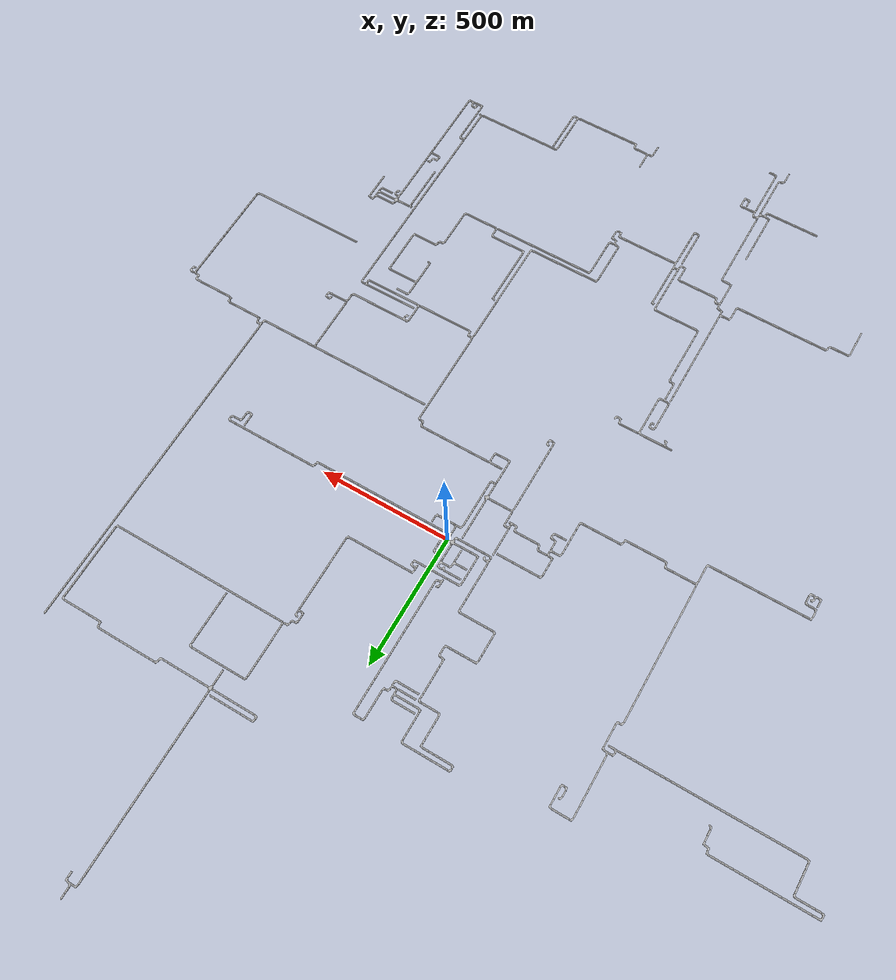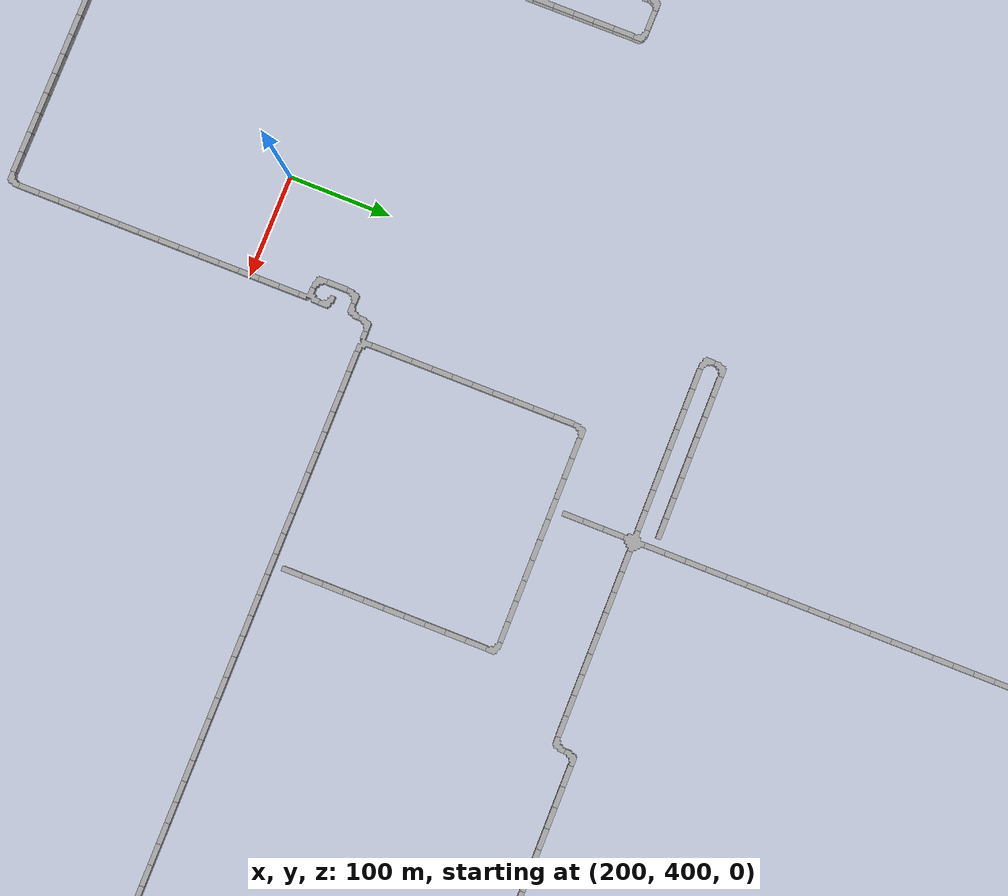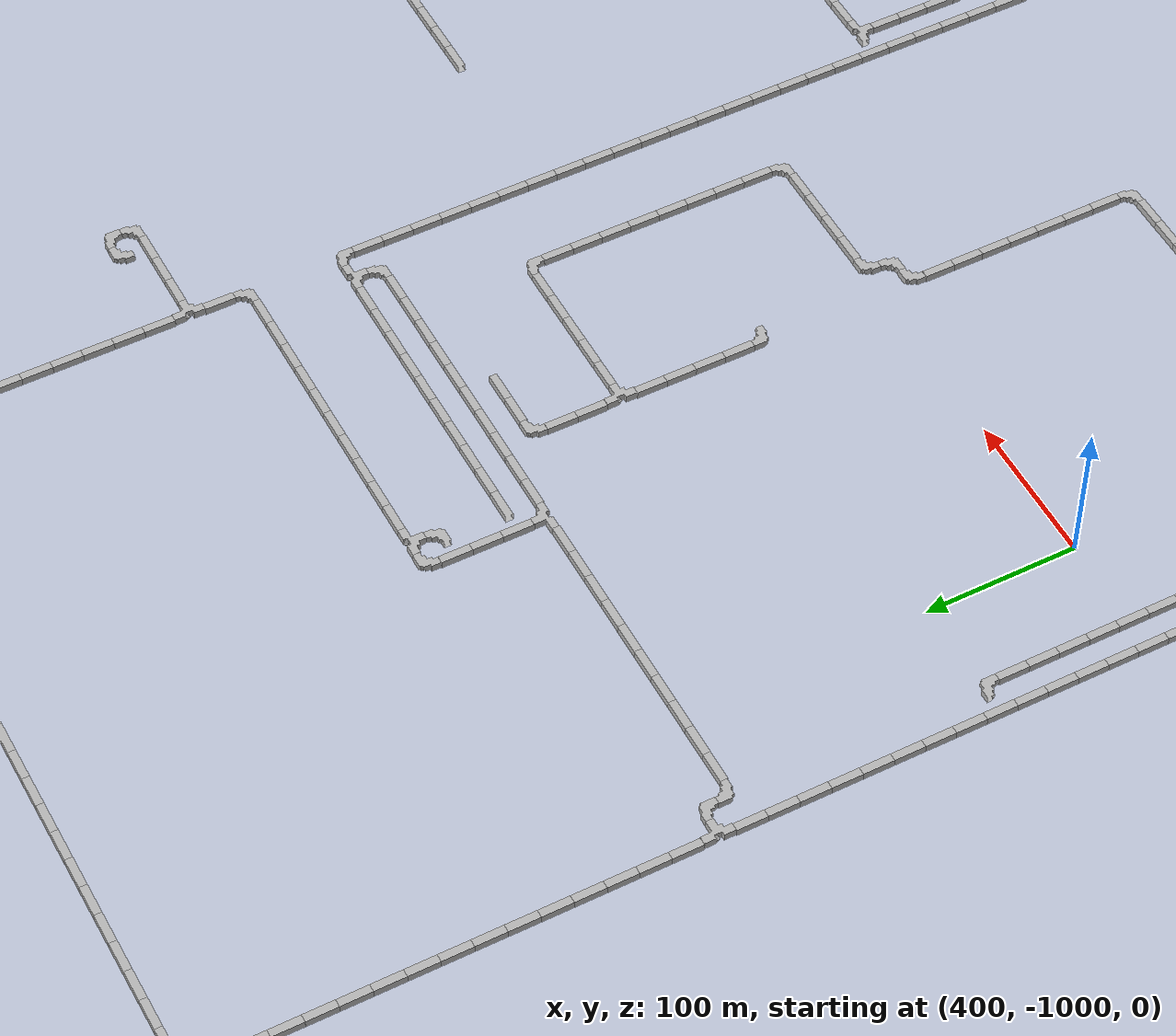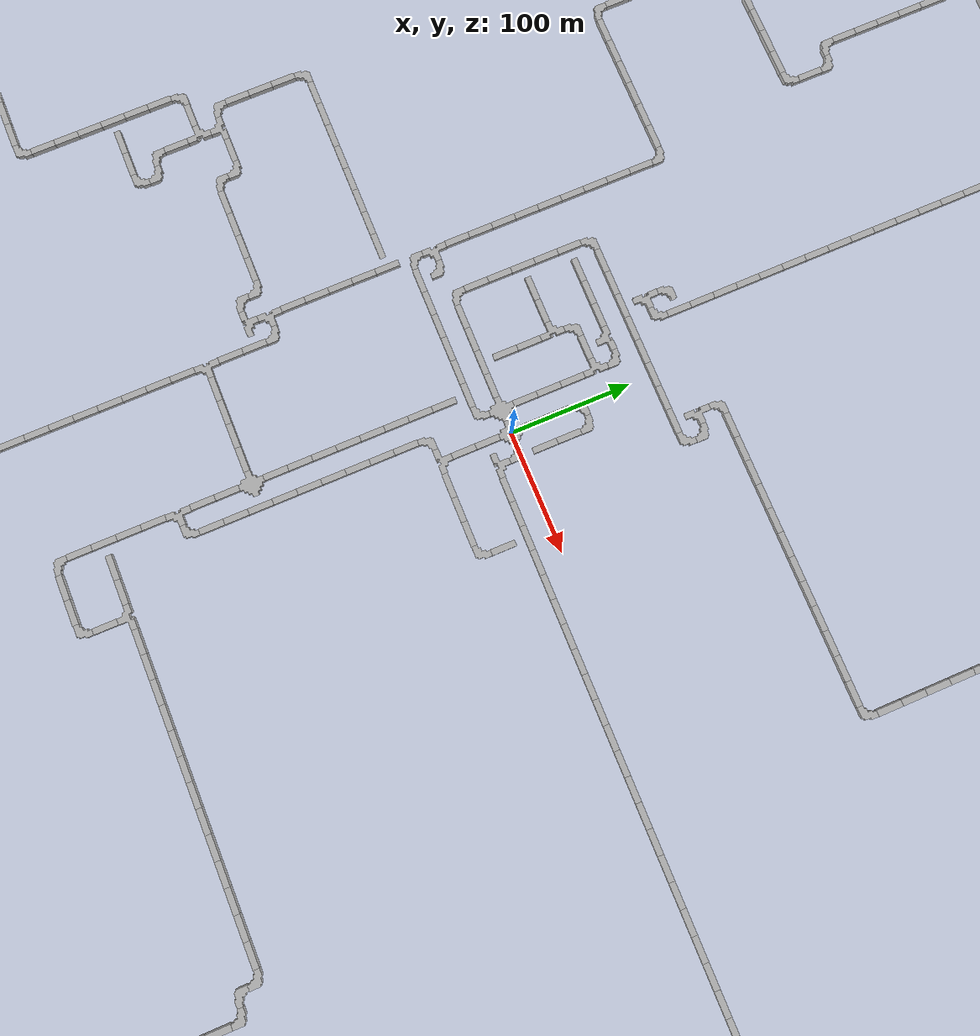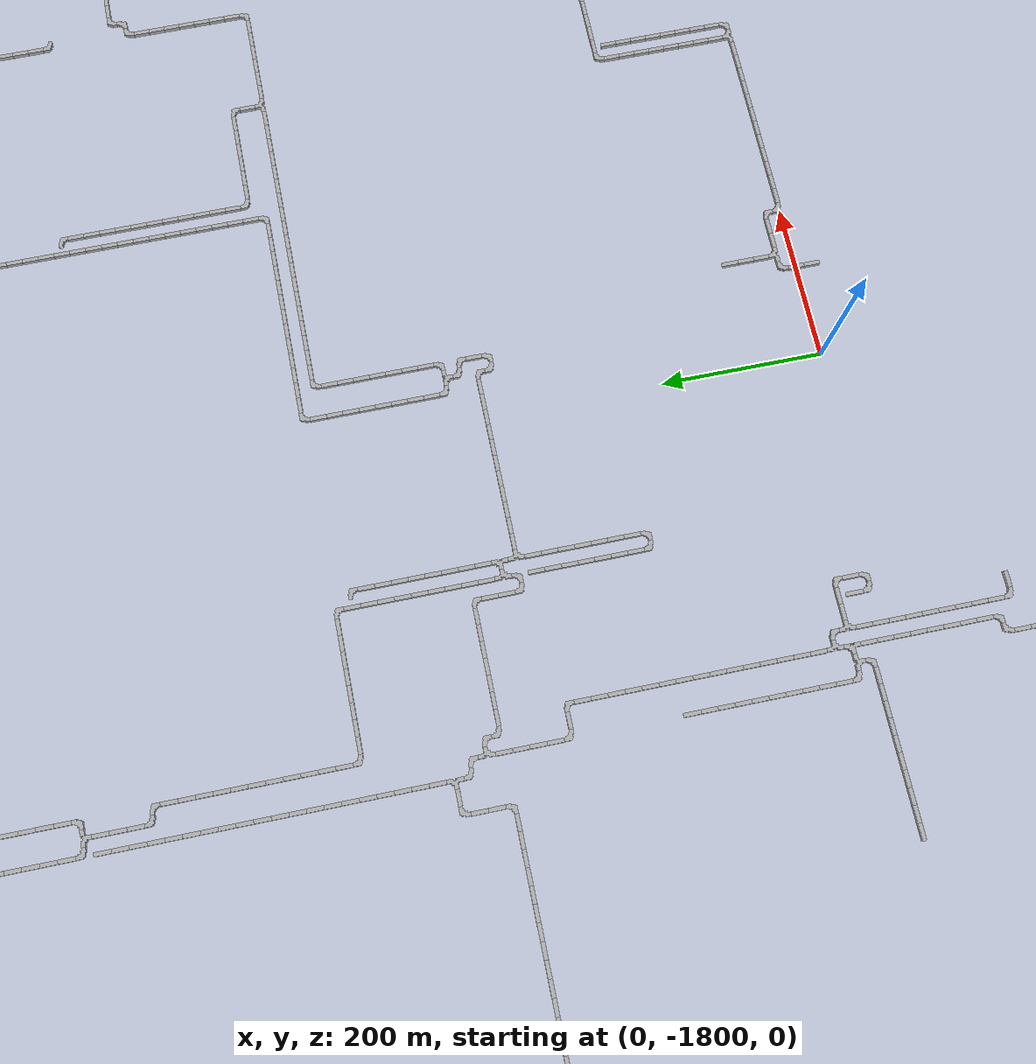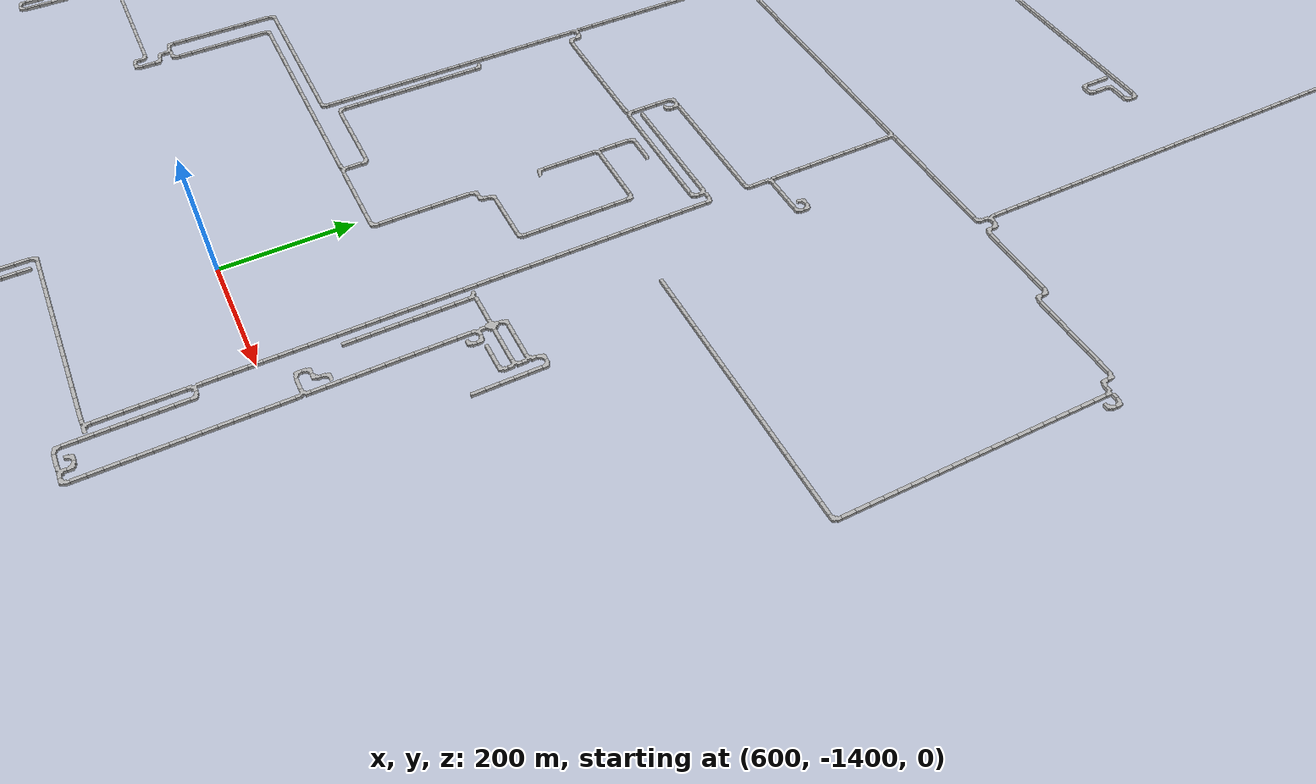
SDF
<sdf version="1.6">
 <world name="cave_32000_4">
  <include>
   <static>true</static>
   <name>cave_0_0</name>
   <pose>0 0 0 0 0 -1.5707963267948966</pose>
   <uri>model://cave_4way_20m</uri>
  </include>
  <include>
   <static>true</static>
   <name>cave_1_0</name>
   <pose>20 0 0 0 0 3.141592653589793</pose>
   <uri>model://cave_L_20m</uri>
  </include>
  <include>
   <static>true</static>
   <name>cave_1_-1</name>
   <pose>20 -20 0 0 0 0.0</pose>
   <uri>model://cave_3way_20m</uri>
  </include>
  <include>
   <static>true</static>
   <name>cave_2_-1</name>
   <pose>40 -20 0 0 0 1.5707963267948966</pose>
   <uri>model://cave_straight_20m</uri>
  </include>
  <include>
   <static>true</static>
   <name>cave_3_-1</name>
   <pose>60 -20 0 0 0 1.5707963267948966</pose>
   <uri>model://cave_straight_20m</uri>
  </include>
  <include>
   <static>true</static>
   <name>cave_4_-1</name>
   <pose>80 -20 0 0 0 1.5707963267948966</pose>
   <uri>model://cave_straight_20m</uri>
  </include>
  <include>
   <static>true</static>
   <name>cave_5_-1</name>
   <pose>100 -20 0 0 0 1.5707963267948966</pose>
   <uri>model://cave_straight_20m</uri>
  </include>
  <include>
   <static>true</static>
   <name>cave_6_-1</name>
   <pose>120 -20 0 0 0 1.5707963267948966</pose>
   <uri>model://cave_straight_20m</uri>
  </include>
  <include>
   <static>true</static>
   <name>cave_7_-1</name>
   <pose>140 -20 0 0 0 1.5707963267948966</pose>
   <uri>model://cave_straight_20m</uri>
  </include>
  <include>
   <static>true</static>
   <name>cave_8_-1</name>
   <pose>160 -20 0 0 0 1.5707963267948966</pose>
   <uri>model://cave_straight_20m</uri>
  </include>
  <include>
   <static>true</static>
   <name>cave_9_-1</name>
   <pose>180 -20 0 0 0 1.5707963267948966</pose>
   <uri>model://cave_straight_20m</uri>
  </include>
  <include>
   <static>true</static>
   <name>cave_10_-1</name>
   <pose>200 -20 0 0 0 1.5707963267948966</pose>
   <uri>model://cave_straight_20m</uri>
  </include>
  <include>
   <static>true</static>
   <name>cave_11_-1</name>
   <pose>220 -20 0 0 0 1.5707963267948966</pose>
   <uri>model://cave_straight_20m</uri>
  </include>
  <include>
   <static>true</static>
   <name>cave_12_-1</name>
   <pose>240 -20 0 0 0 1.5707963267948966</pose>
   <uri>model://cave_straight_20m</uri>
  </include>
  <include>
   <static>true</static>
   <name>cave_13_-1</name>
   <pose>260 -20 0 0 0 1.5707963267948966</pose>
   <uri>model://cave_straight_20m</uri>
  </include>
  <include>
   <static>true</static>
   <name>cave_14_-1</name>
   <pose>280 -20 0 0 0 1.5707963267948966</pose>
   <uri>model://cave_straight_20m</uri>
  </include>
  <include>
   <static>true</static>
   <name>cave_15_-1</name>
   <pose>300 -20 0 0 0 1.5707963267948966</pose>
   <uri>model://cave_straight_20m</uri>
  </include>
  <include>
   <static>true</static>
   <name>cave_16_-1</name>
   <pose>320 -20 0 0 0 1.5707963267948966</pose>
   <uri>model://cave_straight_20m</uri>
  </include>
  <include>
   <static>true</static>
   <name>cave_17_-1</name>
   <pose>340 -20 0 0 0 1.5707963267948966</pose>
   <uri>model://cave_straight_20m</uri>
  </include>
  <include>
   <static>true</static>
   <name>cave_18_-1</name>
   <pose>360 -20 0 0 0 1.5707963267948966</pose>
   <uri>model://cave_straight_20m</uri>
  </include>
  <include>
   <static>true</static>
   <name>cave_19_-1</name>
   <pose>380 -20 0 0 0 1.5707963267948966</pose>
   <uri>model://cave_straight_20m</uri>
  </include>
  <include>
   <static>true</static>
   <name>cave_20_-1</name>
   <pose>400 -20 0 0 0 1.5707963267948966</pose>
   <uri>model://cave_straight_20m</uri>
  </include>
  <include>
   <static>true</static>
   <name>cave_21_-1</name>
   <pose>420 -20 0 0 0 1.5707963267948966</pose>
   <uri>model://cave_straight_20m</uri>
  </include>
  <include>
   <static>true</static>
   <name>cave_22_-1</name>
   <pose>440 -20 0 0 0 1.5707963267948966</pose>
   <uri>model://cave_straight_20m</uri>
  </include>
  <include>
   <static>true</static>
   <name>cave_23_-1</name>
   <pose>460 -20 0 0 0 1.5707963267948966</pose>
   <uri>model://cave_straight_20m</uri>
  </include>
  <include>
   <static>true</static>
   <name>cave_24_-1</name>
   <pose>480 -20 0 0 0 1.5707963267948966</pose>
   <uri>model://cave_straight_20m</uri>
  </include>
  <include>
   <static>true</static>
   <name>cave_25_-1</name>
   <pose>500 -20 0 0 0 1.5707963267948966</pose>
   <uri>model://cave_straight_20m</uri>
  </include>
  <include>
   <static>true</static>
   <name>cave_26_-1</name>
   <pose>520 -20 0 0 0 1.5707963267948966</pose>
   <uri>model://cave_straight_20m</uri>
  </include>
  <include>
   <static>true</static>
   <name>cave_27_-1</name>
   <pose>540 -20 0 0 0 1.5707963267948966</pose>
   <uri>model://cave_L_20m</uri>
  </include>
  <include>
   <static>true</static>
   <name>cave_27_0</name>
   <pose>540 0 0 0 0 -1.5707963267948966</pose>
   <uri>model://cave_L_20m</uri>
  </include>
  <include>
   <static>true</static>
   <name>cave_28_0</name>
   <pose>560 0 0 0 0 1.5707963267948966</pose>
   <uri>model://cave_straight_20m</uri>
  </include>
  <include>
   <static>true</static>
   <name>cave_29_0</name>
   <pose>580 0 0 0 0 1.5707963267948966</pose>
   <uri>model://cave_straight_20m</uri>
  </include>
  <include>
   <static>true</static>
   <name>cave_30_0</name>
   <pose>600 0 0 0 0 1.5707963267948966</pose>
   <uri>model://cave_straight_20m</uri>
  </include>
  <include>
   <static>true</static>
   <name>cave_31_0</name>
   <pose>620 0 0 0 0 1.5707963267948966</pose>
   <uri>model://cave_straight_20m</uri>
  </include>
  <include>
   <static>true</static>
   <name>cave_32_0</name>
   <pose>640 0 0 0 0 1.5707963267948966</pose>
   <uri>model://cave_straight_20m</uri>
  </include>
  <include>
   <static>true</static>
   <name>cave_33_0</name>
   <pose>660 0 0 0 0 1.5707963267948966</pose>
   <uri>model://cave_straight_20m</uri>
  </include>
  <include>
   <static>true</static>
   <name>cave_34_0</name>
   <pose>680 0 0 0 0 1.5707963267948966</pose>
   <uri>model://cave_straight_20m</uri>
  </include>
  <include>
   <static>true</static>
   <name>cave_35_0</name>
   <pose>700 0 0 0 0 1.5707963267948966</pose>
   <uri>model://cave_straight_20m</uri>
  </include>
  <include>
   <static>true</static>
   <name>cave_36_0</name>
   <pose>720 0 0 0 0 1.5707963267948966</pose>
   <uri>model://cave_straight_20m</uri>
  </include>
  <include>
   <static>true</static>
   <name>cave_37_0</name>
   <pose>740 0 0 0 0 1.5707963267948966</pose>
   <uri>model://cave_straight_20m</uri>
  </include>
  <include>
   <static>true</static>
   <name>cave_38_0</name>
   <pose>760 0 0 0 0 1.5707963267948966</pose>
   <uri>model://cave_straight_20m</uri>
  </include>
  <include>
   <static>true</static>
   <name>cave_39_0</name>
   <pose>780 0 0 0 0 1.5707963267948966</pose>
   <uri>model://cave_straight_20m</uri>
  </include>
  <include>
   <static>true</static>
   <name>cave_40_0</name>
   <pose>800 0 0 0 0 1.5707963267948966</pose>
   <uri>model://cave_straight_20m</uri>
  </include>
  <include>
   <static>true</static>
   <name>cave_41_0</name>
   <pose>820 0 0 0 0 1.5707963267948966</pose>
   <uri>model://cave_straight_20m</uri>
  </include>
  <include>
   <static>true</static>
   <name>cave_42_0</name>
   <pose>840 0 0 0 0 1.5707963267948966</pose>
   <uri>model://cave_straight_20m</uri>
  </include>
  <include>
   <static>true</static>
   <name>cave_43_0</name>
   <pose>860 0 0 0 0 1.5707963267948966</pose>
   <uri>model://cave_straight_20m</uri>
  </include>
  <include>
   <static>true</static>
   <name>cave_44_0</name>
   <pose>880 0 0 0 0 1.5707963267948966</pose>
   <uri>model://cave_straight_20m</uri>
  </include>
  <include>
   <static>true</static>
   <name>cave_45_0</name>
   <pose>900 0 0 0 0 3.141592653589793</pose>
   <uri>model://cave_L_20m</uri>
  </include>
  <include>
   <static>true</static>
   <name>cave_45_-1</name>
   <pose>900 -20 0 0 0 1.5707963267948966</pose>
   <uri>model://cave_L_20m</uri>
  </include>
  <include>
   <static>true</static>
   <name>cave_44_-1</name>
   <pose>880 -20 0 0 0 1.5707963267948966</pose>
   <uri>model://cave_straight_20m</uri>
  </include>
  <include>
   <static>true</static>
   <name>cave_43_-1</name>
   <pose>860 -20 0 0 0 -1.5707963267948966</pose>
   <uri>model://cave_L_20m</uri>
  </include>
  <include>
   <static>true</static>
   <name>cave_43_-2</name>
   <pose>860 -40 0 0 0 0.0</pose>
   <uri>model://cave_straight_20m</uri>
  </include>
  <include>
   <static>true</static>
   <name>cave_43_-3</name>
   <pose>860 -60 0 0 0 1.5707963267948966</pose>
   <uri>model://cave_L_20m</uri>
  </include>
  <include>
   <static>true</static>
   <name>cave_42_-3</name>
   <pose>840 -60 0 0 0 0.0</pose>
   <uri>model://cave_L_20m</uri>
  </include>
  <include>
   <static>true</static>
   <name>cave_42_-2</name>
   <pose>840 -40 0 0 0 0.0</pose>
   <uri>model://cave_straight_20m</uri>
  </include>
  <include>
   <static>true</static>
   <name>cave_42_-1</name>
   <pose>840 -20 0 0 0 0.0</pose>
   <uri>model://cave_straight_20m</uri>
  </include>
  <include>
   <static>true</static>
   <name>cave_0_-1</name>
   <pose>0 -20 0 0 0 0.0</pose>
   <uri>model://cave_straight_20m</uri>
  </include>
  <include>
   <static>true</static>
   <name>cave_0_-2</name>
   <pose>0 -40 0 0 0 0.0</pose>
   <uri>model://cave_straight_20m</uri>
  </include>
  <include>
   <static>true</static>
   <name>cave_0_-3</name>
   <pose>0 -60 0 0 0 0.0</pose>
   <uri>model://cave_3way_20m</uri>
  </include>
  <include>
   <static>true</static>
   <name>cave_1_-3</name>
   <pose>20 -60 0 0 0 1.5707963267948966</pose>
   <uri>model://cave_straight_20m</uri>
  </include>
  <include>
   <static>true</static>
   <name>cave_2_-3</name>
   <pose>40 -60 0 0 0 1.5707963267948966</pose>
   <uri>model://cave_straight_20m</uri>
  </include>
  <include>
   <static>true</static>
   <name>cave_3_-3</name>
   <pose>60 -60 0 0 0 1.5707963267948966</pose>
   <uri>model://cave_straight_20m</uri>
  </include>
  <include>
   <static>true</static>
   <name>cave_4_-3</name>
   <pose>80 -60 0 0 0 1.5707963267948966</pose>
   <uri>model://cave_L_20m</uri>
  </include>
  <include>
   <static>true</static>
   <name>cave_4_-2</name>
   <pose>80 -40 0 0 0 0.0</pose>
   <uri>model://cave_straight_20m</uri>
  </include>
  <include>
   <static>true</static>
   <name>cave_-1_-3</name>
   <pose>-20 -60 0 0 0 -1.5707963267948966</pose>
   <uri>model://cave_L_20m</uri>
  </include>
  <include>
   <static>true</static>
   <name>cave_-1_-4</name>
   <pose>-20 -80 0 0 0 0.0</pose>
   <uri>model://cave_straight_20m</uri>
  </include>
  <include>
   <static>true</static>
   <name>cave_-1_-5</name>
   <pose>-20 -100 0 0 0 0.0</pose>
   <uri>model://cave_straight_20m</uri>
  </include>
  <include>
   <static>true</static>
   <name>cave_-1_-6</name>
   <pose>-20 -120 0 0 0 0.0</pose>
   <uri>model://cave_straight_20m</uri>
  </include>
  <include>
   <static>true</static>
   <name>cave_-1_-7</name>
   <pose>-20 -140 0 0 0 0.0</pose>
   <uri>model://cave_straight_20m</uri>
  </include>
  <include>
   <static>true</static>
   <name>cave_-1_-8</name>
   <pose>-20 -160 0 0 0 0.0</pose>
   <uri>model://cave_straight_20m</uri>
  </include>
  <include>
   <static>true</static>
   <name>cave_-1_-9</name>
   <pose>-20 -180 0 0 0 0.0</pose>
   <uri>model://cave_straight_20m</uri>
  </include>
  <include>
   <static>true</static>
   <name>cave_-1_-10</name>
   <pose>-20 -200 0 0 0 0.0</pose>
   <uri>model://cave_straight_20m</uri>
  </include>
  <include>
   <static>true</static>
   <name>cave_-1_-11</name>
   <pose>-20 -220 0 0 0 0.0</pose>
   <uri>model://cave_straight_20m</uri>
  </include>
  <include>
   <static>true</static>
   <name>cave_-1_-12</name>
   <pose>-20 -240 0 0 0 0.0</pose>
   <uri>model://cave_straight_20m</uri>
  </include>
  <include>
   <static>true</static>
   <name>cave_-1_-13</name>
   <pose>-20 -260 0 0 0 1.5707963267948966</pose>
   <uri>model://cave_L_20m</uri>
  </include>
  <include>
   <static>true</static>
   <name>cave_-2_-13</name>
   <pose>-40 -260 0 0 0 -1.5707963267948966</pose>
   <uri>model://cave_3way_20m</uri>
  </include>
  <include>
   <static>true</static>
   <name>cave_-2_-14</name>
   <pose>-40 -280 0 0 0 0.0</pose>
   <uri>model://cave_straight_20m</uri>
  </include>
  <include>
   <static>true</static>
   <name>cave_-2_-15</name>
   <pose>-40 -300 0 0 0 0.0</pose>
   <uri>model://cave_straight_20m</uri>
  </include>
  <include>
   <static>true</static>
   <name>cave_-2_-16</name>
   <pose>-40 -320 0 0 0 0.0</pose>
   <uri>model://cave_straight_20m</uri>
  </include>
  <include>
   <static>true</static>
   <name>cave_-2_-17</name>
   <pose>-40 -340 0 0 0 0.0</pose>
   <uri>model://cave_straight_20m</uri>
  </include>
  <include>
   <static>true</static>
   <name>cave_-2_-18</name>
   <pose>-40 -360 0 0 0 0.0</pose>
   <uri>model://cave_L_20m</uri>
  </include>
  <include>
   <static>true</static>
   <name>cave_-1_-18</name>
   <pose>-20 -360 0 0 0 1.5707963267948966</pose>
   <uri>model://cave_straight_20m</uri>
  </include>
  <include>
   <static>true</static>
   <name>cave_0_-18</name>
   <pose>0 -360 0 0 0 1.5707963267948966</pose>
   <uri>model://cave_straight_20m</uri>
  </include>
  <include>
   <static>true</static>
   <name>cave_1_-18</name>
   <pose>20 -360 0 0 0 1.5707963267948966</pose>
   <uri>model://cave_L_20m</uri>
  </include>
  <include>
   <static>true</static>
   <name>cave_1_-17</name>
   <pose>20 -340 0 0 0 0.0</pose>
   <uri>model://cave_straight_20m</uri>
  </include>
  <include>
   <static>true</static>
   <name>cave_1_-16</name>
   <pose>20 -320 0 0 0 3.141592653589793</pose>
   <uri>model://cave_3way_20m</uri>
  </include>
  <include>
   <static>true</static>
   <name>cave_2_-16</name>
   <pose>40 -320 0 0 0 1.5707963267948966</pose>
   <uri>model://cave_straight_20m</uri>
  </include>
  <include>
   <static>true</static>
   <name>cave_3_-16</name>
   <pose>60 -320 0 0 0 1.5707963267948966</pose>
   <uri>model://cave_straight_20m</uri>
  </include>
  <include>
   <static>true</static>
   <name>cave_4_-16</name>
   <pose>80 -320 0 0 0 1.5707963267948966</pose>
   <uri>model://cave_straight_20m</uri>
  </include>
  <include>
   <static>true</static>
   <name>cave_5_-16</name>
   <pose>100 -320 0 0 0 1.5707963267948966</pose>
   <uri>model://cave_straight_20m</uri>
  </include>
  <include>
   <static>true</static>
   <name>cave_6_-16</name>
   <pose>120 -320 0 0 0 1.5707963267948966</pose>
   <uri>model://cave_straight_20m</uri>
  </include>
  <include>
   <static>true</static>
   <name>cave_7_-16</name>
   <pose>140 -320 0 0 0 1.5707963267948966</pose>
   <uri>model://cave_straight_20m</uri>
  </include>
  <include>
   <static>true</static>
   <name>cave_8_-16</name>
   <pose>160 -320 0 0 0 1.5707963267948966</pose>
   <uri>model://cave_straight_20m</uri>
  </include>
  <include>
   <static>true</static>
   <name>cave_9_-16</name>
   <pose>180 -320 0 0 0 1.5707963267948966</pose>
   <uri>model://cave_straight_20m</uri>
  </include>
  <include>
   <static>true</static>
   <name>cave_10_-16</name>
   <pose>200 -320 0 0 0 1.5707963267948966</pose>
   <uri>model://cave_straight_20m</uri>
  </include>
  <include>
   <static>true</static>
   <name>cave_11_-16</name>
   <pose>220 -320 0 0 0 1.5707963267948966</pose>
   <uri>model://cave_straight_20m</uri>
  </include>
  <include>
   <static>true</static>
   <name>cave_12_-16</name>
   <pose>240 -320 0 0 0 1.5707963267948966</pose>
   <uri>model://cave_straight_20m</uri>
  </include>
  <include>
   <static>true</static>
   <name>cave_13_-16</name>
   <pose>260 -320 0 0 0 1.5707963267948966</pose>
   <uri>model://cave_straight_20m</uri>
  </include>
  <include>
   <static>true</static>
   <name>cave_14_-16</name>
   <pose>280 -320 0 0 0 1.5707963267948966</pose>
   <uri>model://cave_straight_20m</uri>
  </include>
  <include>
   <static>true</static>
   <name>cave_15_-16</name>
   <pose>300 -320 0 0 0 3.141592653589793</pose>
   <uri>model://cave_L_20m</uri>
  </include>
  <include>
   <static>true</static>
   <name>cave_15_-17</name>
   <pose>300 -340 0 0 0 0.0</pose>
   <uri>model://cave_L_20m</uri>
  </include>
  <include>
   <static>true</static>
   <name>cave_16_-17</name>
   <pose>320 -340 0 0 0 3.141592653589793</pose>
   <uri>model://cave_L_20m</uri>
  </include>
  <include>
   <static>true</static>
   <name>cave_16_-18</name>
   <pose>320 -360 0 0 0 0.0</pose>
   <uri>model://cave_straight_20m</uri>
  </include>
  <include>
   <static>true</static>
   <name>cave_16_-19</name>
   <pose>320 -380 0 0 0 0.0</pose>
   <uri>model://cave_straight_20m</uri>
  </include>
  <include>
   <static>true</static>
   <name>cave_16_-20</name>
   <pose>320 -400 0 0 0 0.0</pose>
   <uri>model://cave_straight_20m</uri>
  </include>
  <include>
   <static>true</static>
   <name>cave_16_-21</name>
   <pose>320 -420 0 0 0 0.0</pose>
   <uri>model://cave_straight_20m</uri>
  </include>
  <include>
   <static>true</static>
   <name>cave_16_-22</name>
   <pose>320 -440 0 0 0 0.0</pose>
   <uri>model://cave_straight_20m</uri>
  </include>
  <include>
   <static>true</static>
   <name>cave_16_-23</name>
   <pose>320 -460 0 0 0 0.0</pose>
   <uri>model://cave_straight_20m</uri>
  </include>
  <include>
   <static>true</static>
   <name>cave_16_-24</name>
   <pose>320 -480 0 0 0 0.0</pose>
   <uri>model://cave_straight_20m</uri>
  </include>
  <include>
   <static>true</static>
   <name>cave_16_-25</name>
   <pose>320 -500 0 0 0 0.0</pose>
   <uri>model://cave_straight_20m</uri>
  </include>
  <include>
   <static>true</static>
   <name>cave_16_-26</name>
   <pose>320 -520 0 0 0 0.0</pose>
   <uri>model://cave_straight_20m</uri>
  </include>
  <include>
   <static>true</static>
   <name>cave_16_-27</name>
   <pose>320 -540 0 0 0 0.0</pose>
   <uri>model://cave_straight_20m</uri>
  </include>
  <include>
   <static>true</static>
   <name>cave_16_-28</name>
   <pose>320 -560 0 0 0 0.0</pose>
   <uri>model://cave_straight_20m</uri>
  </include>
  <include>
   <static>true</static>
   <name>cave_16_-29</name>
   <pose>320 -580 0 0 0 0.0</pose>
   <uri>model://cave_straight_20m</uri>
  </include>
  <include>
   <static>true</static>
   <name>cave_16_-30</name>
   <pose>320 -600 0 0 0 0.0</pose>
   <uri>model://cave_straight_20m</uri>
  </include>
  <include>
   <static>true</static>
   <name>cave_16_-31</name>
   <pose>320 -620 0 0 0 0.0</pose>
   <uri>model://cave_straight_20m</uri>
  </include>
  <include>
   <static>true</static>
   <name>cave_16_-32</name>
   <pose>320 -640 0 0 0 0.0</pose>
   <uri>model://cave_straight_20m</uri>
  </include>
  <include>
   <static>true</static>
   <name>cave_16_-33</name>
   <pose>320 -660 0 0 0 0.0</pose>
   <uri>model://cave_straight_20m</uri>
  </include>
  <include>
   <static>true</static>
   <name>cave_16_-34</name>
   <pose>320 -680 0 0 0 0.0</pose>
   <uri>model://cave_straight_20m</uri>
  </include>
  <include>
   <static>true</static>
   <name>cave_16_-35</name>
   <pose>320 -700 0 0 0 0.0</pose>
   <uri>model://cave_straight_20m</uri>
  </include>
  <include>
   <static>true</static>
   <name>cave_16_-36</name>
   <pose>320 -720 0 0 0 -1.5707963267948966</pose>
   <uri>model://cave_3way_20m</uri>
  </include>
  <include>
   <static>true</static>
   <name>cave_17_-36</name>
   <pose>340 -720 0 0 0 3.141592653589793</pose>
   <uri>model://cave_L_20m</uri>
  </include>
  <include>
   <static>true</static>
   <name>cave_17_-37</name>
   <pose>340 -740 0 0 0 0.0</pose>
   <uri>model://cave_L_20m</uri>
  </include>
  <include>
   <static>true</static>
   <name>cave_18_-37</name>
   <pose>360 -740 0 0 0 1.5707963267948966</pose>
   <uri>model://cave_straight_20m</uri>
  </include>
  <include>
   <static>true</static>
   <name>cave_19_-37</name>
   <pose>380 -740 0 0 0 1.5707963267948966</pose>
   <uri>model://cave_straight_20m</uri>
  </include>
  <include>
   <static>true</static>
   <name>cave_20_-37</name>
   <pose>400 -740 0 0 0 1.5707963267948966</pose>
   <uri>model://cave_straight_20m</uri>
  </include>
  <include>
   <static>true</static>
   <name>cave_21_-37</name>
   <pose>420 -740 0 0 0 1.5707963267948966</pose>
   <uri>model://cave_straight_20m</uri>
  </include>
  <include>
   <static>true</static>
   <name>cave_22_-37</name>
   <pose>440 -740 0 0 0 1.5707963267948966</pose>
   <uri>model://cave_straight_20m</uri>
  </include>
  <include>
   <static>true</static>
   <name>cave_23_-37</name>
   <pose>460 -740 0 0 0 1.5707963267948966</pose>
   <uri>model://cave_straight_20m</uri>
  </include>
  <include>
   <static>true</static>
   <name>cave_24_-37</name>
   <pose>480 -740 0 0 0 1.5707963267948966</pose>
   <uri>model://cave_straight_20m</uri>
  </include>
  <include>
   <static>true</static>
   <name>cave_25_-37</name>
   <pose>500 -740 0 0 0 1.5707963267948966</pose>
   <uri>model://cave_straight_20m</uri>
  </include>
  <include>
   <static>true</static>
   <name>cave_26_-37</name>
   <pose>520 -740 0 0 0 1.5707963267948966</pose>
   <uri>model://cave_straight_20m</uri>
  </include>
  <include>
   <static>true</static>
   <name>cave_27_-37</name>
   <pose>540 -740 0 0 0 1.5707963267948966</pose>
   <uri>model://cave_straight_20m</uri>
  </include>
  <include>
   <static>true</static>
   <name>cave_28_-37</name>
   <pose>560 -740 0 0 0 0.0</pose>
   <uri>model://cave_3way_20m</uri>
  </include>
  <include>
   <static>true</static>
   <name>cave_29_-37</name>
   <pose>580 -740 0 0 0 1.5707963267948966</pose>
   <uri>model://cave_straight_20m</uri>
  </include>
  <include>
   <static>true</static>
   <name>cave_30_-37</name>
   <pose>600 -740 0 0 0 1.5707963267948966</pose>
   <uri>model://cave_straight_20m</uri>
  </include>
  <include>
   <static>true</static>
   <name>cave_31_-37</name>
   <pose>620 -740 0 0 0 1.5707963267948966</pose>
   <uri>model://cave_straight_20m</uri>
  </include>
  <include>
   <static>true</static>
   <name>cave_32_-37</name>
   <pose>640 -740 0 0 0 1.5707963267948966</pose>
   <uri>model://cave_straight_20m</uri>
  </include>
  <include>
   <static>true</static>
   <name>cave_33_-37</name>
   <pose>660 -740 0 0 0 1.5707963267948966</pose>
   <uri>model://cave_straight_20m</uri>
  </include>
  <include>
   <static>true</static>
   <name>cave_34_-37</name>
   <pose>680 -740 0 0 0 1.5707963267948966</pose>
   <uri>model://cave_straight_20m</uri>
  </include>
  <include>
   <static>true</static>
   <name>cave_35_-37</name>
   <pose>700 -740 0 0 0 1.5707963267948966</pose>
   <uri>model://cave_straight_20m</uri>
  </include>
  <include>
   <static>true</static>
   <name>cave_36_-37</name>
   <pose>720 -740 0 0 0 1.5707963267948966</pose>
   <uri>model://cave_straight_20m</uri>
  </include>
  <include>
   <static>true</static>
   <name>cave_37_-37</name>
   <pose>740 -740 0 0 0 1.5707963267948966</pose>
   <uri>model://cave_straight_20m</uri>
  </include>
  <include>
   <static>true</static>
   <name>cave_38_-37</name>
   <pose>760 -740 0 0 0 1.5707963267948966</pose>
   <uri>model://cave_straight_20m</uri>
  </include>
  <include>
   <static>true</static>
   <name>cave_39_-37</name>
   <pose>780 -740 0 0 0 1.5707963267948966</pose>
   <uri>model://cave_L_20m</uri>
  </include>
  <include>
   <static>true</static>
   <name>cave_39_-36</name>
   <pose>780 -720 0 0 0 3.141592653589793</pose>
   <uri>model://cave_3way_20m</uri>
  </include>
  <include>
   <static>true</static>
   <name>cave_40_-36</name>
   <pose>800 -720 0 0 0 3.141592653589793</pose>
   <uri>model://cave_L_20m</uri>
  </include>
  <include>
   <static>true</static>
   <name>cave_40_-37</name>
   <pose>800 -740 0 0 0 0.0</pose>
   <uri>model://cave_straight_20m</uri>
  </include>
  <include>
   <static>true</static>
   <name>cave_40_-38</name>
   <pose>800 -760 0 0 0 0.0</pose>
   <uri>model://cave_straight_20m</uri>
  </include>
  <include>
   <static>true</static>
   <name>cave_40_-39</name>
   <pose>800 -780 0 0 0 0.0</pose>
   <uri>model://cave_straight_20m</uri>
  </include>
  <include>
   <static>true</static>
   <name>cave_40_-40</name>
   <pose>800 -800 0 0 0 0.0</pose>
   <uri>model://cave_straight_20m</uri>
  </include>
  <include>
   <static>true</static>
   <name>cave_40_-41</name>
   <pose>800 -820 0 0 0 0.0</pose>
   <uri>model://cave_straight_20m</uri>
  </include>
  <include>
   <static>true</static>
   <name>cave_40_-42</name>
   <pose>800 -840 0 0 0 0.0</pose>
   <uri>model://cave_straight_20m</uri>
  </include>
  <include>
   <static>true</static>
   <name>cave_40_-43</name>
   <pose>800 -860 0 0 0 0.0</pose>
   <uri>model://cave_straight_20m</uri>
  </include>
  <include>
   <static>true</static>
   <name>cave_40_-44</name>
   <pose>800 -880 0 0 0 0.0</pose>
   <uri>model://cave_straight_20m</uri>
  </include>
  <include>
   <static>true</static>
   <name>cave_40_-45</name>
   <pose>800 -900 0 0 0 0.0</pose>
   <uri>model://cave_straight_20m</uri>
  </include>
  <include>
   <static>true</static>
   <name>cave_40_-46</name>
   <pose>800 -920 0 0 0 0.0</pose>
   <uri>model://cave_straight_20m</uri>
  </include>
  <include>
   <static>true</static>
   <name>cave_40_-47</name>
   <pose>800 -940 0 0 0 0.0</pose>
   <uri>model://cave_straight_20m</uri>
  </include>
  <include>
   <static>true</static>
   <name>cave_40_-48</name>
   <pose>800 -960 0 0 0 0.0</pose>
   <uri>model://cave_straight_20m</uri>
  </include>
  <include>
   <static>true</static>
   <name>cave_40_-49</name>
   <pose>800 -980 0 0 0 0.0</pose>
   <uri>model://cave_straight_20m</uri>
  </include>
  <include>
   <static>true</static>
   <name>cave_40_-50</name>
   <pose>800 -1000 0 0 0 0.0</pose>
   <uri>model://cave_straight_20m</uri>
  </include>
  <include>
   <static>true</static>
   <name>cave_40_-51</name>
   <pose>800 -1020 0 0 0 0.0</pose>
   <uri>model://cave_straight_20m</uri>
  </include>
  <include>
   <static>true</static>
   <name>cave_40_-52</name>
   <pose>800 -1040 0 0 0 0.0</pose>
   <uri>model://cave_straight_20m</uri>
  </include>
  <include>
   <static>true</static>
   <name>cave_40_-53</name>
   <pose>800 -1060 0 0 0 0.0</pose>
   <uri>model://cave_straight_20m</uri>
  </include>
  <include>
   <static>true</static>
   <name>cave_40_-54</name>
   <pose>800 -1080 0 0 0 0.0</pose>
   <uri>model://cave_straight_20m</uri>
  </include>
  <include>
   <static>true</static>
   <name>cave_40_-55</name>
   <pose>800 -1100 0 0 0 0.0</pose>
   <uri>model://cave_straight_20m</uri>
  </include>
  <include>
   <static>true</static>
   <name>cave_40_-56</name>
   <pose>800 -1120 0 0 0 0.0</pose>
   <uri>model://cave_straight_20m</uri>
  </include>
  <include>
   <static>true</static>
   <name>cave_40_-57</name>
   <pose>800 -1140 0 0 0 0.0</pose>
   <uri>model://cave_straight_20m</uri>
  </include>
  <include>
   <static>true</static>
   <name>cave_40_-58</name>
   <pose>800 -1160 0 0 0 0.0</pose>
   <uri>model://cave_straight_20m</uri>
  </include>
  <include>
   <static>true</static>
   <name>cave_40_-59</name>
   <pose>800 -1180 0 0 0 0.0</pose>
   <uri>model://cave_straight_20m</uri>
  </include>
  <include>
   <static>true</static>
   <name>cave_40_-60</name>
   <pose>800 -1200 0 0 0 0.0</pose>
   <uri>model://cave_straight_20m</uri>
  </include>
  <include>
   <static>true</static>
   <name>cave_40_-61</name>
   <pose>800 -1220 0 0 0 0.0</pose>
   <uri>model://cave_straight_20m</uri>
  </include>
  <include>
   <static>true</static>
   <name>cave_40_-62</name>
   <pose>800 -1240 0 0 0 0.0</pose>
   <uri>model://cave_straight_20m</uri>
  </include>
  <include>
   <static>true</static>
   <name>cave_40_-63</name>
   <pose>800 -1260 0 0 0 0.0</pose>
   <uri>model://cave_straight_20m</uri>
  </include>
  <include>
   <static>true</static>
   <name>cave_40_-64</name>
   <pose>800 -1280 0 0 0 0.0</pose>
   <uri>model://cave_straight_20m</uri>
  </include>
  <include>
   <static>true</static>
   <name>cave_40_-65</name>
   <pose>800 -1300 0 0 0 0.0</pose>
   <uri>model://cave_straight_20m</uri>
  </include>
  <include>
   <static>true</static>
   <name>cave_40_-66</name>
   <pose>800 -1320 0 0 0 0.0</pose>
   <uri>model://cave_straight_20m</uri>
  </include>
  <include>
   <static>true</static>
   <name>cave_40_-67</name>
   <pose>800 -1340 0 0 0 0.0</pose>
   <uri>model://cave_straight_20m</uri>
  </include>
  <include>
   <static>true</static>
   <name>cave_40_-68</name>
   <pose>800 -1360 0 0 0 0.0</pose>
   <uri>model://cave_straight_20m</uri>
  </include>
  <include>
   <static>true</static>
   <name>cave_40_-69</name>
   <pose>800 -1380 0 0 0 0.0</pose>
   <uri>model://cave_straight_20m</uri>
  </include>
  <include>
   <static>true</static>
   <name>cave_40_-70</name>
   <pose>800 -1400 0 0 0 0.0</pose>
   <uri>model://cave_straight_20m</uri>
  </include>
  <include>
   <static>true</static>
   <name>cave_40_-71</name>
   <pose>800 -1420 0 0 0 0.0</pose>
   <uri>model://cave_straight_20m</uri>
  </include>
  <include>
   <static>true</static>
   <name>cave_40_-72</name>
   <pose>800 -1440 0 0 0 0.0</pose>
   <uri>model://cave_straight_20m</uri>
  </include>
  <include>
   <static>true</static>
   <name>cave_40_-73</name>
   <pose>800 -1460 0 0 0 0.0</pose>
   <uri>model://cave_straight_20m</uri>
  </include>
  <include>
   <static>true</static>
   <name>cave_40_-74</name>
   <pose>800 -1480 0 0 0 -1.5707963267948966</pose>
   <uri>model://cave_3way_20m</uri>
  </include>
  <include>
   <static>true</static>
   <name>cave_41_-74</name>
   <pose>820 -1480 0 0 0 3.141592653589793</pose>
   <uri>model://cave_L_20m</uri>
  </include>
  <include>
   <static>true</static>
   <name>cave_41_-75</name>
   <pose>820 -1500 0 0 0 0.0</pose>
   <uri>model://cave_straight_20m</uri>
  </include>
  <include>
   <static>true</static>
   <name>cave_41_-76</name>
   <pose>820 -1520 0 0 0 0.0</pose>
   <uri>model://cave_straight_20m</uri>
  </include>
  <include>
   <static>true</static>
   <name>cave_41_-77</name>
   <pose>820 -1540 0 0 0 0.0</pose>
   <uri>model://cave_straight_20m</uri>
  </include>
  <include>
   <static>true</static>
   <name>cave_41_-78</name>
   <pose>820 -1560 0 0 0 0.0</pose>
   <uri>model://cave_straight_20m</uri>
  </include>
  <include>
   <static>true</static>
   <name>cave_41_-79</name>
   <pose>820 -1580 0 0 0 0.0</pose>
   <uri>model://cave_straight_20m</uri>
  </include>
  <include>
   <static>true</static>
   <name>cave_41_-80</name>
   <pose>820 -1600 0 0 0 0.0</pose>
   <uri>model://cave_straight_20m</uri>
  </include>
  <include>
   <static>true</static>
   <name>cave_41_-81</name>
   <pose>820 -1620 0 0 0 0.0</pose>
   <uri>model://cave_straight_20m</uri>
  </include>
  <include>
   <static>true</static>
   <name>cave_41_-82</name>
   <pose>820 -1640 0 0 0 0.0</pose>
   <uri>model://cave_straight_20m</uri>
  </include>
  <include>
   <static>true</static>
   <name>cave_41_-83</name>
   <pose>820 -1660 0 0 0 0.0</pose>
   <uri>model://cave_L_20m</uri>
  </include>
  <include>
   <static>true</static>
   <name>cave_42_-83</name>
   <pose>840 -1660 0 0 0 1.5707963267948966</pose>
   <uri>model://cave_straight_20m</uri>
  </include>
  <include>
   <static>true</static>
   <name>cave_43_-83</name>
   <pose>860 -1660 0 0 0 0.0</pose>
   <uri>model://cave_3way_20m</uri>
  </include>
  <include>
   <static>true</static>
   <name>cave_44_-83</name>
   <pose>880 -1660 0 0 0 1.5707963267948966</pose>
   <uri>model://cave_L_20m</uri>
  </include>
  <include>
   <static>true</static>
   <name>cave_44_-82</name>
   <pose>880 -1640 0 0 0 0.0</pose>
   <uri>model://cave_straight_20m</uri>
  </include>
  <include>
   <static>true</static>
   <name>cave_44_-81</name>
   <pose>880 -1620 0 0 0 0.0</pose>
   <uri>model://cave_straight_20m</uri>
  </include>
  <include>
   <static>true</static>
   <name>cave_44_-80</name>
   <pose>880 -1600 0 0 0 0.0</pose>
   <uri>model://cave_straight_20m</uri>
  </include>
  <include>
   <static>true</static>
   <name>cave_44_-79</name>
   <pose>880 -1580 0 0 0 0.0</pose>
   <uri>model://cave_straight_20m</uri>
  </include>
  <include>
   <static>true</static>
   <name>cave_44_-78</name>
   <pose>880 -1560 0 0 0 0.0</pose>
   <uri>model://cave_straight_20m</uri>
  </include>
  <include>
   <static>true</static>
   <name>cave_44_-77</name>
   <pose>880 -1540 0 0 0 0.0</pose>
   <uri>model://cave_straight_20m</uri>
  </include>
  <include>
   <static>true</static>
   <name>cave_44_-76</name>
   <pose>880 -1520 0 0 0 0.0</pose>
   <uri>model://cave_straight_20m</uri>
  </include>
  <include>
   <static>true</static>
   <name>cave_44_-75</name>
   <pose>880 -1500 0 0 0 0.0</pose>
   <uri>model://cave_straight_20m</uri>
  </include>
  <include>
   <static>true</static>
   <name>cave_44_-74</name>
   <pose>880 -1480 0 0 0 0.0</pose>
   <uri>model://cave_straight_20m</uri>
  </include>
  <include>
   <static>true</static>
   <name>cave_44_-73</name>
   <pose>880 -1460 0 0 0 0.0</pose>
   <uri>model://cave_straight_20m</uri>
  </include>
  <include>
   <static>true</static>
   <name>cave_44_-72</name>
   <pose>880 -1440 0 0 0 0.0</pose>
   <uri>model://cave_straight_20m</uri>
  </include>
  <include>
   <static>true</static>
   <name>cave_44_-71</name>
   <pose>880 -1420 0 0 0 0.0</pose>
   <uri>model://cave_straight_20m</uri>
  </include>
  <include>
   <static>true</static>
   <name>cave_44_-70</name>
   <pose>880 -1400 0 0 0 0.0</pose>
   <uri>model://cave_straight_20m</uri>
  </include>
  <include>
   <static>true</static>
   <name>cave_44_-69</name>
   <pose>880 -1380 0 0 0 0.0</pose>
   <uri>model://cave_straight_20m</uri>
  </include>
  <include>
   <static>true</static>
   <name>cave_44_-68</name>
   <pose>880 -1360 0 0 0 1.5707963267948966</pose>
   <uri>model://cave_3way_20m</uri>
  </include>
  <include>
   <static>true</static>
   <name>cave_43_-68</name>
   <pose>860 -1360 0 0 0 1.5707963267948966</pose>
   <uri>model://cave_straight_20m</uri>
  </include>
  <include>
   <static>true</static>
   <name>cave_42_-68</name>
   <pose>840 -1360 0 0 0 0.0</pose>
   <uri>model://cave_L_20m</uri>
  </include>
  <include>
   <static>true</static>
   <name>cave_42_-67</name>
   <pose>840 -1340 0 0 0 -1.5707963267948966</pose>
   <uri>model://cave_L_20m</uri>
  </include>
  <include>
   <static>true</static>
   <name>cave_43_-67</name>
   <pose>860 -1340 0 0 0 1.5707963267948966</pose>
   <uri>model://cave_L_20m</uri>
  </include>
  <include>
   <static>true</static>
   <name>cave_43_-66</name>
   <pose>860 -1320 0 0 0 -1.5707963267948966</pose>
   <uri>model://cave_L_20m</uri>
  </include>
  <include>
   <static>true</static>
   <name>cave_44_-67</name>
   <pose>880 -1340 0 0 0 0.0</pose>
   <uri>model://cave_straight_20m</uri>
  </include>
  <include>
   <static>true</static>
   <name>cave_44_-66</name>
   <pose>880 -1320 0 0 0 0.0</pose>
   <uri>model://cave_straight_20m</uri>
  </include>
  <include>
   <static>true</static>
   <name>cave_44_-65</name>
   <pose>880 -1300 0 0 0 0.0</pose>
   <uri>model://cave_straight_20m</uri>
  </include>
  <include>
   <static>true</static>
   <name>cave_44_-64</name>
   <pose>880 -1280 0 0 0 0.0</pose>
   <uri>model://cave_straight_20m</uri>
  </include>
  <include>
   <static>true</static>
   <name>cave_44_-63</name>
   <pose>880 -1260 0 0 0 0.0</pose>
   <uri>model://cave_straight_20m</uri>
  </include>
  <include>
   <static>true</static>
   <name>cave_44_-62</name>
   <pose>880 -1240 0 0 0 0.0</pose>
   <uri>model://cave_straight_20m</uri>
  </include>
  <include>
   <static>true</static>
   <name>cave_44_-61</name>
   <pose>880 -1220 0 0 0 0.0</pose>
   <uri>model://cave_straight_20m</uri>
  </include>
  <include>
   <static>true</static>
   <name>cave_44_-60</name>
   <pose>880 -1200 0 0 0 0.0</pose>
   <uri>model://cave_straight_20m</uri>
  </include>
  <include>
   <static>true</static>
   <name>cave_44_-59</name>
   <pose>880 -1180 0 0 0 0.0</pose>
   <uri>model://cave_straight_20m</uri>
  </include>
  <include>
   <static>true</static>
   <name>cave_44_-58</name>
   <pose>880 -1160 0 0 0 0.0</pose>
   <uri>model://cave_straight_20m</uri>
  </include>
  <include>
   <static>true</static>
   <name>cave_44_-57</name>
   <pose>880 -1140 0 0 0 0.0</pose>
   <uri>model://cave_straight_20m</uri>
  </include>
  <include>
   <static>true</static>
   <name>cave_44_-56</name>
   <pose>880 -1120 0 0 0 -1.5707963267948966</pose>
   <uri>model://cave_3way_20m</uri>
  </include>
  <include>
   <static>true</static>
   <name>cave_45_-56</name>
   <pose>900 -1120 0 0 0 3.141592653589793</pose>
   <uri>model://cave_L_20m</uri>
  </include>
  <include>
   <static>true</static>
   <name>cave_45_-57</name>
   <pose>900 -1140 0 0 0 1.5707963267948966</pose>
   <uri>model://cave_L_20m</uri>
  </include>
  <include>
   <static>true</static>
   <name>cave_44_-55</name>
   <pose>880 -1100 0 0 0 -1.5707963267948966</pose>
   <uri>model://cave_4way_20m</uri>
  </include>
  <include>
   <static>true</static>
   <name>cave_45_-55</name>
   <pose>900 -1100 0 0 0 1.5707963267948966</pose>
   <uri>model://cave_straight_20m</uri>
  </include>
  <include>
   <static>true</static>
   <name>cave_46_-55</name>
   <pose>920 -1100 0 0 0 1.5707963267948966</pose>
   <uri>model://cave_straight_20m</uri>
  </include>
  <include>
   <static>true</static>
   <name>cave_47_-55</name>
   <pose>940 -1100 0 0 0 1.5707963267948966</pose>
   <uri>model://cave_straight_20m</uri>
  </include>
  <include>
   <static>true</static>
   <name>cave_48_-55</name>
   <pose>960 -1100 0 0 0 1.5707963267948966</pose>
   <uri>model://cave_3way_20m</uri>
  </include>
  <include>
   <static>true</static>
   <name>cave_48_-56</name>
   <pose>960 -1120 0 0 0 1.5707963267948966</pose>
   <uri>model://cave_L_20m</uri>
  </include>
  <include>
   <static>true</static>
   <name>cave_47_-56</name>
   <pose>940 -1120 0 0 0 1.5707963267948966</pose>
   <uri>model://cave_straight_20m</uri>
  </include>
  <include>
   <static>true</static>
   <name>cave_46_-56</name>
   <pose>920 -1120 0 0 0 1.5707963267948966</pose>
   <uri>model://cave_straight_20m</uri>
  </include>
  <include>
   <static>true</static>
   <name>cave_48_-54</name>
   <pose>960 -1080 0 0 0 1.5707963267948966</pose>
   <uri>model://cave_3way_20m</uri>
  </include>
  <include>
   <static>true</static>
   <name>cave_48_-53</name>
   <pose>960 -1060 0 0 0 -1.5707963267948966</pose>
   <uri>model://cave_L_20m</uri>
  </include>
  <include>
   <static>true</static>
   <name>cave_49_-53</name>
   <pose>980 -1060 0 0 0 3.141592653589793</pose>
   <uri>model://cave_L_20m</uri>
  </include>
  <include>
   <static>true</static>
   <name>cave_49_-54</name>
   <pose>980 -1080 0 0 0 0.0</pose>
   <uri>model://cave_straight_20m</uri>
  </include>
  <include>
   <static>true</static>
   <name>cave_49_-55</name>
   <pose>980 -1100 0 0 0 0.0</pose>
   <uri>model://cave_straight_20m</uri>
  </include>
  <include>
   <static>true</static>
   <name>cave_49_-56</name>
   <pose>980 -1120 0 0 0 0.0</pose>
   <uri>model://cave_straight_20m</uri>
  </include>
  <include>
   <static>true</static>
   <name>cave_49_-57</name>
   <pose>980 -1140 0 0 0 0.0</pose>
   <uri>model://cave_straight_20m</uri>
  </include>
  <include>
   <static>true</static>
   <name>cave_49_-58</name>
   <pose>980 -1160 0 0 0 0.0</pose>
   <uri>model://cave_straight_20m</uri>
  </include>
  <include>
   <static>true</static>
   <name>cave_43_-55</name>
   <pose>860 -1100 0 0 0 1.5707963267948966</pose>
   <uri>model://cave_straight_20m</uri>
  </include>
  <include>
   <static>true</static>
   <name>cave_42_-55</name>
   <pose>840 -1100 0 0 0 1.5707963267948966</pose>
   <uri>model://cave_straight_20m</uri>
  </include>
  <include>
   <static>true</static>
   <name>cave_41_-55</name>
   <pose>820 -1100 0 0 0 3.141592653589793</pose>
   <uri>model://cave_3way_20m</uri>
  </include>
  <include>
   <static>true</static>
   <name>cave_41_-56</name>
   <pose>820 -1120 0 0 0 0.0</pose>
   <uri>model://cave_straight_20m</uri>
  </include>
  <include>
   <static>true</static>
   <name>cave_41_-57</name>
   <pose>820 -1140 0 0 0 0.0</pose>
   <uri>model://cave_straight_20m</uri>
  </include>
  <include>
   <static>true</static>
   <name>cave_41_-58</name>
   <pose>820 -1160 0 0 0 0.0</pose>
   <uri>model://cave_straight_20m</uri>
  </include>
  <include>
   <static>true</static>
   <name>cave_41_-59</name>
   <pose>820 -1180 0 0 0 0.0</pose>
   <uri>model://cave_straight_20m</uri>
  </include>
  <include>
   <static>true</static>
   <name>cave_41_-60</name>
   <pose>820 -1200 0 0 0 0.0</pose>
   <uri>model://cave_straight_20m</uri>
  </include>
  <include>
   <static>true</static>
   <name>cave_41_-61</name>
   <pose>820 -1220 0 0 0 0.0</pose>
   <uri>model://cave_straight_20m</uri>
  </include>
  <include>
   <static>true</static>
   <name>cave_41_-62</name>
   <pose>820 -1240 0 0 0 0.0</pose>
   <uri>model://cave_straight_20m</uri>
  </include>
  <include>
   <static>true</static>
   <name>cave_41_-63</name>
   <pose>820 -1260 0 0 0 0.0</pose>
   <uri>model://cave_straight_20m</uri>
  </include>
  <include>
   <static>true</static>
   <name>cave_41_-64</name>
   <pose>820 -1280 0 0 0 0.0</pose>
   <uri>model://cave_straight_20m</uri>
  </include>
  <include>
   <static>true</static>
   <name>cave_44_-54</name>
   <pose>880 -1080 0 0 0 -1.5707963267948966</pose>
   <uri>model://cave_L_20m</uri>
  </include>
  <include>
   <static>true</static>
   <name>cave_45_-54</name>
   <pose>900 -1080 0 0 0 1.5707963267948966</pose>
   <uri>model://cave_straight_20m</uri>
  </include>
  <include>
   <static>true</static>
   <name>cave_46_-54</name>
   <pose>920 -1080 0 0 0 1.5707963267948966</pose>
   <uri>model://cave_straight_20m</uri>
  </include>
  <include>
   <static>true</static>
   <name>cave_47_-54</name>
   <pose>940 -1080 0 0 0 1.5707963267948966</pose>
   <uri>model://cave_straight_20m</uri>
  </include>
  <include>
   <static>true</static>
   <name>cave_43_-82</name>
   <pose>860 -1640 0 0 0 3.141592653589793</pose>
   <uri>model://cave_L_20m</uri>
  </include>
  <include>
   <static>true</static>
   <name>cave_42_-82</name>
   <pose>840 -1640 0 0 0 -1.5707963267948966</pose>
   <uri>model://cave_L_20m</uri>
  </include>
  <include>
   <static>true</static>
   <name>cave_40_-75</name>
   <pose>800 -1500 0 0 0 0.0</pose>
   <uri>model://cave_straight_20m</uri>
  </include>
  <include>
   <static>true</static>
   <name>cave_40_-76</name>
   <pose>800 -1520 0 0 0 0.0</pose>
   <uri>model://cave_straight_20m</uri>
  </include>
  <include>
   <static>true</static>
   <name>cave_40_-77</name>
   <pose>800 -1540 0 0 0 0.0</pose>
   <uri>model://cave_straight_20m</uri>
  </include>
  <include>
   <static>true</static>
   <name>cave_40_-78</name>
   <pose>800 -1560 0 0 0 0.0</pose>
   <uri>model://cave_straight_20m</uri>
  </include>
  <include>
   <static>true</static>
   <name>cave_40_-79</name>
   <pose>800 -1580 0 0 0 0.0</pose>
   <uri>model://cave_straight_20m</uri>
  </include>
  <include>
   <static>true</static>
   <name>cave_40_-80</name>
   <pose>800 -1600 0 0 0 0.0</pose>
   <uri>model://cave_straight_20m</uri>
  </include>
  <include>
   <static>true</static>
   <name>cave_40_-81</name>
   <pose>800 -1620 0 0 0 0.0</pose>
   <uri>model://cave_3way_20m</uri>
  </include>
  <include>
   <static>true</static>
   <name>cave_39_-81</name>
   <pose>780 -1620 0 0 0 1.5707963267948966</pose>
   <uri>model://cave_straight_20m</uri>
  </include>
  <include>
   <static>true</static>
   <name>cave_38_-81</name>
   <pose>760 -1620 0 0 0 1.5707963267948966</pose>
   <uri>model://cave_straight_20m</uri>
  </include>
  <include>
   <static>true</static>
   <name>cave_37_-81</name>
   <pose>740 -1620 0 0 0 1.5707963267948966</pose>
   <uri>model://cave_straight_20m</uri>
  </include>
  <include>
   <static>true</static>
   <name>cave_36_-81</name>
   <pose>720 -1620 0 0 0 1.5707963267948966</pose>
   <uri>model://cave_straight_20m</uri>
  </include>
  <include>
   <static>true</static>
   <name>cave_35_-81</name>
   <pose>700 -1620 0 0 0 1.5707963267948966</pose>
   <uri>model://cave_straight_20m</uri>
  </include>
  <include>
   <static>true</static>
   <name>cave_34_-81</name>
   <pose>680 -1620 0 0 0 1.5707963267948966</pose>
   <uri>model://cave_straight_20m</uri>
  </include>
  <include>
   <static>true</static>
   <name>cave_33_-81</name>
   <pose>660 -1620 0 0 0 1.5707963267948966</pose>
   <uri>model://cave_straight_20m</uri>
  </include>
  <include>
   <static>true</static>
   <name>cave_32_-81</name>
   <pose>640 -1620 0 0 0 1.5707963267948966</pose>
   <uri>model://cave_straight_20m</uri>
  </include>
  <include>
   <static>true</static>
   <name>cave_31_-81</name>
   <pose>620 -1620 0 0 0 1.5707963267948966</pose>
   <uri>model://cave_straight_20m</uri>
  </include>
  <include>
   <static>true</static>
   <name>cave_30_-81</name>
   <pose>600 -1620 0 0 0 1.5707963267948966</pose>
   <uri>model://cave_straight_20m</uri>
  </include>
  <include>
   <static>true</static>
   <name>cave_29_-81</name>
   <pose>580 -1620 0 0 0 1.5707963267948966</pose>
   <uri>model://cave_straight_20m</uri>
  </include>
  <include>
   <static>true</static>
   <name>cave_28_-81</name>
   <pose>560 -1620 0 0 0 1.5707963267948966</pose>
   <uri>model://cave_straight_20m</uri>
  </include>
  <include>
   <static>true</static>
   <name>cave_27_-81</name>
   <pose>540 -1620 0 0 0 1.5707963267948966</pose>
   <uri>model://cave_straight_20m</uri>
  </include>
  <include>
   <static>true</static>
   <name>cave_26_-81</name>
   <pose>520 -1620 0 0 0 1.5707963267948966</pose>
   <uri>model://cave_straight_20m</uri>
  </include>
  <include>
   <static>true</static>
   <name>cave_25_-81</name>
   <pose>500 -1620 0 0 0 1.5707963267948966</pose>
   <uri>model://cave_straight_20m</uri>
  </include>
  <include>
   <static>true</static>
   <name>cave_24_-81</name>
   <pose>480 -1620 0 0 0 1.5707963267948966</pose>
   <uri>model://cave_straight_20m</uri>
  </include>
  <include>
   <static>true</static>
   <name>cave_23_-81</name>
   <pose>460 -1620 0 0 0 -1.5707963267948966</pose>
   <uri>model://cave_L_20m</uri>
  </include>
  <include>
   <static>true</static>
   <name>cave_23_-82</name>
   <pose>460 -1640 0 0 0 0.0</pose>
   <uri>model://cave_straight_20m</uri>
  </include>
  <include>
   <static>true</static>
   <name>cave_23_-83</name>
   <pose>460 -1660 0 0 0 0.0</pose>
   <uri>model://cave_straight_20m</uri>
  </include>
  <include>
   <static>true</static>
   <name>cave_23_-84</name>
   <pose>460 -1680 0 0 0 0.0</pose>
   <uri>model://cave_straight_20m</uri>
  </include>
  <include>
   <static>true</static>
   <name>cave_23_-85</name>
   <pose>460 -1700 0 0 0 0.0</pose>
   <uri>model://cave_straight_20m</uri>
  </include>
  <include>
   <static>true</static>
   <name>cave_23_-86</name>
   <pose>460 -1720 0 0 0 0.0</pose>
   <uri>model://cave_straight_20m</uri>
  </include>
  <include>
   <static>true</static>
   <name>cave_23_-87</name>
   <pose>460 -1740 0 0 0 0.0</pose>
   <uri>model://cave_straight_20m</uri>
  </include>
  <include>
   <static>true</static>
   <name>cave_23_-88</name>
   <pose>460 -1760 0 0 0 0.0</pose>
   <uri>model://cave_straight_20m</uri>
  </include>
  <include>
   <static>true</static>
   <name>cave_23_-89</name>
   <pose>460 -1780 0 0 0 0.0</pose>
   <uri>model://cave_straight_20m</uri>
  </include>
  <include>
   <static>true</static>
   <name>cave_23_-90</name>
   <pose>460 -1800 0 0 0 0.0</pose>
   <uri>model://cave_3way_20m</uri>
  </include>
  <include>
   <static>true</static>
   <name>cave_24_-90</name>
   <pose>480 -1800 0 0 0 1.5707963267948966</pose>
   <uri>model://cave_L_20m</uri>
  </include>
  <include>
   <static>true</static>
   <name>cave_24_-89</name>
   <pose>480 -1780 0 0 0 0.0</pose>
   <uri>model://cave_straight_20m</uri>
  </include>
  <include>
   <static>true</static>
   <name>cave_24_-88</name>
   <pose>480 -1760 0 0 0 0.0</pose>
   <uri>model://cave_straight_20m</uri>
  </include>
  <include>
   <static>true</static>
   <name>cave_24_-87</name>
   <pose>480 -1740 0 0 0 0.0</pose>
   <uri>model://cave_straight_20m</uri>
  </include>
  <include>
   <static>true</static>
   <name>cave_24_-86</name>
   <pose>480 -1720 0 0 0 0.0</pose>
   <uri>model://cave_straight_20m</uri>
  </include>
  <include>
   <static>true</static>
   <name>cave_24_-85</name>
   <pose>480 -1700 0 0 0 0.0</pose>
   <uri>model://cave_straight_20m</uri>
  </include>
  <include>
   <static>true</static>
   <name>cave_24_-84</name>
   <pose>480 -1680 0 0 0 0.0</pose>
   <uri>model://cave_straight_20m</uri>
  </include>
  <include>
   <static>true</static>
   <name>cave_24_-83</name>
   <pose>480 -1660 0 0 0 0.0</pose>
   <uri>model://cave_straight_20m</uri>
  </include>
  <include>
   <static>true</static>
   <name>cave_24_-82</name>
   <pose>480 -1640 0 0 0 0.0</pose>
   <uri>model://cave_straight_20m</uri>
  </include>
  <include>
   <static>true</static>
   <name>cave_22_-90</name>
   <pose>440 -1800 0 0 0 1.5707963267948966</pose>
   <uri>model://cave_straight_20m</uri>
  </include>
  <include>
   <static>true</static>
   <name>cave_21_-90</name>
   <pose>420 -1800 0 0 0 1.5707963267948966</pose>
   <uri>model://cave_straight_20m</uri>
  </include>
  <include>
   <static>true</static>
   <name>cave_20_-90</name>
   <pose>400 -1800 0 0 0 1.5707963267948966</pose>
   <uri>model://cave_straight_20m</uri>
  </include>
  <include>
   <static>true</static>
   <name>cave_19_-90</name>
   <pose>380 -1800 0 0 0 1.5707963267948966</pose>
   <uri>model://cave_straight_20m</uri>
  </include>
  <include>
   <static>true</static>
   <name>cave_18_-90</name>
   <pose>360 -1800 0 0 0 1.5707963267948966</pose>
   <uri>model://cave_straight_20m</uri>
  </include>
  <include>
   <static>true</static>
   <name>cave_17_-90</name>
   <pose>340 -1800 0 0 0 1.5707963267948966</pose>
   <uri>model://cave_straight_20m</uri>
  </include>
  <include>
   <static>true</static>
   <name>cave_16_-90</name>
   <pose>320 -1800 0 0 0 1.5707963267948966</pose>
   <uri>model://cave_straight_20m</uri>
  </include>
  <include>
   <static>true</static>
   <name>cave_15_-90</name>
   <pose>300 -1800 0 0 0 1.5707963267948966</pose>
   <uri>model://cave_straight_20m</uri>
  </include>
  <include>
   <static>true</static>
   <name>cave_14_-90</name>
   <pose>280 -1800 0 0 0 1.5707963267948966</pose>
   <uri>model://cave_straight_20m</uri>
  </include>
  <include>
   <static>true</static>
   <name>cave_13_-90</name>
   <pose>260 -1800 0 0 0 1.5707963267948966</pose>
   <uri>model://cave_straight_20m</uri>
  </include>
  <include>
   <static>true</static>
   <name>cave_12_-90</name>
   <pose>240 -1800 0 0 0 1.5707963267948966</pose>
   <uri>model://cave_straight_20m</uri>
  </include>
  <include>
   <static>true</static>
   <name>cave_11_-90</name>
   <pose>220 -1800 0 0 0 1.5707963267948966</pose>
   <uri>model://cave_straight_20m</uri>
  </include>
  <include>
   <static>true</static>
   <name>cave_10_-90</name>
   <pose>200 -1800 0 0 0 0.0</pose>
   <uri>model://cave_L_20m</uri>
  </include>
  <include>
   <static>true</static>
   <name>cave_10_-89</name>
   <pose>200 -1780 0 0 0 3.141592653589793</pose>
   <uri>model://cave_L_20m</uri>
  </include>
  <include>
   <static>true</static>
   <name>cave_9_-89</name>
   <pose>180 -1780 0 0 0 1.5707963267948966</pose>
   <uri>model://cave_straight_20m</uri>
  </include>
  <include>
   <static>true</static>
   <name>cave_8_-89</name>
   <pose>160 -1780 0 0 0 1.5707963267948966</pose>
   <uri>model://cave_straight_20m</uri>
  </include>
  <include>
   <static>true</static>
   <name>cave_7_-89</name>
   <pose>140 -1780 0 0 0 0.0</pose>
   <uri>model://cave_3way_20m</uri>
  </include>
  <include>
   <static>true</static>
   <name>cave_6_-89</name>
   <pose>120 -1780 0 0 0 -1.5707963267948966</pose>
   <uri>model://cave_L_20m</uri>
  </include>
  <include>
   <static>true</static>
   <name>cave_6_-90</name>
   <pose>120 -1800 0 0 0 0.0</pose>
   <uri>model://cave_straight_20m</uri>
  </include>
  <include>
   <static>true</static>
   <name>cave_6_-91</name>
   <pose>120 -1820 0 0 0 0.0</pose>
   <uri>model://cave_straight_20m</uri>
  </include>
  <include>
   <static>true</static>
   <name>cave_7_-88</name>
   <pose>140 -1760 0 0 0 0.0</pose>
   <uri>model://cave_straight_20m</uri>
  </include>
  <include>
   <static>true</static>
   <name>cave_7_-87</name>
   <pose>140 -1740 0 0 0 0.0</pose>
   <uri>model://cave_straight_20m</uri>
  </include>
  <include>
   <static>true</static>
   <name>cave_7_-86</name>
   <pose>140 -1720 0 0 0 0.0</pose>
   <uri>model://cave_straight_20m</uri>
  </include>
  <include>
   <static>true</static>
   <name>cave_38_-36</name>
   <pose>760 -720 0 0 0 1.5707963267948966</pose>
   <uri>model://cave_straight_20m</uri>
  </include>
  <include>
   <static>true</static>
   <name>cave_37_-36</name>
   <pose>740 -720 0 0 0 1.5707963267948966</pose>
   <uri>model://cave_straight_20m</uri>
  </include>
  <include>
   <static>true</static>
   <name>cave_36_-36</name>
   <pose>720 -720 0 0 0 1.5707963267948966</pose>
   <uri>model://cave_straight_20m</uri>
  </include>
  <include>
   <static>true</static>
   <name>cave_35_-36</name>
   <pose>700 -720 0 0 0 1.5707963267948966</pose>
   <uri>model://cave_straight_20m</uri>
  </include>
  <include>
   <static>true</static>
   <name>cave_34_-36</name>
   <pose>680 -720 0 0 0 1.5707963267948966</pose>
   <uri>model://cave_straight_20m</uri>
  </include>
  <include>
   <static>true</static>
   <name>cave_33_-36</name>
   <pose>660 -720 0 0 0 1.5707963267948966</pose>
   <uri>model://cave_straight_20m</uri>
  </include>
  <include>
   <static>true</static>
   <name>cave_32_-36</name>
   <pose>640 -720 0 0 0 1.5707963267948966</pose>
   <uri>model://cave_straight_20m</uri>
  </include>
  <include>
   <static>true</static>
   <name>cave_31_-36</name>
   <pose>620 -720 0 0 0 1.5707963267948966</pose>
   <uri>model://cave_straight_20m</uri>
  </include>
  <include>
   <static>true</static>
   <name>cave_30_-36</name>
   <pose>600 -720 0 0 0 1.5707963267948966</pose>
   <uri>model://cave_straight_20m</uri>
  </include>
  <include>
   <static>true</static>
   <name>cave_29_-36</name>
   <pose>580 -720 0 0 0 1.5707963267948966</pose>
   <uri>model://cave_straight_20m</uri>
  </include>
  <include>
   <static>true</static>
   <name>cave_28_-36</name>
   <pose>560 -720 0 0 0 0.0</pose>
   <uri>model://cave_straight_20m</uri>
  </include>
  <include>
   <static>true</static>
   <name>cave_28_-35</name>
   <pose>560 -700 0 0 0 0.0</pose>
   <uri>model://cave_straight_20m</uri>
  </include>
  <include>
   <static>true</static>
   <name>cave_28_-34</name>
   <pose>560 -680 0 0 0 0.0</pose>
   <uri>model://cave_straight_20m</uri>
  </include>
  <include>
   <static>true</static>
   <name>cave_28_-33</name>
   <pose>560 -660 0 0 0 -1.5707963267948966</pose>
   <uri>model://cave_L_20m</uri>
  </include>
  <include>
   <static>true</static>
   <name>cave_29_-33</name>
   <pose>580 -660 0 0 0 3.141592653589793</pose>
   <uri>model://cave_3way_20m</uri>
  </include>
  <include>
   <static>true</static>
   <name>cave_30_-33</name>
   <pose>600 -660 0 0 0 1.5707963267948966</pose>
   <uri>model://cave_straight_20m</uri>
  </include>
  <include>
   <static>true</static>
   <name>cave_31_-33</name>
   <pose>620 -660 0 0 0 1.5707963267948966</pose>
   <uri>model://cave_straight_20m</uri>
  </include>
  <include>
   <static>true</static>
   <name>cave_32_-33</name>
   <pose>640 -660 0 0 0 1.5707963267948966</pose>
   <uri>model://cave_straight_20m</uri>
  </include>
  <include>
   <static>true</static>
   <name>cave_33_-33</name>
   <pose>660 -660 0 0 0 1.5707963267948966</pose>
   <uri>model://cave_straight_20m</uri>
  </include>
  <include>
   <static>true</static>
   <name>cave_34_-33</name>
   <pose>680 -660 0 0 0 1.5707963267948966</pose>
   <uri>model://cave_straight_20m</uri>
  </include>
  <include>
   <static>true</static>
   <name>cave_35_-33</name>
   <pose>700 -660 0 0 0 1.5707963267948966</pose>
   <uri>model://cave_straight_20m</uri>
  </include>
  <include>
   <static>true</static>
   <name>cave_36_-33</name>
   <pose>720 -660 0 0 0 1.5707963267948966</pose>
   <uri>model://cave_straight_20m</uri>
  </include>
  <include>
   <static>true</static>
   <name>cave_37_-33</name>
   <pose>740 -660 0 0 0 1.5707963267948966</pose>
   <uri>model://cave_straight_20m</uri>
  </include>
  <include>
   <static>true</static>
   <name>cave_38_-33</name>
   <pose>760 -660 0 0 0 1.5707963267948966</pose>
   <uri>model://cave_straight_20m</uri>
  </include>
  <include>
   <static>true</static>
   <name>cave_39_-33</name>
   <pose>780 -660 0 0 0 1.5707963267948966</pose>
   <uri>model://cave_straight_20m</uri>
  </include>
  <include>
   <static>true</static>
   <name>cave_40_-33</name>
   <pose>800 -660 0 0 0 1.5707963267948966</pose>
   <uri>model://cave_L_20m</uri>
  </include>
  <include>
   <static>true</static>
   <name>cave_40_-32</name>
   <pose>800 -640 0 0 0 0.0</pose>
   <uri>model://cave_straight_20m</uri>
  </include>
  <include>
   <static>true</static>
   <name>cave_40_-31</name>
   <pose>800 -620 0 0 0 -1.5707963267948966</pose>
   <uri>model://cave_3way_20m</uri>
  </include>
  <include>
   <static>true</static>
   <name>cave_41_-31</name>
   <pose>820 -620 0 0 0 1.5707963267948966</pose>
   <uri>model://cave_straight_20m</uri>
  </include>
  <include>
   <static>true</static>
   <name>cave_42_-31</name>
   <pose>840 -620 0 0 0 1.5707963267948966</pose>
   <uri>model://cave_straight_20m</uri>
  </include>
  <include>
   <static>true</static>
   <name>cave_43_-31</name>
   <pose>860 -620 0 0 0 1.5707963267948966</pose>
   <uri>model://cave_straight_20m</uri>
  </include>
  <include>
   <static>true</static>
   <name>cave_44_-31</name>
   <pose>880 -620 0 0 0 1.5707963267948966</pose>
   <uri>model://cave_L_20m</uri>
  </include>
  <include>
   <static>true</static>
   <name>cave_44_-30</name>
   <pose>880 -600 0 0 0 3.141592653589793</pose>
   <uri>model://cave_L_20m</uri>
  </include>
  <include>
   <static>true</static>
   <name>cave_43_-30</name>
   <pose>860 -600 0 0 0 -1.5707963267948966</pose>
   <uri>model://cave_L_20m</uri>
  </include>
  <include>
   <static>true</static>
   <name>cave_40_-30</name>
   <pose>800 -600 0 0 0 0.0</pose>
   <uri>model://cave_straight_20m</uri>
  </include>
  <include>
   <static>true</static>
   <name>cave_40_-29</name>
   <pose>800 -580 0 0 0 0.0</pose>
   <uri>model://cave_straight_20m</uri>
  </include>
  <include>
   <static>true</static>
   <name>cave_40_-28</name>
   <pose>800 -560 0 0 0 0.0</pose>
   <uri>model://cave_straight_20m</uri>
  </include>
  <include>
   <static>true</static>
   <name>cave_40_-27</name>
   <pose>800 -540 0 0 0 0.0</pose>
   <uri>model://cave_straight_20m</uri>
  </include>
  <include>
   <static>true</static>
   <name>cave_40_-26</name>
   <pose>800 -520 0 0 0 0.0</pose>
   <uri>model://cave_straight_20m</uri>
  </include>
  <include>
   <static>true</static>
   <name>cave_40_-25</name>
   <pose>800 -500 0 0 0 0.0</pose>
   <uri>model://cave_straight_20m</uri>
  </include>
  <include>
   <static>true</static>
   <name>cave_40_-24</name>
   <pose>800 -480 0 0 0 0.0</pose>
   <uri>model://cave_straight_20m</uri>
  </include>
  <include>
   <static>true</static>
   <name>cave_40_-23</name>
   <pose>800 -460 0 0 0 0.0</pose>
   <uri>model://cave_straight_20m</uri>
  </include>
  <include>
   <static>true</static>
   <name>cave_40_-22</name>
   <pose>800 -440 0 0 0 0.0</pose>
   <uri>model://cave_straight_20m</uri>
  </include>
  <include>
   <static>true</static>
   <name>cave_40_-21</name>
   <pose>800 -420 0 0 0 0.0</pose>
   <uri>model://cave_straight_20m</uri>
  </include>
  <include>
   <static>true</static>
   <name>cave_40_-20</name>
   <pose>800 -400 0 0 0 3.141592653589793</pose>
   <uri>model://cave_3way_20m</uri>
  </include>
  <include>
   <static>true</static>
   <name>cave_41_-20</name>
   <pose>820 -400 0 0 0 1.5707963267948966</pose>
   <uri>model://cave_straight_20m</uri>
  </include>
  <include>
   <static>true</static>
   <name>cave_42_-20</name>
   <pose>840 -400 0 0 0 1.5707963267948966</pose>
   <uri>model://cave_straight_20m</uri>
  </include>
  <include>
   <static>true</static>
   <name>cave_43_-20</name>
   <pose>860 -400 0 0 0 1.5707963267948966</pose>
   <uri>model://cave_straight_20m</uri>
  </include>
  <include>
   <static>true</static>
   <name>cave_44_-20</name>
   <pose>880 -400 0 0 0 1.5707963267948966</pose>
   <uri>model://cave_straight_20m</uri>
  </include>
  <include>
   <static>true</static>
   <name>cave_45_-20</name>
   <pose>900 -400 0 0 0 1.5707963267948966</pose>
   <uri>model://cave_straight_20m</uri>
  </include>
  <include>
   <static>true</static>
   <name>cave_46_-20</name>
   <pose>920 -400 0 0 0 1.5707963267948966</pose>
   <uri>model://cave_straight_20m</uri>
  </include>
  <include>
   <static>true</static>
   <name>cave_47_-20</name>
   <pose>940 -400 0 0 0 1.5707963267948966</pose>
   <uri>model://cave_straight_20m</uri>
  </include>
  <include>
   <static>true</static>
   <name>cave_48_-20</name>
   <pose>960 -400 0 0 0 1.5707963267948966</pose>
   <uri>model://cave_straight_20m</uri>
  </include>
  <include>
   <static>true</static>
   <name>cave_49_-20</name>
   <pose>980 -400 0 0 0 1.5707963267948966</pose>
   <uri>model://cave_straight_20m</uri>
  </include>
  <include>
   <static>true</static>
   <name>cave_50_-20</name>
   <pose>1000 -400 0 0 0 1.5707963267948966</pose>
   <uri>model://cave_straight_20m</uri>
  </include>
  <include>
   <static>true</static>
   <name>cave_51_-20</name>
   <pose>1020 -400 0 0 0 1.5707963267948966</pose>
   <uri>model://cave_L_20m</uri>
  </include>
  <include>
   <static>true</static>
   <name>cave_51_-19</name>
   <pose>1020 -380 0 0 0 -1.5707963267948966</pose>
   <uri>model://cave_3way_20m</uri>
  </include>
  <include>
   <static>true</static>
   <name>cave_52_-19</name>
   <pose>1040 -380 0 0 0 3.141592653589793</pose>
   <uri>model://cave_L_20m</uri>
  </include>
  <include>
   <static>true</static>
   <name>cave_52_-20</name>
   <pose>1040 -400 0 0 0 0.0</pose>
   <uri>model://cave_L_20m</uri>
  </include>
  <include>
   <static>true</static>
   <name>cave_53_-20</name>
   <pose>1060 -400 0 0 0 1.5707963267948966</pose>
   <uri>model://cave_straight_20m</uri>
  </include>
  <include>
   <static>true</static>
   <name>cave_54_-20</name>
   <pose>1080 -400 0 0 0 1.5707963267948966</pose>
   <uri>model://cave_straight_20m</uri>
  </include>
  <include>
   <static>true</static>
   <name>cave_55_-20</name>
   <pose>1100 -400 0 0 0 1.5707963267948966</pose>
   <uri>model://cave_straight_20m</uri>
  </include>
  <include>
   <static>true</static>
   <name>cave_56_-20</name>
   <pose>1120 -400 0 0 0 1.5707963267948966</pose>
   <uri>model://cave_straight_20m</uri>
  </include>
  <include>
   <static>true</static>
   <name>cave_57_-20</name>
   <pose>1140 -400 0 0 0 1.5707963267948966</pose>
   <uri>model://cave_straight_20m</uri>
  </include>
  <include>
   <static>true</static>
   <name>cave_58_-20</name>
   <pose>1160 -400 0 0 0 1.5707963267948966</pose>
   <uri>model://cave_straight_20m</uri>
  </include>
  <include>
   <static>true</static>
   <name>cave_59_-20</name>
   <pose>1180 -400 0 0 0 3.141592653589793</pose>
   <uri>model://cave_L_20m</uri>
  </include>
  <include>
   <static>true</static>
   <name>cave_59_-21</name>
   <pose>1180 -420 0 0 0 0.0</pose>
   <uri>model://cave_L_20m</uri>
  </include>
  <include>
   <static>true</static>
   <name>cave_60_-21</name>
   <pose>1200 -420 0 0 0 1.5707963267948966</pose>
   <uri>model://cave_straight_20m</uri>
  </include>
  <include>
   <static>true</static>
   <name>cave_61_-21</name>
   <pose>1220 -420 0 0 0 1.5707963267948966</pose>
   <uri>model://cave_straight_20m</uri>
  </include>
  <include>
   <static>true</static>
   <name>cave_62_-21</name>
   <pose>1240 -420 0 0 0 1.5707963267948966</pose>
   <uri>model://cave_straight_20m</uri>
  </include>
  <include>
   <static>true</static>
   <name>cave_63_-21</name>
   <pose>1260 -420 0 0 0 1.5707963267948966</pose>
   <uri>model://cave_straight_20m</uri>
  </include>
  <include>
   <static>true</static>
   <name>cave_64_-21</name>
   <pose>1280 -420 0 0 0 1.5707963267948966</pose>
   <uri>model://cave_straight_20m</uri>
  </include>
  <include>
   <static>true</static>
   <name>cave_65_-21</name>
   <pose>1300 -420 0 0 0 1.5707963267948966</pose>
   <uri>model://cave_straight_20m</uri>
  </include>
  <include>
   <static>true</static>
   <name>cave_66_-21</name>
   <pose>1320 -420 0 0 0 1.5707963267948966</pose>
   <uri>model://cave_straight_20m</uri>
  </include>
  <include>
   <static>true</static>
   <name>cave_67_-21</name>
   <pose>1340 -420 0 0 0 3.141592653589793</pose>
   <uri>model://cave_L_20m</uri>
  </include>
  <include>
   <static>true</static>
   <name>cave_67_-22</name>
   <pose>1340 -440 0 0 0 0.0</pose>
   <uri>model://cave_L_20m</uri>
  </include>
  <include>
   <static>true</static>
   <name>cave_68_-22</name>
   <pose>1360 -440 0 0 0 3.141592653589793</pose>
   <uri>model://cave_3way_20m</uri>
  </include>
  <include>
   <static>true</static>
   <name>cave_69_-22</name>
   <pose>1380 -440 0 0 0 3.141592653589793</pose>
   <uri>model://cave_L_20m</uri>
  </include>
  <include>
   <static>true</static>
   <name>cave_69_-23</name>
   <pose>1380 -460 0 0 0 1.5707963267948966</pose>
   <uri>model://cave_L_20m</uri>
  </include>
  <include>
   <static>true</static>
   <name>cave_68_-23</name>
   <pose>1360 -460 0 0 0 0.0</pose>
   <uri>model://cave_straight_20m</uri>
  </include>
  <include>
   <static>true</static>
   <name>cave_68_-24</name>
   <pose>1360 -480 0 0 0 0.0</pose>
   <uri>model://cave_straight_20m</uri>
  </include>
  <include>
   <static>true</static>
   <name>cave_68_-25</name>
   <pose>1360 -500 0 0 0 0.0</pose>
   <uri>model://cave_straight_20m</uri>
  </include>
  <include>
   <static>true</static>
   <name>cave_68_-26</name>
   <pose>1360 -520 0 0 0 0.0</pose>
   <uri>model://cave_straight_20m</uri>
  </include>
  <include>
   <static>true</static>
   <name>cave_68_-27</name>
   <pose>1360 -540 0 0 0 0.0</pose>
   <uri>model://cave_straight_20m</uri>
  </include>
  <include>
   <static>true</static>
   <name>cave_68_-28</name>
   <pose>1360 -560 0 0 0 0.0</pose>
   <uri>model://cave_straight_20m</uri>
  </include>
  <include>
   <static>true</static>
   <name>cave_68_-29</name>
   <pose>1360 -580 0 0 0 0.0</pose>
   <uri>model://cave_straight_20m</uri>
  </include>
  <include>
   <static>true</static>
   <name>cave_68_-30</name>
   <pose>1360 -600 0 0 0 0.0</pose>
   <uri>model://cave_straight_20m</uri>
  </include>
  <include>
   <static>true</static>
   <name>cave_68_-31</name>
   <pose>1360 -620 0 0 0 0.0</pose>
   <uri>model://cave_straight_20m</uri>
  </include>
  <include>
   <static>true</static>
   <name>cave_68_-32</name>
   <pose>1360 -640 0 0 0 0.0</pose>
   <uri>model://cave_straight_20m</uri>
  </include>
  <include>
   <static>true</static>
   <name>cave_68_-33</name>
   <pose>1360 -660 0 0 0 0.0</pose>
   <uri>model://cave_straight_20m</uri>
  </include>
  <include>
   <static>true</static>
   <name>cave_68_-34</name>
   <pose>1360 -680 0 0 0 0.0</pose>
   <uri>model://cave_straight_20m</uri>
  </include>
  <include>
   <static>true</static>
   <name>cave_68_-35</name>
   <pose>1360 -700 0 0 0 0.0</pose>
   <uri>model://cave_straight_20m</uri>
  </include>
  <include>
   <static>true</static>
   <name>cave_68_-36</name>
   <pose>1360 -720 0 0 0 0.0</pose>
   <uri>model://cave_straight_20m</uri>
  </include>
  <include>
   <static>true</static>
   <name>cave_68_-37</name>
   <pose>1360 -740 0 0 0 0.0</pose>
   <uri>model://cave_straight_20m</uri>
  </include>
  <include>
   <static>true</static>
   <name>cave_68_-38</name>
   <pose>1360 -760 0 0 0 0.0</pose>
   <uri>model://cave_straight_20m</uri>
  </include>
  <include>
   <static>true</static>
   <name>cave_68_-39</name>
   <pose>1360 -780 0 0 0 0.0</pose>
   <uri>model://cave_straight_20m</uri>
  </include>
  <include>
   <static>true</static>
   <name>cave_68_-40</name>
   <pose>1360 -800 0 0 0 0.0</pose>
   <uri>model://cave_straight_20m</uri>
  </include>
  <include>
   <static>true</static>
   <name>cave_68_-41</name>
   <pose>1360 -820 0 0 0 0.0</pose>
   <uri>model://cave_straight_20m</uri>
  </include>
  <include>
   <static>true</static>
   <name>cave_68_-42</name>
   <pose>1360 -840 0 0 0 0.0</pose>
   <uri>model://cave_straight_20m</uri>
  </include>
  <include>
   <static>true</static>
   <name>cave_68_-43</name>
   <pose>1360 -860 0 0 0 1.5707963267948966</pose>
   <uri>model://cave_L_20m</uri>
  </include>
  <include>
   <static>true</static>
   <name>cave_67_-43</name>
   <pose>1340 -860 0 0 0 1.5707963267948966</pose>
   <uri>model://cave_straight_20m</uri>
  </include>
  <include>
   <static>true</static>
   <name>cave_66_-43</name>
   <pose>1320 -860 0 0 0 1.5707963267948966</pose>
   <uri>model://cave_straight_20m</uri>
  </include>
  <include>
   <static>true</static>
   <name>cave_65_-43</name>
   <pose>1300 -860 0 0 0 1.5707963267948966</pose>
   <uri>model://cave_straight_20m</uri>
  </include>
  <include>
   <static>true</static>
   <name>cave_64_-43</name>
   <pose>1280 -860 0 0 0 1.5707963267948966</pose>
   <uri>model://cave_straight_20m</uri>
  </include>
  <include>
   <static>true</static>
   <name>cave_63_-43</name>
   <pose>1260 -860 0 0 0 1.5707963267948966</pose>
   <uri>model://cave_straight_20m</uri>
  </include>
  <include>
   <static>true</static>
   <name>cave_62_-43</name>
   <pose>1240 -860 0 0 0 1.5707963267948966</pose>
   <uri>model://cave_straight_20m</uri>
  </include>
  <include>
   <static>true</static>
   <name>cave_61_-43</name>
   <pose>1220 -860 0 0 0 1.5707963267948966</pose>
   <uri>model://cave_straight_20m</uri>
  </include>
  <include>
   <static>true</static>
   <name>cave_60_-43</name>
   <pose>1200 -860 0 0 0 1.5707963267948966</pose>
   <uri>model://cave_straight_20m</uri>
  </include>
  <include>
   <static>true</static>
   <name>cave_59_-43</name>
   <pose>1180 -860 0 0 0 1.5707963267948966</pose>
   <uri>model://cave_straight_20m</uri>
  </include>
  <include>
   <static>true</static>
   <name>cave_58_-43</name>
   <pose>1160 -860 0 0 0 1.5707963267948966</pose>
   <uri>model://cave_straight_20m</uri>
  </include>
  <include>
   <static>true</static>
   <name>cave_57_-43</name>
   <pose>1140 -860 0 0 0 1.5707963267948966</pose>
   <uri>model://cave_straight_20m</uri>
  </include>
  <include>
   <static>true</static>
   <name>cave_56_-43</name>
   <pose>1120 -860 0 0 0 1.5707963267948966</pose>
   <uri>model://cave_straight_20m</uri>
  </include>
  <include>
   <static>true</static>
   <name>cave_55_-43</name>
   <pose>1100 -860 0 0 0 1.5707963267948966</pose>
   <uri>model://cave_straight_20m</uri>
  </include>
  <include>
   <static>true</static>
   <name>cave_54_-43</name>
   <pose>1080 -860 0 0 0 1.5707963267948966</pose>
   <uri>model://cave_straight_20m</uri>
  </include>
  <include>
   <static>true</static>
   <name>cave_53_-43</name>
   <pose>1060 -860 0 0 0 1.5707963267948966</pose>
   <uri>model://cave_straight_20m</uri>
  </include>
  <include>
   <static>true</static>
   <name>cave_52_-43</name>
   <pose>1040 -860 0 0 0 1.5707963267948966</pose>
   <uri>model://cave_straight_20m</uri>
  </include>
  <include>
   <static>true</static>
   <name>cave_51_-43</name>
   <pose>1020 -860 0 0 0 1.5707963267948966</pose>
   <uri>model://cave_straight_20m</uri>
  </include>
  <include>
   <static>true</static>
   <name>cave_50_-43</name>
   <pose>1000 -860 0 0 0 1.5707963267948966</pose>
   <uri>model://cave_straight_20m</uri>
  </include>
  <include>
   <static>true</static>
   <name>cave_49_-43</name>
   <pose>980 -860 0 0 0 1.5707963267948966</pose>
   <uri>model://cave_straight_20m</uri>
  </include>
  <include>
   <static>true</static>
   <name>cave_48_-43</name>
   <pose>960 -860 0 0 0 1.5707963267948966</pose>
   <uri>model://cave_straight_20m</uri>
  </include>
  <include>
   <static>true</static>
   <name>cave_47_-43</name>
   <pose>940 -860 0 0 0 1.5707963267948966</pose>
   <uri>model://cave_straight_20m</uri>
  </include>
  <include>
   <static>true</static>
   <name>cave_46_-43</name>
   <pose>920 -860 0 0 0 1.5707963267948966</pose>
   <uri>model://cave_straight_20m</uri>
  </include>
  <include>
   <static>true</static>
   <name>cave_51_-18</name>
   <pose>1020 -360 0 0 0 0.0</pose>
   <uri>model://cave_straight_20m</uri>
  </include>
  <include>
   <static>true</static>
   <name>cave_51_-17</name>
   <pose>1020 -340 0 0 0 0.0</pose>
   <uri>model://cave_straight_20m</uri>
  </include>
  <include>
   <static>true</static>
   <name>cave_51_-16</name>
   <pose>1020 -320 0 0 0 0.0</pose>
   <uri>model://cave_straight_20m</uri>
  </include>
  <include>
   <static>true</static>
   <name>cave_51_-15</name>
   <pose>1020 -300 0 0 0 0.0</pose>
   <uri>model://cave_straight_20m</uri>
  </include>
  <include>
   <static>true</static>
   <name>cave_51_-14</name>
   <pose>1020 -280 0 0 0 0.0</pose>
   <uri>model://cave_straight_20m</uri>
  </include>
  <include>
   <static>true</static>
   <name>cave_51_-13</name>
   <pose>1020 -260 0 0 0 0.0</pose>
   <uri>model://cave_straight_20m</uri>
  </include>
  <include>
   <static>true</static>
   <name>cave_51_-12</name>
   <pose>1020 -240 0 0 0 0.0</pose>
   <uri>model://cave_straight_20m</uri>
  </include>
  <include>
   <static>true</static>
   <name>cave_51_-11</name>
   <pose>1020 -220 0 0 0 0.0</pose>
   <uri>model://cave_straight_20m</uri>
  </include>
  <include>
   <static>true</static>
   <name>cave_51_-10</name>
   <pose>1020 -200 0 0 0 0.0</pose>
   <uri>model://cave_straight_20m</uri>
  </include>
  <include>
   <static>true</static>
   <name>cave_51_-9</name>
   <pose>1020 -180 0 0 0 0.0</pose>
   <uri>model://cave_straight_20m</uri>
  </include>
  <include>
   <static>true</static>
   <name>cave_51_-8</name>
   <pose>1020 -160 0 0 0 0.0</pose>
   <uri>model://cave_straight_20m</uri>
  </include>
  <include>
   <static>true</static>
   <name>cave_51_-7</name>
   <pose>1020 -140 0 0 0 0.0</pose>
   <uri>model://cave_straight_20m</uri>
  </include>
  <include>
   <static>true</static>
   <name>cave_51_-6</name>
   <pose>1020 -120 0 0 0 0.0</pose>
   <uri>model://cave_straight_20m</uri>
  </include>
  <include>
   <static>true</static>
   <name>cave_51_-5</name>
   <pose>1020 -100 0 0 0 0.0</pose>
   <uri>model://cave_straight_20m</uri>
  </include>
  <include>
   <static>true</static>
   <name>cave_51_-4</name>
   <pose>1020 -80 0 0 0 0.0</pose>
   <uri>model://cave_straight_20m</uri>
  </include>
  <include>
   <static>true</static>
   <name>cave_51_-3</name>
   <pose>1020 -60 0 0 0 0.0</pose>
   <uri>model://cave_straight_20m</uri>
  </include>
  <include>
   <static>true</static>
   <name>cave_51_-2</name>
   <pose>1020 -40 0 0 0 0.0</pose>
   <uri>model://cave_straight_20m</uri>
  </include>
  <include>
   <static>true</static>
   <name>cave_51_-1</name>
   <pose>1020 -20 0 0 0 0.0</pose>
   <uri>model://cave_straight_20m</uri>
  </include>
  <include>
   <static>true</static>
   <name>cave_51_0</name>
   <pose>1020 0 0 0 0 0.0</pose>
   <uri>model://cave_straight_20m</uri>
  </include>
  <include>
   <static>true</static>
   <name>cave_51_1</name>
   <pose>1020 20 0 0 0 0.0</pose>
   <uri>model://cave_straight_20m</uri>
  </include>
  <include>
   <static>true</static>
   <name>cave_51_2</name>
   <pose>1020 40 0 0 0 0.0</pose>
   <uri>model://cave_straight_20m</uri>
  </include>
  <include>
   <static>true</static>
   <name>cave_51_3</name>
   <pose>1020 60 0 0 0 0.0</pose>
   <uri>model://cave_straight_20m</uri>
  </include>
  <include>
   <static>true</static>
   <name>cave_51_4</name>
   <pose>1020 80 0 0 0 0.0</pose>
   <uri>model://cave_straight_20m</uri>
  </include>
  <include>
   <static>true</static>
   <name>cave_51_5</name>
   <pose>1020 100 0 0 0 0.0</pose>
   <uri>model://cave_straight_20m</uri>
  </include>
  <include>
   <static>true</static>
   <name>cave_51_6</name>
   <pose>1020 120 0 0 0 0.0</pose>
   <uri>model://cave_straight_20m</uri>
  </include>
  <include>
   <static>true</static>
   <name>cave_51_7</name>
   <pose>1020 140 0 0 0 0.0</pose>
   <uri>model://cave_straight_20m</uri>
  </include>
  <include>
   <static>true</static>
   <name>cave_51_8</name>
   <pose>1020 160 0 0 0 0.0</pose>
   <uri>model://cave_straight_20m</uri>
  </include>
  <include>
   <static>true</static>
   <name>cave_51_9</name>
   <pose>1020 180 0 0 0 0.0</pose>
   <uri>model://cave_straight_20m</uri>
  </include>
  <include>
   <static>true</static>
   <name>cave_51_10</name>
   <pose>1020 200 0 0 0 0.0</pose>
   <uri>model://cave_straight_20m</uri>
  </include>
  <include>
   <static>true</static>
   <name>cave_51_11</name>
   <pose>1020 220 0 0 0 0.0</pose>
   <uri>model://cave_straight_20m</uri>
  </include>
  <include>
   <static>true</static>
   <name>cave_51_12</name>
   <pose>1020 240 0 0 0 0.0</pose>
   <uri>model://cave_straight_20m</uri>
  </include>
  <include>
   <static>true</static>
   <name>cave_51_13</name>
   <pose>1020 260 0 0 0 0.0</pose>
   <uri>model://cave_straight_20m</uri>
  </include>
  <include>
   <static>true</static>
   <name>cave_51_14</name>
   <pose>1020 280 0 0 0 0.0</pose>
   <uri>model://cave_straight_20m</uri>
  </include>
  <include>
   <static>true</static>
   <name>cave_51_15</name>
   <pose>1020 300 0 0 0 0.0</pose>
   <uri>model://cave_straight_20m</uri>
  </include>
  <include>
   <static>true</static>
   <name>cave_51_16</name>
   <pose>1020 320 0 0 0 0.0</pose>
   <uri>model://cave_straight_20m</uri>
  </include>
  <include>
   <static>true</static>
   <name>cave_51_17</name>
   <pose>1020 340 0 0 0 0.0</pose>
   <uri>model://cave_straight_20m</uri>
  </include>
  <include>
   <static>true</static>
   <name>cave_51_18</name>
   <pose>1020 360 0 0 0 0.0</pose>
   <uri>model://cave_straight_20m</uri>
  </include>
  <include>
   <static>true</static>
   <name>cave_51_19</name>
   <pose>1020 380 0 0 0 0.0</pose>
   <uri>model://cave_straight_20m</uri>
  </include>
  <include>
   <static>true</static>
   <name>cave_51_20</name>
   <pose>1020 400 0 0 0 0.0</pose>
   <uri>model://cave_straight_20m</uri>
  </include>
  <include>
   <static>true</static>
   <name>cave_51_21</name>
   <pose>1020 420 0 0 0 0.0</pose>
   <uri>model://cave_straight_20m</uri>
  </include>
  <include>
   <static>true</static>
   <name>cave_51_22</name>
   <pose>1020 440 0 0 0 0.0</pose>
   <uri>model://cave_straight_20m</uri>
  </include>
  <include>
   <static>true</static>
   <name>cave_51_23</name>
   <pose>1020 460 0 0 0 0.0</pose>
   <uri>model://cave_straight_20m</uri>
  </include>
  <include>
   <static>true</static>
   <name>cave_51_24</name>
   <pose>1020 480 0 0 0 0.0</pose>
   <uri>model://cave_straight_20m</uri>
  </include>
  <include>
   <static>true</static>
   <name>cave_51_25</name>
   <pose>1020 500 0 0 0 0.0</pose>
   <uri>model://cave_straight_20m</uri>
  </include>
  <include>
   <static>true</static>
   <name>cave_51_26</name>
   <pose>1020 520 0 0 0 0.0</pose>
   <uri>model://cave_straight_20m</uri>
  </include>
  <include>
   <static>true</static>
   <name>cave_51_27</name>
   <pose>1020 540 0 0 0 0.0</pose>
   <uri>model://cave_straight_20m</uri>
  </include>
  <include>
   <static>true</static>
   <name>cave_51_28</name>
   <pose>1020 560 0 0 0 0.0</pose>
   <uri>model://cave_straight_20m</uri>
  </include>
  <include>
   <static>true</static>
   <name>cave_51_29</name>
   <pose>1020 580 0 0 0 0.0</pose>
   <uri>model://cave_straight_20m</uri>
  </include>
  <include>
   <static>true</static>
   <name>cave_51_30</name>
   <pose>1020 600 0 0 0 0.0</pose>
   <uri>model://cave_straight_20m</uri>
  </include>
  <include>
   <static>true</static>
   <name>cave_51_31</name>
   <pose>1020 620 0 0 0 0.0</pose>
   <uri>model://cave_straight_20m</uri>
  </include>
  <include>
   <static>true</static>
   <name>cave_51_32</name>
   <pose>1020 640 0 0 0 0.0</pose>
   <uri>model://cave_straight_20m</uri>
  </include>
  <include>
   <static>true</static>
   <name>cave_51_33</name>
   <pose>1020 660 0 0 0 0.0</pose>
   <uri>model://cave_straight_20m</uri>
  </include>
  <include>
   <static>true</static>
   <name>cave_51_34</name>
   <pose>1020 680 0 0 0 0.0</pose>
   <uri>model://cave_straight_20m</uri>
  </include>
  <include>
   <static>true</static>
   <name>cave_51_35</name>
   <pose>1020 700 0 0 0 0.0</pose>
   <uri>model://cave_straight_20m</uri>
  </include>
  <include>
   <static>true</static>
   <name>cave_51_36</name>
   <pose>1020 720 0 0 0 0.0</pose>
   <uri>model://cave_straight_20m</uri>
  </include>
  <include>
   <static>true</static>
   <name>cave_51_37</name>
   <pose>1020 740 0 0 0 0.0</pose>
   <uri>model://cave_straight_20m</uri>
  </include>
  <include>
   <static>true</static>
   <name>cave_51_38</name>
   <pose>1020 760 0 0 0 0.0</pose>
   <uri>model://cave_straight_20m</uri>
  </include>
  <include>
   <static>true</static>
   <name>cave_51_39</name>
   <pose>1020 780 0 0 0 0.0</pose>
   <uri>model://cave_straight_20m</uri>
  </include>
  <include>
   <static>true</static>
   <name>cave_51_40</name>
   <pose>1020 800 0 0 0 0.0</pose>
   <uri>model://cave_straight_20m</uri>
  </include>
  <include>
   <static>true</static>
   <name>cave_51_41</name>
   <pose>1020 820 0 0 0 0.0</pose>
   <uri>model://cave_straight_20m</uri>
  </include>
  <include>
   <static>true</static>
   <name>cave_51_42</name>
   <pose>1020 840 0 0 0 0.0</pose>
   <uri>model://cave_straight_20m</uri>
  </include>
  <include>
   <static>true</static>
   <name>cave_51_43</name>
   <pose>1020 860 0 0 0 0.0</pose>
   <uri>model://cave_straight_20m</uri>
  </include>
  <include>
   <static>true</static>
   <name>cave_51_44</name>
   <pose>1020 880 0 0 0 0.0</pose>
   <uri>model://cave_straight_20m</uri>
  </include>
  <include>
   <static>true</static>
   <name>cave_39_-20</name>
   <pose>780 -400 0 0 0 1.5707963267948966</pose>
   <uri>model://cave_straight_20m</uri>
  </include>
  <include>
   <static>true</static>
   <name>cave_38_-20</name>
   <pose>760 -400 0 0 0 1.5707963267948966</pose>
   <uri>model://cave_straight_20m</uri>
  </include>
  <include>
   <static>true</static>
   <name>cave_37_-20</name>
   <pose>740 -400 0 0 0 1.5707963267948966</pose>
   <uri>model://cave_straight_20m</uri>
  </include>
  <include>
   <static>true</static>
   <name>cave_36_-20</name>
   <pose>720 -400 0 0 0 1.5707963267948966</pose>
   <uri>model://cave_straight_20m</uri>
  </include>
  <include>
   <static>true</static>
   <name>cave_35_-20</name>
   <pose>700 -400 0 0 0 1.5707963267948966</pose>
   <uri>model://cave_straight_20m</uri>
  </include>
  <include>
   <static>true</static>
   <name>cave_34_-20</name>
   <pose>680 -400 0 0 0 1.5707963267948966</pose>
   <uri>model://cave_straight_20m</uri>
  </include>
  <include>
   <static>true</static>
   <name>cave_33_-20</name>
   <pose>660 -400 0 0 0 1.5707963267948966</pose>
   <uri>model://cave_straight_20m</uri>
  </include>
  <include>
   <static>true</static>
   <name>cave_32_-20</name>
   <pose>640 -400 0 0 0 1.5707963267948966</pose>
   <uri>model://cave_straight_20m</uri>
  </include>
  <include>
   <static>true</static>
   <name>cave_31_-20</name>
   <pose>620 -400 0 0 0 1.5707963267948966</pose>
   <uri>model://cave_straight_20m</uri>
  </include>
  <include>
   <static>true</static>
   <name>cave_30_-20</name>
   <pose>600 -400 0 0 0 1.5707963267948966</pose>
   <uri>model://cave_straight_20m</uri>
  </include>
  <include>
   <static>true</static>
   <name>cave_29_-20</name>
   <pose>580 -400 0 0 0 1.5707963267948966</pose>
   <uri>model://cave_straight_20m</uri>
  </include>
  <include>
   <static>true</static>
   <name>cave_28_-20</name>
   <pose>560 -400 0 0 0 1.5707963267948966</pose>
   <uri>model://cave_straight_20m</uri>
  </include>
  <include>
   <static>true</static>
   <name>cave_27_-20</name>
   <pose>540 -400 0 0 0 1.5707963267948966</pose>
   <uri>model://cave_straight_20m</uri>
  </include>
  <include>
   <static>true</static>
   <name>cave_26_-20</name>
   <pose>520 -400 0 0 0 1.5707963267948966</pose>
   <uri>model://cave_straight_20m</uri>
  </include>
  <include>
   <static>true</static>
   <name>cave_25_-20</name>
   <pose>500 -400 0 0 0 1.5707963267948966</pose>
   <uri>model://cave_straight_20m</uri>
  </include>
  <include>
   <static>true</static>
   <name>cave_24_-20</name>
   <pose>480 -400 0 0 0 1.5707963267948966</pose>
   <uri>model://cave_straight_20m</uri>
  </include>
  <include>
   <static>true</static>
   <name>cave_23_-20</name>
   <pose>460 -400 0 0 0 1.5707963267948966</pose>
   <uri>model://cave_straight_20m</uri>
  </include>
  <include>
   <static>true</static>
   <name>cave_22_-20</name>
   <pose>440 -400 0 0 0 1.5707963267948966</pose>
   <uri>model://cave_straight_20m</uri>
  </include>
  <include>
   <static>true</static>
   <name>cave_21_-20</name>
   <pose>420 -400 0 0 0 1.5707963267948966</pose>
   <uri>model://cave_straight_20m</uri>
  </include>
  <include>
   <static>true</static>
   <name>cave_20_-20</name>
   <pose>400 -400 0 0 0 1.5707963267948966</pose>
   <uri>model://cave_straight_20m</uri>
  </include>
  <include>
   <static>true</static>
   <name>cave_19_-20</name>
   <pose>380 -400 0 0 0 1.5707963267948966</pose>
   <uri>model://cave_straight_20m</uri>
  </include>
  <include>
   <static>true</static>
   <name>cave_18_-20</name>
   <pose>360 -400 0 0 0 1.5707963267948966</pose>
   <uri>model://cave_straight_20m</uri>
  </include>
  <include>
   <static>true</static>
   <name>cave_17_-20</name>
   <pose>340 -400 0 0 0 1.5707963267948966</pose>
   <uri>model://cave_straight_20m</uri>
  </include>
  <include>
   <static>true</static>
   <name>cave_29_-34</name>
   <pose>580 -680 0 0 0 1.5707963267948966</pose>
   <uri>model://cave_L_20m</uri>
  </include>
  <include>
   <static>true</static>
   <name>cave_16_-37</name>
   <pose>320 -740 0 0 0 0.0</pose>
   <uri>model://cave_straight_20m</uri>
  </include>
  <include>
   <static>true</static>
   <name>cave_16_-38</name>
   <pose>320 -760 0 0 0 0.0</pose>
   <uri>model://cave_straight_20m</uri>
  </include>
  <include>
   <static>true</static>
   <name>cave_16_-39</name>
   <pose>320 -780 0 0 0 0.0</pose>
   <uri>model://cave_straight_20m</uri>
  </include>
  <include>
   <static>true</static>
   <name>cave_16_-40</name>
   <pose>320 -800 0 0 0 0.0</pose>
   <uri>model://cave_straight_20m</uri>
  </include>
  <include>
   <static>true</static>
   <name>cave_16_-41</name>
   <pose>320 -820 0 0 0 0.0</pose>
   <uri>model://cave_straight_20m</uri>
  </include>
  <include>
   <static>true</static>
   <name>cave_16_-42</name>
   <pose>320 -840 0 0 0 0.0</pose>
   <uri>model://cave_straight_20m</uri>
  </include>
  <include>
   <static>true</static>
   <name>cave_16_-43</name>
   <pose>320 -860 0 0 0 0.0</pose>
   <uri>model://cave_straight_20m</uri>
  </include>
  <include>
   <static>true</static>
   <name>cave_16_-44</name>
   <pose>320 -880 0 0 0 0.0</pose>
   <uri>model://cave_straight_20m</uri>
  </include>
  <include>
   <static>true</static>
   <name>cave_16_-45</name>
   <pose>320 -900 0 0 0 0.0</pose>
   <uri>model://cave_straight_20m</uri>
  </include>
  <include>
   <static>true</static>
   <name>cave_16_-46</name>
   <pose>320 -920 0 0 0 0.0</pose>
   <uri>model://cave_straight_20m</uri>
  </include>
  <include>
   <static>true</static>
   <name>cave_16_-47</name>
   <pose>320 -940 0 0 0 0.0</pose>
   <uri>model://cave_straight_20m</uri>
  </include>
  <include>
   <static>true</static>
   <name>cave_16_-48</name>
   <pose>320 -960 0 0 0 0.0</pose>
   <uri>model://cave_straight_20m</uri>
  </include>
  <include>
   <static>true</static>
   <name>cave_16_-49</name>
   <pose>320 -980 0 0 0 0.0</pose>
   <uri>model://cave_straight_20m</uri>
  </include>
  <include>
   <static>true</static>
   <name>cave_16_-50</name>
   <pose>320 -1000 0 0 0 0.0</pose>
   <uri>model://cave_straight_20m</uri>
  </include>
  <include>
   <static>true</static>
   <name>cave_16_-51</name>
   <pose>320 -1020 0 0 0 0.0</pose>
   <uri>model://cave_straight_20m</uri>
  </include>
  <include>
   <static>true</static>
   <name>cave_16_-52</name>
   <pose>320 -1040 0 0 0 0.0</pose>
   <uri>model://cave_straight_20m</uri>
  </include>
  <include>
   <static>true</static>
   <name>cave_16_-53</name>
   <pose>320 -1060 0 0 0 0.0</pose>
   <uri>model://cave_straight_20m</uri>
  </include>
  <include>
   <static>true</static>
   <name>cave_16_-54</name>
   <pose>320 -1080 0 0 0 0.0</pose>
   <uri>model://cave_straight_20m</uri>
  </include>
  <include>
   <static>true</static>
   <name>cave_16_-55</name>
   <pose>320 -1100 0 0 0 0.0</pose>
   <uri>model://cave_straight_20m</uri>
  </include>
  <include>
   <static>true</static>
   <name>cave_16_-56</name>
   <pose>320 -1120 0 0 0 0.0</pose>
   <uri>model://cave_straight_20m</uri>
  </include>
  <include>
   <static>true</static>
   <name>cave_16_-57</name>
   <pose>320 -1140 0 0 0 0.0</pose>
   <uri>model://cave_straight_20m</uri>
  </include>
  <include>
   <static>true</static>
   <name>cave_16_-58</name>
   <pose>320 -1160 0 0 0 1.5707963267948966</pose>
   <uri>model://cave_L_20m</uri>
  </include>
  <include>
   <static>true</static>
   <name>cave_15_-58</name>
   <pose>300 -1160 0 0 0 1.5707963267948966</pose>
   <uri>model://cave_straight_20m</uri>
  </include>
  <include>
   <static>true</static>
   <name>cave_14_-58</name>
   <pose>280 -1160 0 0 0 1.5707963267948966</pose>
   <uri>model://cave_straight_20m</uri>
  </include>
  <include>
   <static>true</static>
   <name>cave_13_-58</name>
   <pose>260 -1160 0 0 0 1.5707963267948966</pose>
   <uri>model://cave_straight_20m</uri>
  </include>
  <include>
   <static>true</static>
   <name>cave_12_-58</name>
   <pose>240 -1160 0 0 0 1.5707963267948966</pose>
   <uri>model://cave_straight_20m</uri>
  </include>
  <include>
   <static>true</static>
   <name>cave_11_-58</name>
   <pose>220 -1160 0 0 0 1.5707963267948966</pose>
   <uri>model://cave_straight_20m</uri>
  </include>
  <include>
   <static>true</static>
   <name>cave_10_-58</name>
   <pose>200 -1160 0 0 0 1.5707963267948966</pose>
   <uri>model://cave_straight_20m</uri>
  </include>
  <include>
   <static>true</static>
   <name>cave_9_-58</name>
   <pose>180 -1160 0 0 0 1.5707963267948966</pose>
   <uri>model://cave_straight_20m</uri>
  </include>
  <include>
   <static>true</static>
   <name>cave_8_-58</name>
   <pose>160 -1160 0 0 0 1.5707963267948966</pose>
   <uri>model://cave_straight_20m</uri>
  </include>
  <include>
   <static>true</static>
   <name>cave_7_-58</name>
   <pose>140 -1160 0 0 0 1.5707963267948966</pose>
   <uri>model://cave_straight_20m</uri>
  </include>
  <include>
   <static>true</static>
   <name>cave_6_-58</name>
   <pose>120 -1160 0 0 0 1.5707963267948966</pose>
   <uri>model://cave_straight_20m</uri>
  </include>
  <include>
   <static>true</static>
   <name>cave_5_-58</name>
   <pose>100 -1160 0 0 0 1.5707963267948966</pose>
   <uri>model://cave_straight_20m</uri>
  </include>
  <include>
   <static>true</static>
   <name>cave_4_-58</name>
   <pose>80 -1160 0 0 0 1.5707963267948966</pose>
   <uri>model://cave_straight_20m</uri>
  </include>
  <include>
   <static>true</static>
   <name>cave_3_-58</name>
   <pose>60 -1160 0 0 0 1.5707963267948966</pose>
   <uri>model://cave_straight_20m</uri>
  </include>
  <include>
   <static>true</static>
   <name>cave_2_-58</name>
   <pose>40 -1160 0 0 0 -1.5707963267948966</pose>
   <uri>model://cave_L_20m</uri>
  </include>
  <include>
   <static>true</static>
   <name>cave_2_-59</name>
   <pose>40 -1180 0 0 0 0.0</pose>
   <uri>model://cave_straight_20m</uri>
  </include>
  <include>
   <static>true</static>
   <name>cave_2_-60</name>
   <pose>40 -1200 0 0 0 0.0</pose>
   <uri>model://cave_straight_20m</uri>
  </include>
  <include>
   <static>true</static>
   <name>cave_2_-61</name>
   <pose>40 -1220 0 0 0 0.0</pose>
   <uri>model://cave_straight_20m</uri>
  </include>
  <include>
   <static>true</static>
   <name>cave_2_-62</name>
   <pose>40 -1240 0 0 0 0.0</pose>
   <uri>model://cave_straight_20m</uri>
  </include>
  <include>
   <static>true</static>
   <name>cave_2_-63</name>
   <pose>40 -1260 0 0 0 0.0</pose>
   <uri>model://cave_straight_20m</uri>
  </include>
  <include>
   <static>true</static>
   <name>cave_2_-64</name>
   <pose>40 -1280 0 0 0 0.0</pose>
   <uri>model://cave_straight_20m</uri>
  </include>
  <include>
   <static>true</static>
   <name>cave_2_-65</name>
   <pose>40 -1300 0 0 0 0.0</pose>
   <uri>model://cave_straight_20m</uri>
  </include>
  <include>
   <static>true</static>
   <name>cave_2_-66</name>
   <pose>40 -1320 0 0 0 0.0</pose>
   <uri>model://cave_straight_20m</uri>
  </include>
  <include>
   <static>true</static>
   <name>cave_2_-67</name>
   <pose>40 -1340 0 0 0 0.0</pose>
   <uri>model://cave_L_20m</uri>
  </include>
  <include>
   <static>true</static>
   <name>cave_3_-67</name>
   <pose>60 -1340 0 0 0 3.141592653589793</pose>
   <uri>model://cave_3way_20m</uri>
  </include>
  <include>
   <static>true</static>
   <name>cave_4_-67</name>
   <pose>80 -1340 0 0 0 1.5707963267948966</pose>
   <uri>model://cave_L_20m</uri>
  </include>
  <include>
   <static>true</static>
   <name>cave_4_-66</name>
   <pose>80 -1320 0 0 0 0.0</pose>
   <uri>model://cave_straight_20m</uri>
  </include>
  <include>
   <static>true</static>
   <name>cave_4_-65</name>
   <pose>80 -1300 0 0 0 0.0</pose>
   <uri>model://cave_straight_20m</uri>
  </include>
  <include>
   <static>true</static>
   <name>cave_4_-64</name>
   <pose>80 -1280 0 0 0 0.0</pose>
   <uri>model://cave_straight_20m</uri>
  </include>
  <include>
   <static>true</static>
   <name>cave_4_-63</name>
   <pose>80 -1260 0 0 0 0.0</pose>
   <uri>model://cave_straight_20m</uri>
  </include>
  <include>
   <static>true</static>
   <name>cave_4_-62</name>
   <pose>80 -1240 0 0 0 0.0</pose>
   <uri>model://cave_straight_20m</uri>
  </include>
  <include>
   <static>true</static>
   <name>cave_4_-61</name>
   <pose>80 -1220 0 0 0 0.0</pose>
   <uri>model://cave_straight_20m</uri>
  </include>
  <include>
   <static>true</static>
   <name>cave_4_-60</name>
   <pose>80 -1200 0 0 0 0.0</pose>
   <uri>model://cave_straight_20m</uri>
  </include>
  <include>
   <static>true</static>
   <name>cave_4_-59</name>
   <pose>80 -1180 0 0 0 -1.5707963267948966</pose>
   <uri>model://cave_L_20m</uri>
  </include>
  <include>
   <static>true</static>
   <name>cave_5_-59</name>
   <pose>100 -1180 0 0 0 1.5707963267948966</pose>
   <uri>model://cave_straight_20m</uri>
  </include>
  <include>
   <static>true</static>
   <name>cave_6_-59</name>
   <pose>120 -1180 0 0 0 1.5707963267948966</pose>
   <uri>model://cave_straight_20m</uri>
  </include>
  <include>
   <static>true</static>
   <name>cave_7_-59</name>
   <pose>140 -1180 0 0 0 1.5707963267948966</pose>
   <uri>model://cave_straight_20m</uri>
  </include>
  <include>
   <static>true</static>
   <name>cave_8_-59</name>
   <pose>160 -1180 0 0 0 1.5707963267948966</pose>
   <uri>model://cave_straight_20m</uri>
  </include>
  <include>
   <static>true</static>
   <name>cave_9_-59</name>
   <pose>180 -1180 0 0 0 1.5707963267948966</pose>
   <uri>model://cave_straight_20m</uri>
  </include>
  <include>
   <static>true</static>
   <name>cave_10_-59</name>
   <pose>200 -1180 0 0 0 1.5707963267948966</pose>
   <uri>model://cave_straight_20m</uri>
  </include>
  <include>
   <static>true</static>
   <name>cave_11_-59</name>
   <pose>220 -1180 0 0 0 1.5707963267948966</pose>
   <uri>model://cave_straight_20m</uri>
  </include>
  <include>
   <static>true</static>
   <name>cave_12_-59</name>
   <pose>240 -1180 0 0 0 1.5707963267948966</pose>
   <uri>model://cave_straight_20m</uri>
  </include>
  <include>
   <static>true</static>
   <name>cave_13_-59</name>
   <pose>260 -1180 0 0 0 1.5707963267948966</pose>
   <uri>model://cave_straight_20m</uri>
  </include>
  <include>
   <static>true</static>
   <name>cave_14_-59</name>
   <pose>280 -1180 0 0 0 1.5707963267948966</pose>
   <uri>model://cave_straight_20m</uri>
  </include>
  <include>
   <static>true</static>
   <name>cave_15_-59</name>
   <pose>300 -1180 0 0 0 1.5707963267948966</pose>
   <uri>model://cave_straight_20m</uri>
  </include>
  <include>
   <static>true</static>
   <name>cave_16_-59</name>
   <pose>320 -1180 0 0 0 1.5707963267948966</pose>
   <uri>model://cave_straight_20m</uri>
  </include>
  <include>
   <static>true</static>
   <name>cave_17_-59</name>
   <pose>340 -1180 0 0 0 1.5707963267948966</pose>
   <uri>model://cave_straight_20m</uri>
  </include>
  <include>
   <static>true</static>
   <name>cave_18_-59</name>
   <pose>360 -1180 0 0 0 1.5707963267948966</pose>
   <uri>model://cave_straight_20m</uri>
  </include>
  <include>
   <static>true</static>
   <name>cave_19_-59</name>
   <pose>380 -1180 0 0 0 1.5707963267948966</pose>
   <uri>model://cave_straight_20m</uri>
  </include>
  <include>
   <static>true</static>
   <name>cave_20_-59</name>
   <pose>400 -1180 0 0 0 1.5707963267948966</pose>
   <uri>model://cave_straight_20m</uri>
  </include>
  <include>
   <static>true</static>
   <name>cave_21_-59</name>
   <pose>420 -1180 0 0 0 1.5707963267948966</pose>
   <uri>model://cave_straight_20m</uri>
  </include>
  <include>
   <static>true</static>
   <name>cave_22_-59</name>
   <pose>440 -1180 0 0 0 1.5707963267948966</pose>
   <uri>model://cave_straight_20m</uri>
  </include>
  <include>
   <static>true</static>
   <name>cave_23_-59</name>
   <pose>460 -1180 0 0 0 1.5707963267948966</pose>
   <uri>model://cave_straight_20m</uri>
  </include>
  <include>
   <static>true</static>
   <name>cave_24_-59</name>
   <pose>480 -1180 0 0 0 0.0</pose>
   <uri>model://cave_3way_20m</uri>
  </include>
  <include>
   <static>true</static>
   <name>cave_25_-59</name>
   <pose>500 -1180 0 0 0 1.5707963267948966</pose>
   <uri>model://cave_straight_20m</uri>
  </include>
  <include>
   <static>true</static>
   <name>cave_26_-59</name>
   <pose>520 -1180 0 0 0 1.5707963267948966</pose>
   <uri>model://cave_straight_20m</uri>
  </include>
  <include>
   <static>true</static>
   <name>cave_27_-59</name>
   <pose>540 -1180 0 0 0 1.5707963267948966</pose>
   <uri>model://cave_straight_20m</uri>
  </include>
  <include>
   <static>true</static>
   <name>cave_28_-59</name>
   <pose>560 -1180 0 0 0 1.5707963267948966</pose>
   <uri>model://cave_straight_20m</uri>
  </include>
  <include>
   <static>true</static>
   <name>cave_29_-59</name>
   <pose>580 -1180 0 0 0 1.5707963267948966</pose>
   <uri>model://cave_straight_20m</uri>
  </include>
  <include>
   <static>true</static>
   <name>cave_30_-59</name>
   <pose>600 -1180 0 0 0 1.5707963267948966</pose>
   <uri>model://cave_straight_20m</uri>
  </include>
  <include>
   <static>true</static>
   <name>cave_31_-59</name>
   <pose>620 -1180 0 0 0 1.5707963267948966</pose>
   <uri>model://cave_L_20m</uri>
  </include>
  <include>
   <static>true</static>
   <name>cave_31_-58</name>
   <pose>620 -1160 0 0 0 0.0</pose>
   <uri>model://cave_straight_20m</uri>
  </include>
  <include>
   <static>true</static>
   <name>cave_31_-57</name>
   <pose>620 -1140 0 0 0 0.0</pose>
   <uri>model://cave_straight_20m</uri>
  </include>
  <include>
   <static>true</static>
   <name>cave_31_-56</name>
   <pose>620 -1120 0 0 0 0.0</pose>
   <uri>model://cave_straight_20m</uri>
  </include>
  <include>
   <static>true</static>
   <name>cave_31_-55</name>
   <pose>620 -1100 0 0 0 0.0</pose>
   <uri>model://cave_straight_20m</uri>
  </include>
  <include>
   <static>true</static>
   <name>cave_31_-54</name>
   <pose>620 -1080 0 0 0 0.0</pose>
   <uri>model://cave_straight_20m</uri>
  </include>
  <include>
   <static>true</static>
   <name>cave_31_-53</name>
   <pose>620 -1060 0 0 0 0.0</pose>
   <uri>model://cave_straight_20m</uri>
  </include>
  <include>
   <static>true</static>
   <name>cave_31_-52</name>
   <pose>620 -1040 0 0 0 0.0</pose>
   <uri>model://cave_straight_20m</uri>
  </include>
  <include>
   <static>true</static>
   <name>cave_31_-51</name>
   <pose>620 -1020 0 0 0 -1.5707963267948966</pose>
   <uri>model://cave_L_20m</uri>
  </include>
  <include>
   <static>true</static>
   <name>cave_32_-51</name>
   <pose>640 -1020 0 0 0 1.5707963267948966</pose>
   <uri>model://cave_L_20m</uri>
  </include>
  <include>
   <static>true</static>
   <name>cave_32_-50</name>
   <pose>640 -1000 0 0 0 -1.5707963267948966</pose>
   <uri>model://cave_L_20m</uri>
  </include>
  <include>
   <static>true</static>
   <name>cave_33_-50</name>
   <pose>660 -1000 0 0 0 1.5707963267948966</pose>
   <uri>model://cave_straight_20m</uri>
  </include>
  <include>
   <static>true</static>
   <name>cave_34_-50</name>
   <pose>680 -1000 0 0 0 1.5707963267948966</pose>
   <uri>model://cave_straight_20m</uri>
  </include>
  <include>
   <static>true</static>
   <name>cave_35_-50</name>
   <pose>700 -1000 0 0 0 1.5707963267948966</pose>
   <uri>model://cave_straight_20m</uri>
  </include>
  <include>
   <static>true</static>
   <name>cave_36_-50</name>
   <pose>720 -1000 0 0 0 1.5707963267948966</pose>
   <uri>model://cave_straight_20m</uri>
  </include>
  <include>
   <static>true</static>
   <name>cave_37_-50</name>
   <pose>740 -1000 0 0 0 1.5707963267948966</pose>
   <uri>model://cave_L_20m</uri>
  </include>
  <include>
   <static>true</static>
   <name>cave_37_-49</name>
   <pose>740 -980 0 0 0 0.0</pose>
   <uri>model://cave_straight_20m</uri>
  </include>
  <include>
   <static>true</static>
   <name>cave_37_-48</name>
   <pose>740 -960 0 0 0 0.0</pose>
   <uri>model://cave_straight_20m</uri>
  </include>
  <include>
   <static>true</static>
   <name>cave_37_-47</name>
   <pose>740 -940 0 0 0 0.0</pose>
   <uri>model://cave_straight_20m</uri>
  </include>
  <include>
   <static>true</static>
   <name>cave_37_-46</name>
   <pose>740 -920 0 0 0 0.0</pose>
   <uri>model://cave_straight_20m</uri>
  </include>
  <include>
   <static>true</static>
   <name>cave_37_-45</name>
   <pose>740 -900 0 0 0 0.0</pose>
   <uri>model://cave_straight_20m</uri>
  </include>
  <include>
   <static>true</static>
   <name>cave_37_-44</name>
   <pose>740 -880 0 0 0 0.0</pose>
   <uri>model://cave_straight_20m</uri>
  </include>
  <include>
   <static>true</static>
   <name>cave_37_-43</name>
   <pose>740 -860 0 0 0 0.0</pose>
   <uri>model://cave_straight_20m</uri>
  </include>
  <include>
   <static>true</static>
   <name>cave_37_-42</name>
   <pose>740 -840 0 0 0 0.0</pose>
   <uri>model://cave_straight_20m</uri>
  </include>
  <include>
   <static>true</static>
   <name>cave_37_-41</name>
   <pose>740 -820 0 0 0 3.141592653589793</pose>
   <uri>model://cave_L_20m</uri>
  </include>
  <include>
   <static>true</static>
   <name>cave_36_-41</name>
   <pose>720 -820 0 0 0 1.5707963267948966</pose>
   <uri>model://cave_straight_20m</uri>
  </include>
  <include>
   <static>true</static>
   <name>cave_35_-41</name>
   <pose>700 -820 0 0 0 1.5707963267948966</pose>
   <uri>model://cave_straight_20m</uri>
  </include>
  <include>
   <static>true</static>
   <name>cave_34_-41</name>
   <pose>680 -820 0 0 0 1.5707963267948966</pose>
   <uri>model://cave_straight_20m</uri>
  </include>
  <include>
   <static>true</static>
   <name>cave_33_-41</name>
   <pose>660 -820 0 0 0 1.5707963267948966</pose>
   <uri>model://cave_straight_20m</uri>
  </include>
  <include>
   <static>true</static>
   <name>cave_32_-41</name>
   <pose>640 -820 0 0 0 1.5707963267948966</pose>
   <uri>model://cave_straight_20m</uri>
  </include>
  <include>
   <static>true</static>
   <name>cave_31_-41</name>
   <pose>620 -820 0 0 0 -1.5707963267948966</pose>
   <uri>model://cave_3way_20m</uri>
  </include>
  <include>
   <static>true</static>
   <name>cave_31_-42</name>
   <pose>620 -840 0 0 0 0.0</pose>
   <uri>model://cave_straight_20m</uri>
  </include>
  <include>
   <static>true</static>
   <name>cave_31_-43</name>
   <pose>620 -860 0 0 0 0.0</pose>
   <uri>model://cave_straight_20m</uri>
  </include>
  <include>
   <static>true</static>
   <name>cave_31_-44</name>
   <pose>620 -880 0 0 0 0.0</pose>
   <uri>model://cave_straight_20m</uri>
  </include>
  <include>
   <static>true</static>
   <name>cave_31_-45</name>
   <pose>620 -900 0 0 0 0.0</pose>
   <uri>model://cave_straight_20m</uri>
  </include>
  <include>
   <static>true</static>
   <name>cave_31_-46</name>
   <pose>620 -920 0 0 0 0.0</pose>
   <uri>model://cave_L_20m</uri>
  </include>
  <include>
   <static>true</static>
   <name>cave_31_-40</name>
   <pose>620 -800 0 0 0 0.0</pose>
   <uri>model://cave_straight_20m</uri>
  </include>
  <include>
   <static>true</static>
   <name>cave_31_-39</name>
   <pose>620 -780 0 0 0 0.0</pose>
   <uri>model://cave_straight_20m</uri>
  </include>
  <include>
   <static>true</static>
   <name>cave_31_-38</name>
   <pose>620 -760 0 0 0 -1.5707963267948966</pose>
   <uri>model://cave_L_20m</uri>
  </include>
  <include>
   <static>true</static>
   <name>cave_32_-38</name>
   <pose>640 -760 0 0 0 1.5707963267948966</pose>
   <uri>model://cave_straight_20m</uri>
  </include>
  <include>
   <static>true</static>
   <name>cave_33_-38</name>
   <pose>660 -760 0 0 0 1.5707963267948966</pose>
   <uri>model://cave_straight_20m</uri>
  </include>
  <include>
   <static>true</static>
   <name>cave_24_-58</name>
   <pose>480 -1160 0 0 0 0.0</pose>
   <uri>model://cave_straight_20m</uri>
  </include>
  <include>
   <static>true</static>
   <name>cave_24_-57</name>
   <pose>480 -1140 0 0 0 3.141592653589793</pose>
   <uri>model://cave_L_20m</uri>
  </include>
  <include>
   <static>true</static>
   <name>cave_23_-57</name>
   <pose>460 -1140 0 0 0 1.5707963267948966</pose>
   <uri>model://cave_straight_20m</uri>
  </include>
  <include>
   <static>true</static>
   <name>cave_22_-57</name>
   <pose>440 -1140 0 0 0 1.5707963267948966</pose>
   <uri>model://cave_straight_20m</uri>
  </include>
  <include>
   <static>true</static>
   <name>cave_21_-57</name>
   <pose>420 -1140 0 0 0 1.5707963267948966</pose>
   <uri>model://cave_straight_20m</uri>
  </include>
  <include>
   <static>true</static>
   <name>cave_20_-57</name>
   <pose>400 -1140 0 0 0 1.5707963267948966</pose>
   <uri>model://cave_straight_20m</uri>
  </include>
  <include>
   <static>true</static>
   <name>cave_19_-57</name>
   <pose>380 -1140 0 0 0 1.5707963267948966</pose>
   <uri>model://cave_straight_20m</uri>
  </include>
  <include>
   <static>true</static>
   <name>cave_18_-57</name>
   <pose>360 -1140 0 0 0 1.5707963267948966</pose>
   <uri>model://cave_straight_20m</uri>
  </include>
  <include>
   <static>true</static>
   <name>cave_17_-57</name>
   <pose>340 -1140 0 0 0 0.0</pose>
   <uri>model://cave_L_20m</uri>
  </include>
  <include>
   <static>true</static>
   <name>cave_17_-56</name>
   <pose>340 -1120 0 0 0 0.0</pose>
   <uri>model://cave_straight_20m</uri>
  </include>
  <include>
   <static>true</static>
   <name>cave_17_-55</name>
   <pose>340 -1100 0 0 0 0.0</pose>
   <uri>model://cave_straight_20m</uri>
  </include>
  <include>
   <static>true</static>
   <name>cave_17_-54</name>
   <pose>340 -1080 0 0 0 0.0</pose>
   <uri>model://cave_straight_20m</uri>
  </include>
  <include>
   <static>true</static>
   <name>cave_17_-53</name>
   <pose>340 -1060 0 0 0 0.0</pose>
   <uri>model://cave_straight_20m</uri>
  </include>
  <include>
   <static>true</static>
   <name>cave_17_-52</name>
   <pose>340 -1040 0 0 0 0.0</pose>
   <uri>model://cave_straight_20m</uri>
  </include>
  <include>
   <static>true</static>
   <name>cave_17_-51</name>
   <pose>340 -1020 0 0 0 0.0</pose>
   <uri>model://cave_straight_20m</uri>
  </include>
  <include>
   <static>true</static>
   <name>cave_17_-50</name>
   <pose>340 -1000 0 0 0 0.0</pose>
   <uri>model://cave_straight_20m</uri>
  </include>
  <include>
   <static>true</static>
   <name>cave_17_-49</name>
   <pose>340 -980 0 0 0 0.0</pose>
   <uri>model://cave_straight_20m</uri>
  </include>
  <include>
   <static>true</static>
   <name>cave_17_-48</name>
   <pose>340 -960 0 0 0 0.0</pose>
   <uri>model://cave_straight_20m</uri>
  </include>
  <include>
   <static>true</static>
   <name>cave_17_-47</name>
   <pose>340 -940 0 0 0 0.0</pose>
   <uri>model://cave_straight_20m</uri>
  </include>
  <include>
   <static>true</static>
   <name>cave_17_-46</name>
   <pose>340 -920 0 0 0 0.0</pose>
   <uri>model://cave_straight_20m</uri>
  </include>
  <include>
   <static>true</static>
   <name>cave_17_-45</name>
   <pose>340 -900 0 0 0 3.141592653589793</pose>
   <uri>model://cave_L_20m</uri>
  </include>
  <include>
   <static>true</static>
   <name>cave_3_-68</name>
   <pose>60 -1360 0 0 0 0.0</pose>
   <uri>model://cave_L_20m</uri>
  </include>
  <include>
   <static>true</static>
   <name>cave_4_-68</name>
   <pose>80 -1360 0 0 0 3.141592653589793</pose>
   <uri>model://cave_L_20m</uri>
  </include>
  <include>
   <static>true</static>
   <name>cave_4_-69</name>
   <pose>80 -1380 0 0 0 0.0</pose>
   <uri>model://cave_straight_20m</uri>
  </include>
  <include>
   <static>true</static>
   <name>cave_4_-70</name>
   <pose>80 -1400 0 0 0 1.5707963267948966</pose>
   <uri>model://cave_L_20m</uri>
  </include>
  <include>
   <static>true</static>
   <name>cave_3_-70</name>
   <pose>60 -1400 0 0 0 0.0</pose>
   <uri>model://cave_L_20m</uri>
  </include>
  <include>
   <static>true</static>
   <name>cave_3_-69</name>
   <pose>60 -1380 0 0 0 3.141592653589793</pose>
   <uri>model://cave_L_20m</uri>
  </include>
  <include>
   <static>true</static>
   <name>cave_2_-69</name>
   <pose>40 -1380 0 0 0 1.5707963267948966</pose>
   <uri>model://cave_straight_20m</uri>
  </include>
  <include>
   <static>true</static>
   <name>cave_1_-69</name>
   <pose>20 -1380 0 0 0 1.5707963267948966</pose>
   <uri>model://cave_straight_20m</uri>
  </include>
  <include>
   <static>true</static>
   <name>cave_0_-69</name>
   <pose>0 -1380 0 0 0 1.5707963267948966</pose>
   <uri>model://cave_straight_20m</uri>
  </include>
  <include>
   <static>true</static>
   <name>cave_-1_-69</name>
   <pose>-20 -1380 0 0 0 1.5707963267948966</pose>
   <uri>model://cave_straight_20m</uri>
  </include>
  <include>
   <static>true</static>
   <name>cave_-2_-69</name>
   <pose>-40 -1380 0 0 0 1.5707963267948966</pose>
   <uri>model://cave_straight_20m</uri>
  </include>
  <include>
   <static>true</static>
   <name>cave_-3_-69</name>
   <pose>-60 -1380 0 0 0 1.5707963267948966</pose>
   <uri>model://cave_straight_20m</uri>
  </include>
  <include>
   <static>true</static>
   <name>cave_-4_-69</name>
   <pose>-80 -1380 0 0 0 1.5707963267948966</pose>
   <uri>model://cave_straight_20m</uri>
  </include>
  <include>
   <static>true</static>
   <name>cave_-5_-69</name>
   <pose>-100 -1380 0 0 0 1.5707963267948966</pose>
   <uri>model://cave_straight_20m</uri>
  </include>
  <include>
   <static>true</static>
   <name>cave_-6_-69</name>
   <pose>-120 -1380 0 0 0 1.5707963267948966</pose>
   <uri>model://cave_straight_20m</uri>
  </include>
  <include>
   <static>true</static>
   <name>cave_-7_-69</name>
   <pose>-140 -1380 0 0 0 1.5707963267948966</pose>
   <uri>model://cave_straight_20m</uri>
  </include>
  <include>
   <static>true</static>
   <name>cave_-8_-69</name>
   <pose>-160 -1380 0 0 0 1.5707963267948966</pose>
   <uri>model://cave_straight_20m</uri>
  </include>
  <include>
   <static>true</static>
   <name>cave_-9_-69</name>
   <pose>-180 -1380 0 0 0 -1.5707963267948966</pose>
   <uri>model://cave_3way_20m</uri>
  </include>
  <include>
   <static>true</static>
   <name>cave_-9_-70</name>
   <pose>-180 -1400 0 0 0 0.0</pose>
   <uri>model://cave_straight_20m</uri>
  </include>
  <include>
   <static>true</static>
   <name>cave_-9_-71</name>
   <pose>-180 -1420 0 0 0 0.0</pose>
   <uri>model://cave_straight_20m</uri>
  </include>
  <include>
   <static>true</static>
   <name>cave_-9_-72</name>
   <pose>-180 -1440 0 0 0 0.0</pose>
   <uri>model://cave_straight_20m</uri>
  </include>
  <include>
   <static>true</static>
   <name>cave_-9_-73</name>
   <pose>-180 -1460 0 0 0 0.0</pose>
   <uri>model://cave_straight_20m</uri>
  </include>
  <include>
   <static>true</static>
   <name>cave_-9_-74</name>
   <pose>-180 -1480 0 0 0 0.0</pose>
   <uri>model://cave_straight_20m</uri>
  </include>
  <include>
   <static>true</static>
   <name>cave_-9_-75</name>
   <pose>-180 -1500 0 0 0 0.0</pose>
   <uri>model://cave_straight_20m</uri>
  </include>
  <include>
   <static>true</static>
   <name>cave_-9_-76</name>
   <pose>-180 -1520 0 0 0 0.0</pose>
   <uri>model://cave_straight_20m</uri>
  </include>
  <include>
   <static>true</static>
   <name>cave_-9_-77</name>
   <pose>-180 -1540 0 0 0 1.5707963267948966</pose>
   <uri>model://cave_L_20m</uri>
  </include>
  <include>
   <static>true</static>
   <name>cave_-10_-77</name>
   <pose>-200 -1540 0 0 0 0.0</pose>
   <uri>model://cave_L_20m</uri>
  </include>
  <include>
   <static>true</static>
   <name>cave_-10_-76</name>
   <pose>-200 -1520 0 0 0 0.0</pose>
   <uri>model://cave_straight_20m</uri>
  </include>
  <include>
   <static>true</static>
   <name>cave_-10_-75</name>
   <pose>-200 -1500 0 0 0 0.0</pose>
   <uri>model://cave_straight_20m</uri>
  </include>
  <include>
   <static>true</static>
   <name>cave_-10_-74</name>
   <pose>-200 -1480 0 0 0 0.0</pose>
   <uri>model://cave_straight_20m</uri>
  </include>
  <include>
   <static>true</static>
   <name>cave_-10_-73</name>
   <pose>-200 -1460 0 0 0 0.0</pose>
   <uri>model://cave_straight_20m</uri>
  </include>
  <include>
   <static>true</static>
   <name>cave_-10_-72</name>
   <pose>-200 -1440 0 0 0 0.0</pose>
   <uri>model://cave_straight_20m</uri>
  </include>
  <include>
   <static>true</static>
   <name>cave_-10_-71</name>
   <pose>-200 -1420 0 0 0 0.0</pose>
   <uri>model://cave_straight_20m</uri>
  </include>
  <include>
   <static>true</static>
   <name>cave_-10_-70</name>
   <pose>-200 -1400 0 0 0 0.0</pose>
   <uri>model://cave_straight_20m</uri>
  </include>
  <include>
   <static>true</static>
   <name>cave_-9_-68</name>
   <pose>-180 -1360 0 0 0 1.5707963267948966</pose>
   <uri>model://cave_3way_20m</uri>
  </include>
  <include>
   <static>true</static>
   <name>cave_-10_-68</name>
   <pose>-200 -1360 0 0 0 -1.5707963267948966</pose>
   <uri>model://cave_3way_20m</uri>
  </include>
  <include>
   <static>true</static>
   <name>cave_-10_-69</name>
   <pose>-200 -1380 0 0 0 1.5707963267948966</pose>
   <uri>model://cave_L_20m</uri>
  </include>
  <include>
   <static>true</static>
   <name>cave_-11_-69</name>
   <pose>-220 -1380 0 0 0 0.0</pose>
   <uri>model://cave_L_20m</uri>
  </include>
  <include>
   <static>true</static>
   <name>cave_-11_-68</name>
   <pose>-220 -1360 0 0 0 0.0</pose>
   <uri>model://cave_straight_20m</uri>
  </include>
  <include>
   <static>true</static>
   <name>cave_-11_-67</name>
   <pose>-220 -1340 0 0 0 0.0</pose>
   <uri>model://cave_straight_20m</uri>
  </include>
  <include>
   <static>true</static>
   <name>cave_-11_-66</name>
   <pose>-220 -1320 0 0 0 3.141592653589793</pose>
   <uri>model://cave_L_20m</uri>
  </include>
  <include>
   <static>true</static>
   <name>cave_-12_-66</name>
   <pose>-240 -1320 0 0 0 1.5707963267948966</pose>
   <uri>model://cave_straight_20m</uri>
  </include>
  <include>
   <static>true</static>
   <name>cave_-13_-66</name>
   <pose>-260 -1320 0 0 0 1.5707963267948966</pose>
   <uri>model://cave_straight_20m</uri>
  </include>
  <include>
   <static>true</static>
   <name>cave_-14_-66</name>
   <pose>-280 -1320 0 0 0 1.5707963267948966</pose>
   <uri>model://cave_straight_20m</uri>
  </include>
  <include>
   <static>true</static>
   <name>cave_-15_-66</name>
   <pose>-300 -1320 0 0 0 1.5707963267948966</pose>
   <uri>model://cave_straight_20m</uri>
  </include>
  <include>
   <static>true</static>
   <name>cave_-16_-66</name>
   <pose>-320 -1320 0 0 0 1.5707963267948966</pose>
   <uri>model://cave_straight_20m</uri>
  </include>
  <include>
   <static>true</static>
   <name>cave_-17_-66</name>
   <pose>-340 -1320 0 0 0 1.5707963267948966</pose>
   <uri>model://cave_straight_20m</uri>
  </include>
  <include>
   <static>true</static>
   <name>cave_-18_-66</name>
   <pose>-360 -1320 0 0 0 1.5707963267948966</pose>
   <uri>model://cave_straight_20m</uri>
  </include>
  <include>
   <static>true</static>
   <name>cave_-19_-66</name>
   <pose>-380 -1320 0 0 0 0.0</pose>
   <uri>model://cave_L_20m</uri>
  </include>
  <include>
   <static>true</static>
   <name>cave_-19_-65</name>
   <pose>-380 -1300 0 0 0 3.141592653589793</pose>
   <uri>model://cave_L_20m</uri>
  </include>
  <include>
   <static>true</static>
   <name>cave_-20_-65</name>
   <pose>-400 -1300 0 0 0 -1.5707963267948966</pose>
   <uri>model://cave_3way_20m</uri>
  </include>
  <include>
   <static>true</static>
   <name>cave_-20_-66</name>
   <pose>-400 -1320 0 0 0 0.0</pose>
   <uri>model://cave_straight_20m</uri>
  </include>
  <include>
   <static>true</static>
   <name>cave_-20_-67</name>
   <pose>-400 -1340 0 0 0 0.0</pose>
   <uri>model://cave_straight_20m</uri>
  </include>
  <include>
   <static>true</static>
   <name>cave_-20_-68</name>
   <pose>-400 -1360 0 0 0 0.0</pose>
   <uri>model://cave_straight_20m</uri>
  </include>
  <include>
   <static>true</static>
   <name>cave_-20_-69</name>
   <pose>-400 -1380 0 0 0 0.0</pose>
   <uri>model://cave_straight_20m</uri>
  </include>
  <include>
   <static>true</static>
   <name>cave_-20_-70</name>
   <pose>-400 -1400 0 0 0 0.0</pose>
   <uri>model://cave_L_20m</uri>
  </include>
  <include>
   <static>true</static>
   <name>cave_-19_-70</name>
   <pose>-380 -1400 0 0 0 1.5707963267948966</pose>
   <uri>model://cave_straight_20m</uri>
  </include>
  <include>
   <static>true</static>
   <name>cave_-18_-70</name>
   <pose>-360 -1400 0 0 0 3.141592653589793</pose>
   <uri>model://cave_L_20m</uri>
  </include>
  <include>
   <static>true</static>
   <name>cave_-18_-71</name>
   <pose>-360 -1420 0 0 0 0.0</pose>
   <uri>model://cave_straight_20m</uri>
  </include>
  <include>
   <static>true</static>
   <name>cave_-18_-72</name>
   <pose>-360 -1440 0 0 0 0.0</pose>
   <uri>model://cave_straight_20m</uri>
  </include>
  <include>
   <static>true</static>
   <name>cave_-18_-73</name>
   <pose>-360 -1460 0 0 0 0.0</pose>
   <uri>model://cave_straight_20m</uri>
  </include>
  <include>
   <static>true</static>
   <name>cave_-18_-74</name>
   <pose>-360 -1480 0 0 0 0.0</pose>
   <uri>model://cave_straight_20m</uri>
  </include>
  <include>
   <static>true</static>
   <name>cave_-18_-75</name>
   <pose>-360 -1500 0 0 0 0.0</pose>
   <uri>model://cave_straight_20m</uri>
  </include>
  <include>
   <static>true</static>
   <name>cave_-18_-76</name>
   <pose>-360 -1520 0 0 0 0.0</pose>
   <uri>model://cave_straight_20m</uri>
  </include>
  <include>
   <static>true</static>
   <name>cave_-18_-77</name>
   <pose>-360 -1540 0 0 0 0.0</pose>
   <uri>model://cave_straight_20m</uri>
  </include>
  <include>
   <static>true</static>
   <name>cave_-18_-78</name>
   <pose>-360 -1560 0 0 0 0.0</pose>
   <uri>model://cave_straight_20m</uri>
  </include>
  <include>
   <static>true</static>
   <name>cave_-18_-79</name>
   <pose>-360 -1580 0 0 0 0.0</pose>
   <uri>model://cave_straight_20m</uri>
  </include>
  <include>
   <static>true</static>
   <name>cave_-18_-80</name>
   <pose>-360 -1600 0 0 0 0.0</pose>
   <uri>model://cave_straight_20m</uri>
  </include>
  <include>
   <static>true</static>
   <name>cave_-18_-81</name>
   <pose>-360 -1620 0 0 0 0.0</pose>
   <uri>model://cave_straight_20m</uri>
  </include>
  <include>
   <static>true</static>
   <name>cave_-18_-82</name>
   <pose>-360 -1640 0 0 0 0.0</pose>
   <uri>model://cave_straight_20m</uri>
  </include>
  <include>
   <static>true</static>
   <name>cave_-18_-83</name>
   <pose>-360 -1660 0 0 0 0.0</pose>
   <uri>model://cave_straight_20m</uri>
  </include>
  <include>
   <static>true</static>
   <name>cave_-18_-84</name>
   <pose>-360 -1680 0 0 0 0.0</pose>
   <uri>model://cave_straight_20m</uri>
  </include>
  <include>
   <static>true</static>
   <name>cave_-18_-85</name>
   <pose>-360 -1700 0 0 0 0.0</pose>
   <uri>model://cave_straight_20m</uri>
  </include>
  <include>
   <static>true</static>
   <name>cave_-18_-86</name>
   <pose>-360 -1720 0 0 0 -1.5707963267948966</pose>
   <uri>model://cave_3way_20m</uri>
  </include>
  <include>
   <static>true</static>
   <name>cave_-17_-86</name>
   <pose>-340 -1720 0 0 0 3.141592653589793</pose>
   <uri>model://cave_L_20m</uri>
  </include>
  <include>
   <static>true</static>
   <name>cave_-17_-87</name>
   <pose>-340 -1740 0 0 0 -1.5707963267948966</pose>
   <uri>model://cave_3way_20m</uri>
  </include>
  <include>
   <static>true</static>
   <name>cave_-16_-87</name>
   <pose>-320 -1740 0 0 0 1.5707963267948966</pose>
   <uri>model://cave_straight_20m</uri>
  </include>
  <include>
   <static>true</static>
   <name>cave_-15_-87</name>
   <pose>-300 -1740 0 0 0 1.5707963267948966</pose>
   <uri>model://cave_straight_20m</uri>
  </include>
  <include>
   <static>true</static>
   <name>cave_-14_-87</name>
   <pose>-280 -1740 0 0 0 3.141592653589793</pose>
   <uri>model://cave_L_20m</uri>
  </include>
  <include>
   <static>true</static>
   <name>cave_-14_-88</name>
   <pose>-280 -1760 0 0 0 0.0</pose>
   <uri>model://cave_straight_20m</uri>
  </include>
  <include>
   <static>true</static>
   <name>cave_-14_-89</name>
   <pose>-280 -1780 0 0 0 1.5707963267948966</pose>
   <uri>model://cave_L_20m</uri>
  </include>
  <include>
   <static>true</static>
   <name>cave_-15_-89</name>
   <pose>-300 -1780 0 0 0 0.0</pose>
   <uri>model://cave_L_20m</uri>
  </include>
  <include>
   <static>true</static>
   <name>cave_-15_-88</name>
   <pose>-300 -1760 0 0 0 0.0</pose>
   <uri>model://cave_straight_20m</uri>
  </include>
  <include>
   <static>true</static>
   <name>cave_-17_-88</name>
   <pose>-340 -1760 0 0 0 0.0</pose>
   <uri>model://cave_straight_20m</uri>
  </include>
  <include>
   <static>true</static>
   <name>cave_-17_-89</name>
   <pose>-340 -1780 0 0 0 0.0</pose>
   <uri>model://cave_straight_20m</uri>
  </include>
  <include>
   <static>true</static>
   <name>cave_-17_-90</name>
   <pose>-340 -1800 0 0 0 0.0</pose>
   <uri>model://cave_straight_20m</uri>
  </include>
  <include>
   <static>true</static>
   <name>cave_-17_-91</name>
   <pose>-340 -1820 0 0 0 0.0</pose>
   <uri>model://cave_straight_20m</uri>
  </include>
  <include>
   <static>true</static>
   <name>cave_-17_-92</name>
   <pose>-340 -1840 0 0 0 0.0</pose>
   <uri>model://cave_straight_20m</uri>
  </include>
  <include>
   <static>true</static>
   <name>cave_-17_-93</name>
   <pose>-340 -1860 0 0 0 0.0</pose>
   <uri>model://cave_straight_20m</uri>
  </include>
  <include>
   <static>true</static>
   <name>cave_-17_-94</name>
   <pose>-340 -1880 0 0 0 0.0</pose>
   <uri>model://cave_straight_20m</uri>
  </include>
  <include>
   <static>true</static>
   <name>cave_-17_-95</name>
   <pose>-340 -1900 0 0 0 0.0</pose>
   <uri>model://cave_straight_20m</uri>
  </include>
  <include>
   <static>true</static>
   <name>cave_-17_-96</name>
   <pose>-340 -1920 0 0 0 0.0</pose>
   <uri>model://cave_straight_20m</uri>
  </include>
  <include>
   <static>true</static>
   <name>cave_-17_-97</name>
   <pose>-340 -1940 0 0 0 0.0</pose>
   <uri>model://cave_L_20m</uri>
  </include>
  <include>
   <static>true</static>
   <name>cave_-16_-97</name>
   <pose>-320 -1940 0 0 0 1.5707963267948966</pose>
   <uri>model://cave_straight_20m</uri>
  </include>
  <include>
   <static>true</static>
   <name>cave_-18_-87</name>
   <pose>-360 -1740 0 0 0 1.5707963267948966</pose>
   <uri>model://cave_3way_20m</uri>
  </include>
  <include>
   <static>true</static>
   <name>cave_-18_-88</name>
   <pose>-360 -1760 0 0 0 0.0</pose>
   <uri>model://cave_straight_20m</uri>
  </include>
  <include>
   <static>true</static>
   <name>cave_-18_-89</name>
   <pose>-360 -1780 0 0 0 0.0</pose>
   <uri>model://cave_straight_20m</uri>
  </include>
  <include>
   <static>true</static>
   <name>cave_-18_-90</name>
   <pose>-360 -1800 0 0 0 0.0</pose>
   <uri>model://cave_straight_20m</uri>
  </include>
  <include>
   <static>true</static>
   <name>cave_-18_-91</name>
   <pose>-360 -1820 0 0 0 0.0</pose>
   <uri>model://cave_straight_20m</uri>
  </include>
  <include>
   <static>true</static>
   <name>cave_-18_-92</name>
   <pose>-360 -1840 0 0 0 0.0</pose>
   <uri>model://cave_straight_20m</uri>
  </include>
  <include>
   <static>true</static>
   <name>cave_-18_-93</name>
   <pose>-360 -1860 0 0 0 0.0</pose>
   <uri>model://cave_straight_20m</uri>
  </include>
  <include>
   <static>true</static>
   <name>cave_-18_-94</name>
   <pose>-360 -1880 0 0 0 0.0</pose>
   <uri>model://cave_straight_20m</uri>
  </include>
  <include>
   <static>true</static>
   <name>cave_-18_-95</name>
   <pose>-360 -1900 0 0 0 0.0</pose>
   <uri>model://cave_straight_20m</uri>
  </include>
  <include>
   <static>true</static>
   <name>cave_-18_-96</name>
   <pose>-360 -1920 0 0 0 1.5707963267948966</pose>
   <uri>model://cave_L_20m</uri>
  </include>
  <include>
   <static>true</static>
   <name>cave_-19_-96</name>
   <pose>-380 -1920 0 0 0 -1.5707963267948966</pose>
   <uri>model://cave_L_20m</uri>
  </include>
  <include>
   <static>true</static>
   <name>cave_-19_-97</name>
   <pose>-380 -1940 0 0 0 0.0</pose>
   <uri>model://cave_straight_20m</uri>
  </include>
  <include>
   <static>true</static>
   <name>cave_-19_-98</name>
   <pose>-380 -1960 0 0 0 0.0</pose>
   <uri>model://cave_straight_20m</uri>
  </include>
  <include>
   <static>true</static>
   <name>cave_-19_-87</name>
   <pose>-380 -1740 0 0 0 3.141592653589793</pose>
   <uri>model://cave_3way_20m</uri>
  </include>
  <include>
   <static>true</static>
   <name>cave_-19_-88</name>
   <pose>-380 -1760 0 0 0 1.5707963267948966</pose>
   <uri>model://cave_L_20m</uri>
  </include>
  <include>
   <static>true</static>
   <name>cave_-20_-88</name>
   <pose>-400 -1760 0 0 0 1.5707963267948966</pose>
   <uri>model://cave_straight_20m</uri>
  </include>
  <include>
   <static>true</static>
   <name>cave_-21_-88</name>
   <pose>-420 -1760 0 0 0 1.5707963267948966</pose>
   <uri>model://cave_straight_20m</uri>
  </include>
  <include>
   <static>true</static>
   <name>cave_-22_-88</name>
   <pose>-440 -1760 0 0 0 1.5707963267948966</pose>
   <uri>model://cave_straight_20m</uri>
  </include>
  <include>
   <static>true</static>
   <name>cave_-23_-88</name>
   <pose>-460 -1760 0 0 0 1.5707963267948966</pose>
   <uri>model://cave_straight_20m</uri>
  </include>
  <include>
   <static>true</static>
   <name>cave_-24_-88</name>
   <pose>-480 -1760 0 0 0 1.5707963267948966</pose>
   <uri>model://cave_straight_20m</uri>
  </include>
  <include>
   <static>true</static>
   <name>cave_-25_-88</name>
   <pose>-500 -1760 0 0 0 1.5707963267948966</pose>
   <uri>model://cave_straight_20m</uri>
  </include>
  <include>
   <static>true</static>
   <name>cave_-26_-88</name>
   <pose>-520 -1760 0 0 0 1.5707963267948966</pose>
   <uri>model://cave_straight_20m</uri>
  </include>
  <include>
   <static>true</static>
   <name>cave_-27_-88</name>
   <pose>-540 -1760 0 0 0 1.5707963267948966</pose>
   <uri>model://cave_straight_20m</uri>
  </include>
  <include>
   <static>true</static>
   <name>cave_-28_-88</name>
   <pose>-560 -1760 0 0 0 1.5707963267948966</pose>
   <uri>model://cave_straight_20m</uri>
  </include>
  <include>
   <static>true</static>
   <name>cave_-29_-88</name>
   <pose>-580 -1760 0 0 0 1.5707963267948966</pose>
   <uri>model://cave_straight_20m</uri>
  </include>
  <include>
   <static>true</static>
   <name>cave_-20_-87</name>
   <pose>-400 -1740 0 0 0 0.0</pose>
   <uri>model://cave_L_20m</uri>
  </include>
  <include>
   <static>true</static>
   <name>cave_-20_-86</name>
   <pose>-400 -1720 0 0 0 0.0</pose>
   <uri>model://cave_straight_20m</uri>
  </include>
  <include>
   <static>true</static>
   <name>cave_-20_-85</name>
   <pose>-400 -1700 0 0 0 0.0</pose>
   <uri>model://cave_straight_20m</uri>
  </include>
  <include>
   <static>true</static>
   <name>cave_-20_-84</name>
   <pose>-400 -1680 0 0 0 0.0</pose>
   <uri>model://cave_straight_20m</uri>
  </include>
  <include>
   <static>true</static>
   <name>cave_-20_-83</name>
   <pose>-400 -1660 0 0 0 0.0</pose>
   <uri>model://cave_straight_20m</uri>
  </include>
  <include>
   <static>true</static>
   <name>cave_-20_-82</name>
   <pose>-400 -1640 0 0 0 0.0</pose>
   <uri>model://cave_straight_20m</uri>
  </include>
  <include>
   <static>true</static>
   <name>cave_-20_-81</name>
   <pose>-400 -1620 0 0 0 0.0</pose>
   <uri>model://cave_straight_20m</uri>
  </include>
  <include>
   <static>true</static>
   <name>cave_-20_-80</name>
   <pose>-400 -1600 0 0 0 0.0</pose>
   <uri>model://cave_straight_20m</uri>
  </include>
  <include>
   <static>true</static>
   <name>cave_-20_-79</name>
   <pose>-400 -1580 0 0 0 0.0</pose>
   <uri>model://cave_straight_20m</uri>
  </include>
  <include>
   <static>true</static>
   <name>cave_-20_-78</name>
   <pose>-400 -1560 0 0 0 0.0</pose>
   <uri>model://cave_straight_20m</uri>
  </include>
  <include>
   <static>true</static>
   <name>cave_-20_-77</name>
   <pose>-400 -1540 0 0 0 0.0</pose>
   <uri>model://cave_straight_20m</uri>
  </include>
  <include>
   <static>true</static>
   <name>cave_-20_-64</name>
   <pose>-400 -1280 0 0 0 3.141592653589793</pose>
   <uri>model://cave_L_20m</uri>
  </include>
  <include>
   <static>true</static>
   <name>cave_-21_-64</name>
   <pose>-420 -1280 0 0 0 0.0</pose>
   <uri>model://cave_L_20m</uri>
  </include>
  <include>
   <static>true</static>
   <name>cave_-21_-63</name>
   <pose>-420 -1260 0 0 0 1.5707963267948966</pose>
   <uri>model://cave_3way_20m</uri>
  </include>
  <include>
   <static>true</static>
   <name>cave_-22_-63</name>
   <pose>-440 -1260 0 0 0 1.5707963267948966</pose>
   <uri>model://cave_straight_20m</uri>
  </include>
  <include>
   <static>true</static>
   <name>cave_-23_-63</name>
   <pose>-460 -1260 0 0 0 -1.5707963267948966</pose>
   <uri>model://cave_L_20m</uri>
  </include>
  <include>
   <static>true</static>
   <name>cave_-23_-64</name>
   <pose>-460 -1280 0 0 0 0.0</pose>
   <uri>model://cave_straight_20m</uri>
  </include>
  <include>
   <static>true</static>
   <name>cave_-23_-65</name>
   <pose>-460 -1300 0 0 0 0.0</pose>
   <uri>model://cave_straight_20m</uri>
  </include>
  <include>
   <static>true</static>
   <name>cave_-23_-66</name>
   <pose>-460 -1320 0 0 0 1.5707963267948966</pose>
   <uri>model://cave_L_20m</uri>
  </include>
  <include>
   <static>true</static>
   <name>cave_-24_-66</name>
   <pose>-480 -1320 0 0 0 1.5707963267948966</pose>
   <uri>model://cave_straight_20m</uri>
  </include>
  <include>
   <static>true</static>
   <name>cave_-25_-66</name>
   <pose>-500 -1320 0 0 0 1.5707963267948966</pose>
   <uri>model://cave_straight_20m</uri>
  </include>
  <include>
   <static>true</static>
   <name>cave_-26_-66</name>
   <pose>-520 -1320 0 0 0 1.5707963267948966</pose>
   <uri>model://cave_straight_20m</uri>
  </include>
  <include>
   <static>true</static>
   <name>cave_-27_-66</name>
   <pose>-540 -1320 0 0 0 1.5707963267948966</pose>
   <uri>model://cave_straight_20m</uri>
  </include>
  <include>
   <static>true</static>
   <name>cave_-28_-66</name>
   <pose>-560 -1320 0 0 0 1.5707963267948966</pose>
   <uri>model://cave_straight_20m</uri>
  </include>
  <include>
   <static>true</static>
   <name>cave_-29_-66</name>
   <pose>-580 -1320 0 0 0 1.5707963267948966</pose>
   <uri>model://cave_straight_20m</uri>
  </include>
  <include>
   <static>true</static>
   <name>cave_-30_-66</name>
   <pose>-600 -1320 0 0 0 1.5707963267948966</pose>
   <uri>model://cave_straight_20m</uri>
  </include>
  <include>
   <static>true</static>
   <name>cave_-31_-66</name>
   <pose>-620 -1320 0 0 0 1.5707963267948966</pose>
   <uri>model://cave_straight_20m</uri>
  </include>
  <include>
   <static>true</static>
   <name>cave_-32_-66</name>
   <pose>-640 -1320 0 0 0 1.5707963267948966</pose>
   <uri>model://cave_straight_20m</uri>
  </include>
  <include>
   <static>true</static>
   <name>cave_-33_-66</name>
   <pose>-660 -1320 0 0 0 1.5707963267948966</pose>
   <uri>model://cave_straight_20m</uri>
  </include>
  <include>
   <static>true</static>
   <name>cave_-34_-66</name>
   <pose>-680 -1320 0 0 0 1.5707963267948966</pose>
   <uri>model://cave_straight_20m</uri>
  </include>
  <include>
   <static>true</static>
   <name>cave_-35_-66</name>
   <pose>-700 -1320 0 0 0 1.5707963267948966</pose>
   <uri>model://cave_straight_20m</uri>
  </include>
  <include>
   <static>true</static>
   <name>cave_-36_-66</name>
   <pose>-720 -1320 0 0 0 1.5707963267948966</pose>
   <uri>model://cave_straight_20m</uri>
  </include>
  <include>
   <static>true</static>
   <name>cave_-37_-66</name>
   <pose>-740 -1320 0 0 0 1.5707963267948966</pose>
   <uri>model://cave_straight_20m</uri>
  </include>
  <include>
   <static>true</static>
   <name>cave_-38_-66</name>
   <pose>-760 -1320 0 0 0 1.5707963267948966</pose>
   <uri>model://cave_straight_20m</uri>
  </include>
  <include>
   <static>true</static>
   <name>cave_-39_-66</name>
   <pose>-780 -1320 0 0 0 1.5707963267948966</pose>
   <uri>model://cave_straight_20m</uri>
  </include>
  <include>
   <static>true</static>
   <name>cave_-40_-66</name>
   <pose>-800 -1320 0 0 0 1.5707963267948966</pose>
   <uri>model://cave_straight_20m</uri>
  </include>
  <include>
   <static>true</static>
   <name>cave_-41_-66</name>
   <pose>-820 -1320 0 0 0 -1.5707963267948966</pose>
   <uri>model://cave_L_20m</uri>
  </include>
  <include>
   <static>true</static>
   <name>cave_-41_-67</name>
   <pose>-820 -1340 0 0 0 1.5707963267948966</pose>
   <uri>model://cave_L_20m</uri>
  </include>
  <include>
   <static>true</static>
   <name>cave_-42_-67</name>
   <pose>-840 -1340 0 0 0 1.5707963267948966</pose>
   <uri>model://cave_straight_20m</uri>
  </include>
  <include>
   <static>true</static>
   <name>cave_-43_-67</name>
   <pose>-860 -1340 0 0 0 1.5707963267948966</pose>
   <uri>model://cave_straight_20m</uri>
  </include>
  <include>
   <static>true</static>
   <name>cave_-44_-67</name>
   <pose>-880 -1340 0 0 0 1.5707963267948966</pose>
   <uri>model://cave_straight_20m</uri>
  </include>
  <include>
   <static>true</static>
   <name>cave_-45_-67</name>
   <pose>-900 -1340 0 0 0 -1.5707963267948966</pose>
   <uri>model://cave_L_20m</uri>
  </include>
  <include>
   <static>true</static>
   <name>cave_-45_-68</name>
   <pose>-900 -1360 0 0 0 0.0</pose>
   <uri>model://cave_straight_20m</uri>
  </include>
  <include>
   <static>true</static>
   <name>cave_-45_-69</name>
   <pose>-900 -1380 0 0 0 0.0</pose>
   <uri>model://cave_straight_20m</uri>
  </include>
  <include>
   <static>true</static>
   <name>cave_-45_-70</name>
   <pose>-900 -1400 0 0 0 0.0</pose>
   <uri>model://cave_straight_20m</uri>
  </include>
  <include>
   <static>true</static>
   <name>cave_-45_-71</name>
   <pose>-900 -1420 0 0 0 0.0</pose>
   <uri>model://cave_straight_20m</uri>
  </include>
  <include>
   <static>true</static>
   <name>cave_-45_-72</name>
   <pose>-900 -1440 0 0 0 0.0</pose>
   <uri>model://cave_straight_20m</uri>
  </include>
  <include>
   <static>true</static>
   <name>cave_-21_-62</name>
   <pose>-420 -1240 0 0 0 0.0</pose>
   <uri>model://cave_straight_20m</uri>
  </include>
  <include>
   <static>true</static>
   <name>cave_-21_-61</name>
   <pose>-420 -1220 0 0 0 0.0</pose>
   <uri>model://cave_straight_20m</uri>
  </include>
  <include>
   <static>true</static>
   <name>cave_-21_-60</name>
   <pose>-420 -1200 0 0 0 0.0</pose>
   <uri>model://cave_straight_20m</uri>
  </include>
  <include>
   <static>true</static>
   <name>cave_-21_-59</name>
   <pose>-420 -1180 0 0 0 0.0</pose>
   <uri>model://cave_straight_20m</uri>
  </include>
  <include>
   <static>true</static>
   <name>cave_-21_-58</name>
   <pose>-420 -1160 0 0 0 0.0</pose>
   <uri>model://cave_straight_20m</uri>
  </include>
  <include>
   <static>true</static>
   <name>cave_-21_-57</name>
   <pose>-420 -1140 0 0 0 0.0</pose>
   <uri>model://cave_straight_20m</uri>
  </include>
  <include>
   <static>true</static>
   <name>cave_-21_-56</name>
   <pose>-420 -1120 0 0 0 0.0</pose>
   <uri>model://cave_straight_20m</uri>
  </include>
  <include>
   <static>true</static>
   <name>cave_-21_-55</name>
   <pose>-420 -1100 0 0 0 0.0</pose>
   <uri>model://cave_straight_20m</uri>
  </include>
  <include>
   <static>true</static>
   <name>cave_-21_-54</name>
   <pose>-420 -1080 0 0 0 0.0</pose>
   <uri>model://cave_straight_20m</uri>
  </include>
  <include>
   <static>true</static>
   <name>cave_-21_-53</name>
   <pose>-420 -1060 0 0 0 0.0</pose>
   <uri>model://cave_straight_20m</uri>
  </include>
  <include>
   <static>true</static>
   <name>cave_-21_-52</name>
   <pose>-420 -1040 0 0 0 0.0</pose>
   <uri>model://cave_straight_20m</uri>
  </include>
  <include>
   <static>true</static>
   <name>cave_-21_-51</name>
   <pose>-420 -1020 0 0 0 0.0</pose>
   <uri>model://cave_straight_20m</uri>
  </include>
  <include>
   <static>true</static>
   <name>cave_-21_-50</name>
   <pose>-420 -1000 0 0 0 0.0</pose>
   <uri>model://cave_straight_20m</uri>
  </include>
  <include>
   <static>true</static>
   <name>cave_-21_-49</name>
   <pose>-420 -980 0 0 0 0.0</pose>
   <uri>model://cave_straight_20m</uri>
  </include>
  <include>
   <static>true</static>
   <name>cave_-21_-48</name>
   <pose>-420 -960 0 0 0 0.0</pose>
   <uri>model://cave_straight_20m</uri>
  </include>
  <include>
   <static>true</static>
   <name>cave_-21_-47</name>
   <pose>-420 -940 0 0 0 0.0</pose>
   <uri>model://cave_straight_20m</uri>
  </include>
  <include>
   <static>true</static>
   <name>cave_-21_-46</name>
   <pose>-420 -920 0 0 0 0.0</pose>
   <uri>model://cave_straight_20m</uri>
  </include>
  <include>
   <static>true</static>
   <name>cave_-21_-45</name>
   <pose>-420 -900 0 0 0 0.0</pose>
   <uri>model://cave_straight_20m</uri>
  </include>
  <include>
   <static>true</static>
   <name>cave_-21_-44</name>
   <pose>-420 -880 0 0 0 0.0</pose>
   <uri>model://cave_straight_20m</uri>
  </include>
  <include>
   <static>true</static>
   <name>cave_-21_-43</name>
   <pose>-420 -860 0 0 0 0.0</pose>
   <uri>model://cave_straight_20m</uri>
  </include>
  <include>
   <static>true</static>
   <name>cave_-10_-67</name>
   <pose>-200 -1340 0 0 0 0.0</pose>
   <uri>model://cave_straight_20m</uri>
  </include>
  <include>
   <static>true</static>
   <name>cave_-10_-66</name>
   <pose>-200 -1320 0 0 0 0.0</pose>
   <uri>model://cave_straight_20m</uri>
  </include>
  <include>
   <static>true</static>
   <name>cave_-10_-65</name>
   <pose>-200 -1300 0 0 0 0.0</pose>
   <uri>model://cave_straight_20m</uri>
  </include>
  <include>
   <static>true</static>
   <name>cave_-10_-64</name>
   <pose>-200 -1280 0 0 0 0.0</pose>
   <uri>model://cave_straight_20m</uri>
  </include>
  <include>
   <static>true</static>
   <name>cave_-10_-63</name>
   <pose>-200 -1260 0 0 0 0.0</pose>
   <uri>model://cave_straight_20m</uri>
  </include>
  <include>
   <static>true</static>
   <name>cave_-10_-62</name>
   <pose>-200 -1240 0 0 0 0.0</pose>
   <uri>model://cave_straight_20m</uri>
  </include>
  <include>
   <static>true</static>
   <name>cave_-10_-61</name>
   <pose>-200 -1220 0 0 0 0.0</pose>
   <uri>model://cave_straight_20m</uri>
  </include>
  <include>
   <static>true</static>
   <name>cave_-10_-60</name>
   <pose>-200 -1200 0 0 0 0.0</pose>
   <uri>model://cave_straight_20m</uri>
  </include>
  <include>
   <static>true</static>
   <name>cave_-10_-59</name>
   <pose>-200 -1180 0 0 0 0.0</pose>
   <uri>model://cave_straight_20m</uri>
  </include>
  <include>
   <static>true</static>
   <name>cave_-10_-58</name>
   <pose>-200 -1160 0 0 0 3.141592653589793</pose>
   <uri>model://cave_L_20m</uri>
  </include>
  <include>
   <static>true</static>
   <name>cave_-11_-58</name>
   <pose>-220 -1160 0 0 0 1.5707963267948966</pose>
   <uri>model://cave_straight_20m</uri>
  </include>
  <include>
   <static>true</static>
   <name>cave_-12_-58</name>
   <pose>-240 -1160 0 0 0 1.5707963267948966</pose>
   <uri>model://cave_straight_20m</uri>
  </include>
  <include>
   <static>true</static>
   <name>cave_-13_-58</name>
   <pose>-260 -1160 0 0 0 1.5707963267948966</pose>
   <uri>model://cave_straight_20m</uri>
  </include>
  <include>
   <static>true</static>
   <name>cave_-14_-58</name>
   <pose>-280 -1160 0 0 0 1.5707963267948966</pose>
   <uri>model://cave_straight_20m</uri>
  </include>
  <include>
   <static>true</static>
   <name>cave_-15_-58</name>
   <pose>-300 -1160 0 0 0 1.5707963267948966</pose>
   <uri>model://cave_straight_20m</uri>
  </include>
  <include>
   <static>true</static>
   <name>cave_-16_-58</name>
   <pose>-320 -1160 0 0 0 1.5707963267948966</pose>
   <uri>model://cave_straight_20m</uri>
  </include>
  <include>
   <static>true</static>
   <name>cave_-17_-58</name>
   <pose>-340 -1160 0 0 0 1.5707963267948966</pose>
   <uri>model://cave_straight_20m</uri>
  </include>
  <include>
   <static>true</static>
   <name>cave_-18_-58</name>
   <pose>-360 -1160 0 0 0 1.5707963267948966</pose>
   <uri>model://cave_straight_20m</uri>
  </include>
  <include>
   <static>true</static>
   <name>cave_-19_-58</name>
   <pose>-380 -1160 0 0 0 0.0</pose>
   <uri>model://cave_L_20m</uri>
  </include>
  <include>
   <static>true</static>
   <name>cave_-19_-57</name>
   <pose>-380 -1140 0 0 0 0.0</pose>
   <uri>model://cave_straight_20m</uri>
  </include>
  <include>
   <static>true</static>
   <name>cave_-19_-56</name>
   <pose>-380 -1120 0 0 0 0.0</pose>
   <uri>model://cave_straight_20m</uri>
  </include>
  <include>
   <static>true</static>
   <name>cave_-19_-55</name>
   <pose>-380 -1100 0 0 0 0.0</pose>
   <uri>model://cave_straight_20m</uri>
  </include>
  <include>
   <static>true</static>
   <name>cave_-19_-54</name>
   <pose>-380 -1080 0 0 0 0.0</pose>
   <uri>model://cave_straight_20m</uri>
  </include>
  <include>
   <static>true</static>
   <name>cave_-19_-53</name>
   <pose>-380 -1060 0 0 0 0.0</pose>
   <uri>model://cave_straight_20m</uri>
  </include>
  <include>
   <static>true</static>
   <name>cave_-19_-52</name>
   <pose>-380 -1040 0 0 0 0.0</pose>
   <uri>model://cave_straight_20m</uri>
  </include>
  <include>
   <static>true</static>
   <name>cave_-19_-51</name>
   <pose>-380 -1020 0 0 0 0.0</pose>
   <uri>model://cave_straight_20m</uri>
  </include>
  <include>
   <static>true</static>
   <name>cave_-19_-50</name>
   <pose>-380 -1000 0 0 0 0.0</pose>
   <uri>model://cave_straight_20m</uri>
  </include>
  <include>
   <static>true</static>
   <name>cave_-19_-49</name>
   <pose>-380 -980 0 0 0 0.0</pose>
   <uri>model://cave_straight_20m</uri>
  </include>
  <include>
   <static>true</static>
   <name>cave_-19_-48</name>
   <pose>-380 -960 0 0 0 0.0</pose>
   <uri>model://cave_straight_20m</uri>
  </include>
  <include>
   <static>true</static>
   <name>cave_-19_-47</name>
   <pose>-380 -940 0 0 0 0.0</pose>
   <uri>model://cave_straight_20m</uri>
  </include>
  <include>
   <static>true</static>
   <name>cave_-19_-46</name>
   <pose>-380 -920 0 0 0 3.141592653589793</pose>
   <uri>model://cave_L_20m</uri>
  </include>
  <include>
   <static>true</static>
   <name>cave_-20_-46</name>
   <pose>-400 -920 0 0 0 0.0</pose>
   <uri>model://cave_L_20m</uri>
  </include>
  <include>
   <static>true</static>
   <name>cave_-20_-45</name>
   <pose>-400 -900 0 0 0 0.0</pose>
   <uri>model://cave_straight_20m</uri>
  </include>
  <include>
   <static>true</static>
   <name>cave_-20_-44</name>
   <pose>-400 -880 0 0 0 0.0</pose>
   <uri>model://cave_straight_20m</uri>
  </include>
  <include>
   <static>true</static>
   <name>cave_-20_-43</name>
   <pose>-400 -860 0 0 0 0.0</pose>
   <uri>model://cave_straight_20m</uri>
  </include>
  <include>
   <static>true</static>
   <name>cave_-20_-42</name>
   <pose>-400 -840 0 0 0 3.141592653589793</pose>
   <uri>model://cave_3way_20m</uri>
  </include>
  <include>
   <static>true</static>
   <name>cave_-19_-42</name>
   <pose>-380 -840 0 0 0 1.5707963267948966</pose>
   <uri>model://cave_L_20m</uri>
  </include>
  <include>
   <static>true</static>
   <name>cave_-19_-41</name>
   <pose>-380 -820 0 0 0 0.0</pose>
   <uri>model://cave_straight_20m</uri>
  </include>
  <include>
   <static>true</static>
   <name>cave_-19_-40</name>
   <pose>-380 -800 0 0 0 0.0</pose>
   <uri>model://cave_straight_20m</uri>
  </include>
  <include>
   <static>true</static>
   <name>cave_-19_-39</name>
   <pose>-380 -780 0 0 0 0.0</pose>
   <uri>model://cave_straight_20m</uri>
  </include>
  <include>
   <static>true</static>
   <name>cave_-19_-38</name>
   <pose>-380 -760 0 0 0 0.0</pose>
   <uri>model://cave_straight_20m</uri>
  </include>
  <include>
   <static>true</static>
   <name>cave_-19_-37</name>
   <pose>-380 -740 0 0 0 0.0</pose>
   <uri>model://cave_straight_20m</uri>
  </include>
  <include>
   <static>true</static>
   <name>cave_-19_-36</name>
   <pose>-380 -720 0 0 0 0.0</pose>
   <uri>model://cave_straight_20m</uri>
  </include>
  <include>
   <static>true</static>
   <name>cave_-19_-35</name>
   <pose>-380 -700 0 0 0 0.0</pose>
   <uri>model://cave_straight_20m</uri>
  </include>
  <include>
   <static>true</static>
   <name>cave_-19_-34</name>
   <pose>-380 -680 0 0 0 3.141592653589793</pose>
   <uri>model://cave_3way_20m</uri>
  </include>
  <include>
   <static>true</static>
   <name>cave_-18_-34</name>
   <pose>-360 -680 0 0 0 1.5707963267948966</pose>
   <uri>model://cave_straight_20m</uri>
  </include>
  <include>
   <static>true</static>
   <name>cave_-17_-34</name>
   <pose>-340 -680 0 0 0 1.5707963267948966</pose>
   <uri>model://cave_straight_20m</uri>
  </include>
  <include>
   <static>true</static>
   <name>cave_-16_-34</name>
   <pose>-320 -680 0 0 0 1.5707963267948966</pose>
   <uri>model://cave_straight_20m</uri>
  </include>
  <include>
   <static>true</static>
   <name>cave_-15_-34</name>
   <pose>-300 -680 0 0 0 3.141592653589793</pose>
   <uri>model://cave_L_20m</uri>
  </include>
  <include>
   <static>true</static>
   <name>cave_-15_-35</name>
   <pose>-300 -700 0 0 0 0.0</pose>
   <uri>model://cave_L_20m</uri>
  </include>
  <include>
   <static>true</static>
   <name>cave_-14_-35</name>
   <pose>-280 -700 0 0 0 1.5707963267948966</pose>
   <uri>model://cave_L_20m</uri>
  </include>
  <include>
   <static>true</static>
   <name>cave_-20_-34</name>
   <pose>-400 -680 0 0 0 1.5707963267948966</pose>
   <uri>model://cave_straight_20m</uri>
  </include>
  <include>
   <static>true</static>
   <name>cave_-21_-34</name>
   <pose>-420 -680 0 0 0 1.5707963267948966</pose>
   <uri>model://cave_straight_20m</uri>
  </include>
  <include>
   <static>true</static>
   <name>cave_-22_-34</name>
   <pose>-440 -680 0 0 0 1.5707963267948966</pose>
   <uri>model://cave_straight_20m</uri>
  </include>
  <include>
   <static>true</static>
   <name>cave_-23_-34</name>
   <pose>-460 -680 0 0 0 1.5707963267948966</pose>
   <uri>model://cave_straight_20m</uri>
  </include>
  <include>
   <static>true</static>
   <name>cave_-24_-34</name>
   <pose>-480 -680 0 0 0 3.141592653589793</pose>
   <uri>model://cave_3way_20m</uri>
  </include>
  <include>
   <static>true</static>
   <name>cave_-24_-35</name>
   <pose>-480 -700 0 0 0 0.0</pose>
   <uri>model://cave_L_20m</uri>
  </include>
  <include>
   <static>true</static>
   <name>cave_-25_-34</name>
   <pose>-500 -680 0 0 0 1.5707963267948966</pose>
   <uri>model://cave_straight_20m</uri>
  </include>
  <include>
   <static>true</static>
   <name>cave_-21_-42</name>
   <pose>-420 -840 0 0 0 0.0</pose>
   <uri>model://cave_L_20m</uri>
  </include>
  <include>
   <static>true</static>
   <name>cave_-21_-41</name>
   <pose>-420 -820 0 0 0 0.0</pose>
   <uri>model://cave_straight_20m</uri>
  </include>
  <include>
   <static>true</static>
   <name>cave_-21_-40</name>
   <pose>-420 -800 0 0 0 0.0</pose>
   <uri>model://cave_straight_20m</uri>
  </include>
  <include>
   <static>true</static>
   <name>cave_-21_-39</name>
   <pose>-420 -780 0 0 0 0.0</pose>
   <uri>model://cave_straight_20m</uri>
  </include>
  <include>
   <static>true</static>
   <name>cave_-21_-38</name>
   <pose>-420 -760 0 0 0 0.0</pose>
   <uri>model://cave_straight_20m</uri>
  </include>
  <include>
   <static>true</static>
   <name>cave_-21_-37</name>
   <pose>-420 -740 0 0 0 0.0</pose>
   <uri>model://cave_straight_20m</uri>
  </include>
  <include>
   <static>true</static>
   <name>cave_-21_-36</name>
   <pose>-420 -720 0 0 0 -1.5707963267948966</pose>
   <uri>model://cave_L_20m</uri>
  </include>
  <include>
   <static>true</static>
   <name>cave_-20_-36</name>
   <pose>-400 -720 0 0 0 3.141592653589793</pose>
   <uri>model://cave_L_20m</uri>
  </include>
  <include>
   <static>true</static>
   <name>cave_-20_-37</name>
   <pose>-400 -740 0 0 0 1.5707963267948966</pose>
   <uri>model://cave_L_20m</uri>
  </include>
  <include>
   <static>true</static>
   <name>cave_-9_-67</name>
   <pose>-180 -1340 0 0 0 0.0</pose>
   <uri>model://cave_straight_20m</uri>
  </include>
  <include>
   <static>true</static>
   <name>cave_-9_-66</name>
   <pose>-180 -1320 0 0 0 0.0</pose>
   <uri>model://cave_straight_20m</uri>
  </include>
  <include>
   <static>true</static>
   <name>cave_-9_-65</name>
   <pose>-180 -1300 0 0 0 0.0</pose>
   <uri>model://cave_straight_20m</uri>
  </include>
  <include>
   <static>true</static>
   <name>cave_-9_-64</name>
   <pose>-180 -1280 0 0 0 0.0</pose>
   <uri>model://cave_straight_20m</uri>
  </include>
  <include>
   <static>true</static>
   <name>cave_-9_-63</name>
   <pose>-180 -1260 0 0 0 0.0</pose>
   <uri>model://cave_straight_20m</uri>
  </include>
  <include>
   <static>true</static>
   <name>cave_-9_-62</name>
   <pose>-180 -1240 0 0 0 0.0</pose>
   <uri>model://cave_straight_20m</uri>
  </include>
  <include>
   <static>true</static>
   <name>cave_-9_-61</name>
   <pose>-180 -1220 0 0 0 0.0</pose>
   <uri>model://cave_straight_20m</uri>
  </include>
  <include>
   <static>true</static>
   <name>cave_-9_-60</name>
   <pose>-180 -1200 0 0 0 0.0</pose>
   <uri>model://cave_straight_20m</uri>
  </include>
  <include>
   <static>true</static>
   <name>cave_-9_-59</name>
   <pose>-180 -1180 0 0 0 3.141592653589793</pose>
   <uri>model://cave_L_20m</uri>
  </include>
  <include>
   <static>true</static>
   <name>cave_0_-16</name>
   <pose>0 -320 0 0 0 1.5707963267948966</pose>
   <uri>model://cave_straight_20m</uri>
  </include>
  <include>
   <static>true</static>
   <name>cave_-1_-16</name>
   <pose>-20 -320 0 0 0 1.5707963267948966</pose>
   <uri>model://cave_straight_20m</uri>
  </include>
  <include>
   <static>true</static>
   <name>cave_-2_-12</name>
   <pose>-40 -240 0 0 0 0.0</pose>
   <uri>model://cave_straight_20m</uri>
  </include>
  <include>
   <static>true</static>
   <name>cave_-2_-11</name>
   <pose>-40 -220 0 0 0 0.0</pose>
   <uri>model://cave_straight_20m</uri>
  </include>
  <include>
   <static>true</static>
   <name>cave_-2_-10</name>
   <pose>-40 -200 0 0 0 -1.5707963267948966</pose>
   <uri>model://cave_4way_20m</uri>
  </include>
  <include>
   <static>true</static>
   <name>cave_-3_-10</name>
   <pose>-60 -200 0 0 0 1.5707963267948966</pose>
   <uri>model://cave_straight_20m</uri>
  </include>
  <include>
   <static>true</static>
   <name>cave_-4_-10</name>
   <pose>-80 -200 0 0 0 1.5707963267948966</pose>
   <uri>model://cave_straight_20m</uri>
  </include>
  <include>
   <static>true</static>
   <name>cave_-5_-10</name>
   <pose>-100 -200 0 0 0 1.5707963267948966</pose>
   <uri>model://cave_straight_20m</uri>
  </include>
  <include>
   <static>true</static>
   <name>cave_-6_-10</name>
   <pose>-120 -200 0 0 0 1.5707963267948966</pose>
   <uri>model://cave_straight_20m</uri>
  </include>
  <include>
   <static>true</static>
   <name>cave_-7_-10</name>
   <pose>-140 -200 0 0 0 -1.5707963267948966</pose>
   <uri>model://cave_3way_20m</uri>
  </include>
  <include>
   <static>true</static>
   <name>cave_-7_-11</name>
   <pose>-140 -220 0 0 0 0.0</pose>
   <uri>model://cave_straight_20m</uri>
  </include>
  <include>
   <static>true</static>
   <name>cave_-7_-12</name>
   <pose>-140 -240 0 0 0 0.0</pose>
   <uri>model://cave_straight_20m</uri>
  </include>
  <include>
   <static>true</static>
   <name>cave_-7_-13</name>
   <pose>-140 -260 0 0 0 0.0</pose>
   <uri>model://cave_straight_20m</uri>
  </include>
  <include>
   <static>true</static>
   <name>cave_-7_-14</name>
   <pose>-140 -280 0 0 0 0.0</pose>
   <uri>model://cave_straight_20m</uri>
  </include>
  <include>
   <static>true</static>
   <name>cave_-7_-15</name>
   <pose>-140 -300 0 0 0 0.0</pose>
   <uri>model://cave_straight_20m</uri>
  </include>
  <include>
   <static>true</static>
   <name>cave_-7_-16</name>
   <pose>-140 -320 0 0 0 0.0</pose>
   <uri>model://cave_straight_20m</uri>
  </include>
  <include>
   <static>true</static>
   <name>cave_-7_-17</name>
   <pose>-140 -340 0 0 0 0.0</pose>
   <uri>model://cave_straight_20m</uri>
  </include>
  <include>
   <static>true</static>
   <name>cave_-7_-18</name>
   <pose>-140 -360 0 0 0 0.0</pose>
   <uri>model://cave_straight_20m</uri>
  </include>
  <include>
   <static>true</static>
   <name>cave_-7_-19</name>
   <pose>-140 -380 0 0 0 0.0</pose>
   <uri>model://cave_straight_20m</uri>
  </include>
  <include>
   <static>true</static>
   <name>cave_-7_-20</name>
   <pose>-140 -400 0 0 0 0.0</pose>
   <uri>model://cave_straight_20m</uri>
  </include>
  <include>
   <static>true</static>
   <name>cave_-7_-21</name>
   <pose>-140 -420 0 0 0 0.0</pose>
   <uri>model://cave_straight_20m</uri>
  </include>
  <include>
   <static>true</static>
   <name>cave_-7_-22</name>
   <pose>-140 -440 0 0 0 0.0</pose>
   <uri>model://cave_straight_20m</uri>
  </include>
  <include>
   <static>true</static>
   <name>cave_-7_-23</name>
   <pose>-140 -460 0 0 0 0.0</pose>
   <uri>model://cave_straight_20m</uri>
  </include>
  <include>
   <static>true</static>
   <name>cave_-7_-24</name>
   <pose>-140 -480 0 0 0 0.0</pose>
   <uri>model://cave_straight_20m</uri>
  </include>
  <include>
   <static>true</static>
   <name>cave_-7_-25</name>
   <pose>-140 -500 0 0 0 0.0</pose>
   <uri>model://cave_L_20m</uri>
  </include>
  <include>
   <static>true</static>
   <name>cave_-6_-25</name>
   <pose>-120 -500 0 0 0 1.5707963267948966</pose>
   <uri>model://cave_L_20m</uri>
  </include>
  <include>
   <static>true</static>
   <name>cave_-6_-24</name>
   <pose>-120 -480 0 0 0 3.141592653589793</pose>
   <uri>model://cave_L_20m</uri>
  </include>
  <include>
   <static>true</static>
   <name>cave_-7_-9</name>
   <pose>-140 -180 0 0 0 0.0</pose>
   <uri>model://cave_straight_20m</uri>
  </include>
  <include>
   <static>true</static>
   <name>cave_-7_-8</name>
   <pose>-140 -160 0 0 0 0.0</pose>
   <uri>model://cave_straight_20m</uri>
  </include>
  <include>
   <static>true</static>
   <name>cave_-7_-7</name>
   <pose>-140 -140 0 0 0 3.141592653589793</pose>
   <uri>model://cave_L_20m</uri>
  </include>
  <include>
   <static>true</static>
   <name>cave_-8_-7</name>
   <pose>-160 -140 0 0 0 -1.5707963267948966</pose>
   <uri>model://cave_3way_20m</uri>
  </include>
  <include>
   <static>true</static>
   <name>cave_-8_-8</name>
   <pose>-160 -160 0 0 0 0.0</pose>
   <uri>model://cave_3way_20m</uri>
  </include>
  <include>
   <static>true</static>
   <name>cave_-9_-8</name>
   <pose>-180 -160 0 0 0 0.0</pose>
   <uri>model://cave_L_20m</uri>
  </include>
  <include>
   <static>true</static>
   <name>cave_-9_-7</name>
   <pose>-180 -140 0 0 0 3.141592653589793</pose>
   <uri>model://cave_L_20m</uri>
  </include>
  <include>
   <static>true</static>
   <name>cave_-10_-7</name>
   <pose>-200 -140 0 0 0 1.5707963267948966</pose>
   <uri>model://cave_straight_20m</uri>
  </include>
  <include>
   <static>true</static>
   <name>cave_-11_-7</name>
   <pose>-220 -140 0 0 0 1.5707963267948966</pose>
   <uri>model://cave_straight_20m</uri>
  </include>
  <include>
   <static>true</static>
   <name>cave_-12_-7</name>
   <pose>-240 -140 0 0 0 1.5707963267948966</pose>
   <uri>model://cave_straight_20m</uri>
  </include>
  <include>
   <static>true</static>
   <name>cave_-13_-7</name>
   <pose>-260 -140 0 0 0 1.5707963267948966</pose>
   <uri>model://cave_straight_20m</uri>
  </include>
  <include>
   <static>true</static>
   <name>cave_-14_-7</name>
   <pose>-280 -140 0 0 0 0.0</pose>
   <uri>model://cave_L_20m</uri>
  </include>
  <include>
   <static>true</static>
   <name>cave_-14_-6</name>
   <pose>-280 -120 0 0 0 3.141592653589793</pose>
   <uri>model://cave_L_20m</uri>
  </include>
  <include>
   <static>true</static>
   <name>cave_-15_-6</name>
   <pose>-300 -120 0 0 0 1.5707963267948966</pose>
   <uri>model://cave_straight_20m</uri>
  </include>
  <include>
   <static>true</static>
   <name>cave_-16_-6</name>
   <pose>-320 -120 0 0 0 3.141592653589793</pose>
   <uri>model://cave_3way_20m</uri>
  </include>
  <include>
   <static>true</static>
   <name>cave_-16_-7</name>
   <pose>-320 -140 0 0 0 1.5707963267948966</pose>
   <uri>model://cave_3way_20m</uri>
  </include>
  <include>
   <static>true</static>
   <name>cave_-16_-8</name>
   <pose>-320 -160 0 0 0 0.0</pose>
   <uri>model://cave_straight_20m</uri>
  </include>
  <include>
   <static>true</static>
   <name>cave_-16_-9</name>
   <pose>-320 -180 0 0 0 0.0</pose>
   <uri>model://cave_L_20m</uri>
  </include>
  <include>
   <static>true</static>
   <name>cave_-15_-9</name>
   <pose>-300 -180 0 0 0 3.141592653589793</pose>
   <uri>model://cave_L_20m</uri>
  </include>
  <include>
   <static>true</static>
   <name>cave_-15_-10</name>
   <pose>-300 -200 0 0 0 1.5707963267948966</pose>
   <uri>model://cave_L_20m</uri>
  </include>
  <include>
   <static>true</static>
   <name>cave_-16_-10</name>
   <pose>-320 -200 0 0 0 1.5707963267948966</pose>
   <uri>model://cave_straight_20m</uri>
  </include>
  <include>
   <static>true</static>
   <name>cave_-17_-10</name>
   <pose>-340 -200 0 0 0 1.5707963267948966</pose>
   <uri>model://cave_straight_20m</uri>
  </include>
  <include>
   <static>true</static>
   <name>cave_-17_-7</name>
   <pose>-340 -140 0 0 0 1.5707963267948966</pose>
   <uri>model://cave_straight_20m</uri>
  </include>
  <include>
   <static>true</static>
   <name>cave_-18_-7</name>
   <pose>-360 -140 0 0 0 -1.5707963267948966</pose>
   <uri>model://cave_L_20m</uri>
  </include>
  <include>
   <static>true</static>
   <name>cave_-18_-8</name>
   <pose>-360 -160 0 0 0 0.0</pose>
   <uri>model://cave_straight_20m</uri>
  </include>
  <include>
   <static>true</static>
   <name>cave_-18_-9</name>
   <pose>-360 -180 0 0 0 0.0</pose>
   <uri>model://cave_straight_20m</uri>
  </include>
  <include>
   <static>true</static>
   <name>cave_-18_-10</name>
   <pose>-360 -200 0 0 0 0.0</pose>
   <uri>model://cave_straight_20m</uri>
  </include>
  <include>
   <static>true</static>
   <name>cave_-18_-11</name>
   <pose>-360 -220 0 0 0 0.0</pose>
   <uri>model://cave_straight_20m</uri>
  </include>
  <include>
   <static>true</static>
   <name>cave_-18_-12</name>
   <pose>-360 -240 0 0 0 0.0</pose>
   <uri>model://cave_straight_20m</uri>
  </include>
  <include>
   <static>true</static>
   <name>cave_-18_-13</name>
   <pose>-360 -260 0 0 0 0.0</pose>
   <uri>model://cave_straight_20m</uri>
  </include>
  <include>
   <static>true</static>
   <name>cave_-18_-14</name>
   <pose>-360 -280 0 0 0 1.5707963267948966</pose>
   <uri>model://cave_L_20m</uri>
  </include>
  <include>
   <static>true</static>
   <name>cave_-19_-14</name>
   <pose>-380 -280 0 0 0 1.5707963267948966</pose>
   <uri>model://cave_straight_20m</uri>
  </include>
  <include>
   <static>true</static>
   <name>cave_-20_-14</name>
   <pose>-400 -280 0 0 0 1.5707963267948966</pose>
   <uri>model://cave_straight_20m</uri>
  </include>
  <include>
   <static>true</static>
   <name>cave_-21_-14</name>
   <pose>-420 -280 0 0 0 1.5707963267948966</pose>
   <uri>model://cave_straight_20m</uri>
  </include>
  <include>
   <static>true</static>
   <name>cave_-22_-14</name>
   <pose>-440 -280 0 0 0 1.5707963267948966</pose>
   <uri>model://cave_straight_20m</uri>
  </include>
  <include>
   <static>true</static>
   <name>cave_-23_-14</name>
   <pose>-460 -280 0 0 0 1.5707963267948966</pose>
   <uri>model://cave_straight_20m</uri>
  </include>
  <include>
   <static>true</static>
   <name>cave_-24_-14</name>
   <pose>-480 -280 0 0 0 1.5707963267948966</pose>
   <uri>model://cave_straight_20m</uri>
  </include>
  <include>
   <static>true</static>
   <name>cave_-25_-14</name>
   <pose>-500 -280 0 0 0 1.5707963267948966</pose>
   <uri>model://cave_straight_20m</uri>
  </include>
  <include>
   <static>true</static>
   <name>cave_-26_-14</name>
   <pose>-520 -280 0 0 0 -1.5707963267948966</pose>
   <uri>model://cave_L_20m</uri>
  </include>
  <include>
   <static>true</static>
   <name>cave_-26_-15</name>
   <pose>-520 -300 0 0 0 1.5707963267948966</pose>
   <uri>model://cave_L_20m</uri>
  </include>
  <include>
   <static>true</static>
   <name>cave_-27_-15</name>
   <pose>-540 -300 0 0 0 1.5707963267948966</pose>
   <uri>model://cave_straight_20m</uri>
  </include>
  <include>
   <static>true</static>
   <name>cave_-28_-15</name>
   <pose>-560 -300 0 0 0 1.5707963267948966</pose>
   <uri>model://cave_straight_20m</uri>
  </include>
  <include>
   <static>true</static>
   <name>cave_-29_-15</name>
   <pose>-580 -300 0 0 0 1.5707963267948966</pose>
   <uri>model://cave_straight_20m</uri>
  </include>
  <include>
   <static>true</static>
   <name>cave_-30_-15</name>
   <pose>-600 -300 0 0 0 1.5707963267948966</pose>
   <uri>model://cave_straight_20m</uri>
  </include>
  <include>
   <static>true</static>
   <name>cave_-31_-15</name>
   <pose>-620 -300 0 0 0 1.5707963267948966</pose>
   <uri>model://cave_straight_20m</uri>
  </include>
  <include>
   <static>true</static>
   <name>cave_-32_-15</name>
   <pose>-640 -300 0 0 0 1.5707963267948966</pose>
   <uri>model://cave_straight_20m</uri>
  </include>
  <include>
   <static>true</static>
   <name>cave_-33_-15</name>
   <pose>-660 -300 0 0 0 1.5707963267948966</pose>
   <uri>model://cave_straight_20m</uri>
  </include>
  <include>
   <static>true</static>
   <name>cave_-34_-15</name>
   <pose>-680 -300 0 0 0 0.0</pose>
   <uri>model://cave_L_20m</uri>
  </include>
  <include>
   <static>true</static>
   <name>cave_-34_-14</name>
   <pose>-680 -280 0 0 0 3.141592653589793</pose>
   <uri>model://cave_L_20m</uri>
  </include>
  <include>
   <static>true</static>
   <name>cave_-35_-14</name>
   <pose>-700 -280 0 0 0 1.5707963267948966</pose>
   <uri>model://cave_straight_20m</uri>
  </include>
  <include>
   <static>true</static>
   <name>cave_-36_-14</name>
   <pose>-720 -280 0 0 0 1.5707963267948966</pose>
   <uri>model://cave_straight_20m</uri>
  </include>
  <include>
   <static>true</static>
   <name>cave_-37_-14</name>
   <pose>-740 -280 0 0 0 1.5707963267948966</pose>
   <uri>model://cave_straight_20m</uri>
  </include>
  <include>
   <static>true</static>
   <name>cave_-38_-14</name>
   <pose>-760 -280 0 0 0 1.5707963267948966</pose>
   <uri>model://cave_straight_20m</uri>
  </include>
  <include>
   <static>true</static>
   <name>cave_-39_-14</name>
   <pose>-780 -280 0 0 0 1.5707963267948966</pose>
   <uri>model://cave_straight_20m</uri>
  </include>
  <include>
   <static>true</static>
   <name>cave_-40_-14</name>
   <pose>-800 -280 0 0 0 -1.5707963267948966</pose>
   <uri>model://cave_3way_20m</uri>
  </include>
  <include>
   <static>true</static>
   <name>cave_-40_-15</name>
   <pose>-800 -300 0 0 0 0.0</pose>
   <uri>model://cave_straight_20m</uri>
  </include>
  <include>
   <static>true</static>
   <name>cave_-40_-16</name>
   <pose>-800 -320 0 0 0 0.0</pose>
   <uri>model://cave_straight_20m</uri>
  </include>
  <include>
   <static>true</static>
   <name>cave_-40_-17</name>
   <pose>-800 -340 0 0 0 0.0</pose>
   <uri>model://cave_straight_20m</uri>
  </include>
  <include>
   <static>true</static>
   <name>cave_-40_-18</name>
   <pose>-800 -360 0 0 0 1.5707963267948966</pose>
   <uri>model://cave_L_20m</uri>
  </include>
  <include>
   <static>true</static>
   <name>cave_-41_-18</name>
   <pose>-820 -360 0 0 0 1.5707963267948966</pose>
   <uri>model://cave_straight_20m</uri>
  </include>
  <include>
   <static>true</static>
   <name>cave_-42_-18</name>
   <pose>-840 -360 0 0 0 1.5707963267948966</pose>
   <uri>model://cave_straight_20m</uri>
  </include>
  <include>
   <static>true</static>
   <name>cave_-43_-18</name>
   <pose>-860 -360 0 0 0 1.5707963267948966</pose>
   <uri>model://cave_straight_20m</uri>
  </include>
  <include>
   <static>true</static>
   <name>cave_-44_-18</name>
   <pose>-880 -360 0 0 0 1.5707963267948966</pose>
   <uri>model://cave_straight_20m</uri>
  </include>
  <include>
   <static>true</static>
   <name>cave_-45_-18</name>
   <pose>-900 -360 0 0 0 1.5707963267948966</pose>
   <uri>model://cave_straight_20m</uri>
  </include>
  <include>
   <static>true</static>
   <name>cave_-46_-18</name>
   <pose>-920 -360 0 0 0 1.5707963267948966</pose>
   <uri>model://cave_straight_20m</uri>
  </include>
  <include>
   <static>true</static>
   <name>cave_-47_-18</name>
   <pose>-940 -360 0 0 0 1.5707963267948966</pose>
   <uri>model://cave_straight_20m</uri>
  </include>
  <include>
   <static>true</static>
   <name>cave_-48_-18</name>
   <pose>-960 -360 0 0 0 1.5707963267948966</pose>
   <uri>model://cave_straight_20m</uri>
  </include>
  <include>
   <static>true</static>
   <name>cave_-49_-18</name>
   <pose>-980 -360 0 0 0 1.5707963267948966</pose>
   <uri>model://cave_straight_20m</uri>
  </include>
  <include>
   <static>true</static>
   <name>cave_-50_-18</name>
   <pose>-1000 -360 0 0 0 1.5707963267948966</pose>
   <uri>model://cave_straight_20m</uri>
  </include>
  <include>
   <static>true</static>
   <name>cave_-51_-18</name>
   <pose>-1020 -360 0 0 0 1.5707963267948966</pose>
   <uri>model://cave_straight_20m</uri>
  </include>
  <include>
   <static>true</static>
   <name>cave_-52_-18</name>
   <pose>-1040 -360 0 0 0 1.5707963267948966</pose>
   <uri>model://cave_straight_20m</uri>
  </include>
  <include>
   <static>true</static>
   <name>cave_-53_-18</name>
   <pose>-1060 -360 0 0 0 1.5707963267948966</pose>
   <uri>model://cave_straight_20m</uri>
  </include>
  <include>
   <static>true</static>
   <name>cave_-54_-18</name>
   <pose>-1080 -360 0 0 0 1.5707963267948966</pose>
   <uri>model://cave_straight_20m</uri>
  </include>
  <include>
   <static>true</static>
   <name>cave_-55_-18</name>
   <pose>-1100 -360 0 0 0 1.5707963267948966</pose>
   <uri>model://cave_straight_20m</uri>
  </include>
  <include>
   <static>true</static>
   <name>cave_-56_-18</name>
   <pose>-1120 -360 0 0 0 1.5707963267948966</pose>
   <uri>model://cave_straight_20m</uri>
  </include>
  <include>
   <static>true</static>
   <name>cave_-57_-18</name>
   <pose>-1140 -360 0 0 0 1.5707963267948966</pose>
   <uri>model://cave_straight_20m</uri>
  </include>
  <include>
   <static>true</static>
   <name>cave_-58_-18</name>
   <pose>-1160 -360 0 0 0 1.5707963267948966</pose>
   <uri>model://cave_straight_20m</uri>
  </include>
  <include>
   <static>true</static>
   <name>cave_-59_-18</name>
   <pose>-1180 -360 0 0 0 -1.5707963267948966</pose>
   <uri>model://cave_L_20m</uri>
  </include>
  <include>
   <static>true</static>
   <name>cave_-59_-19</name>
   <pose>-1180 -380 0 0 0 0.0</pose>
   <uri>model://cave_straight_20m</uri>
  </include>
  <include>
   <static>true</static>
   <name>cave_-59_-20</name>
   <pose>-1180 -400 0 0 0 0.0</pose>
   <uri>model://cave_L_20m</uri>
  </include>
  <include>
   <static>true</static>
   <name>cave_-58_-20</name>
   <pose>-1160 -400 0 0 0 1.5707963267948966</pose>
   <uri>model://cave_straight_20m</uri>
  </include>
  <include>
   <static>true</static>
   <name>cave_-57_-20</name>
   <pose>-1140 -400 0 0 0 3.141592653589793</pose>
   <uri>model://cave_L_20m</uri>
  </include>
  <include>
   <static>true</static>
   <name>cave_-57_-21</name>
   <pose>-1140 -420 0 0 0 0.0</pose>
   <uri>model://cave_straight_20m</uri>
  </include>
  <include>
   <static>true</static>
   <name>cave_-57_-22</name>
   <pose>-1140 -440 0 0 0 1.5707963267948966</pose>
   <uri>model://cave_L_20m</uri>
  </include>
  <include>
   <static>true</static>
   <name>cave_-58_-22</name>
   <pose>-1160 -440 0 0 0 0.0</pose>
   <uri>model://cave_3way_20m</uri>
  </include>
  <include>
   <static>true</static>
   <name>cave_-59_-22</name>
   <pose>-1180 -440 0 0 0 0.0</pose>
   <uri>model://cave_L_20m</uri>
  </include>
  <include>
   <static>true</static>
   <name>cave_-59_-21</name>
   <pose>-1180 -420 0 0 0 0.0</pose>
   <uri>model://cave_straight_20m</uri>
  </include>
  <include>
   <static>true</static>
   <name>cave_-58_-21</name>
   <pose>-1160 -420 0 0 0 -1.5707963267948966</pose>
   <uri>model://cave_L_20m</uri>
  </include>
  <include>
   <static>true</static>
   <name>cave_-40_-13</name>
   <pose>-800 -260 0 0 0 0.0</pose>
   <uri>model://cave_straight_20m</uri>
  </include>
  <include>
   <static>true</static>
   <name>cave_-40_-12</name>
   <pose>-800 -240 0 0 0 0.0</pose>
   <uri>model://cave_straight_20m</uri>
  </include>
  <include>
   <static>true</static>
   <name>cave_-40_-11</name>
   <pose>-800 -220 0 0 0 0.0</pose>
   <uri>model://cave_straight_20m</uri>
  </include>
  <include>
   <static>true</static>
   <name>cave_-40_-10</name>
   <pose>-800 -200 0 0 0 0.0</pose>
   <uri>model://cave_straight_20m</uri>
  </include>
  <include>
   <static>true</static>
   <name>cave_-40_-9</name>
   <pose>-800 -180 0 0 0 0.0</pose>
   <uri>model://cave_straight_20m</uri>
  </include>
  <include>
   <static>true</static>
   <name>cave_-40_-8</name>
   <pose>-800 -160 0 0 0 0.0</pose>
   <uri>model://cave_straight_20m</uri>
  </include>
  <include>
   <static>true</static>
   <name>cave_-40_-7</name>
   <pose>-800 -140 0 0 0 0.0</pose>
   <uri>model://cave_straight_20m</uri>
  </include>
  <include>
   <static>true</static>
   <name>cave_-40_-6</name>
   <pose>-800 -120 0 0 0 0.0</pose>
   <uri>model://cave_straight_20m</uri>
  </include>
  <include>
   <static>true</static>
   <name>cave_-40_-5</name>
   <pose>-800 -100 0 0 0 0.0</pose>
   <uri>model://cave_straight_20m</uri>
  </include>
  <include>
   <static>true</static>
   <name>cave_-40_-4</name>
   <pose>-800 -80 0 0 0 0.0</pose>
   <uri>model://cave_straight_20m</uri>
  </include>
  <include>
   <static>true</static>
   <name>cave_-40_-3</name>
   <pose>-800 -60 0 0 0 0.0</pose>
   <uri>model://cave_straight_20m</uri>
  </include>
  <include>
   <static>true</static>
   <name>cave_-40_-2</name>
   <pose>-800 -40 0 0 0 0.0</pose>
   <uri>model://cave_straight_20m</uri>
  </include>
  <include>
   <static>true</static>
   <name>cave_-40_-1</name>
   <pose>-800 -20 0 0 0 0.0</pose>
   <uri>model://cave_straight_20m</uri>
  </include>
  <include>
   <static>true</static>
   <name>cave_-40_0</name>
   <pose>-800 0 0 0 0 0.0</pose>
   <uri>model://cave_straight_20m</uri>
  </include>
  <include>
   <static>true</static>
   <name>cave_-40_1</name>
   <pose>-800 20 0 0 0 0.0</pose>
   <uri>model://cave_straight_20m</uri>
  </include>
  <include>
   <static>true</static>
   <name>cave_-40_2</name>
   <pose>-800 40 0 0 0 0.0</pose>
   <uri>model://cave_straight_20m</uri>
  </include>
  <include>
   <static>true</static>
   <name>cave_-40_3</name>
   <pose>-800 60 0 0 0 0.0</pose>
   <uri>model://cave_straight_20m</uri>
  </include>
  <include>
   <static>true</static>
   <name>cave_-40_4</name>
   <pose>-800 80 0 0 0 0.0</pose>
   <uri>model://cave_straight_20m</uri>
  </include>
  <include>
   <static>true</static>
   <name>cave_-40_5</name>
   <pose>-800 100 0 0 0 0.0</pose>
   <uri>model://cave_straight_20m</uri>
  </include>
  <include>
   <static>true</static>
   <name>cave_-40_6</name>
   <pose>-800 120 0 0 0 0.0</pose>
   <uri>model://cave_straight_20m</uri>
  </include>
  <include>
   <static>true</static>
   <name>cave_-40_7</name>
   <pose>-800 140 0 0 0 0.0</pose>
   <uri>model://cave_straight_20m</uri>
  </include>
  <include>
   <static>true</static>
   <name>cave_-40_8</name>
   <pose>-800 160 0 0 0 0.0</pose>
   <uri>model://cave_straight_20m</uri>
  </include>
  <include>
   <static>true</static>
   <name>cave_-40_9</name>
   <pose>-800 180 0 0 0 0.0</pose>
   <uri>model://cave_straight_20m</uri>
  </include>
  <include>
   <static>true</static>
   <name>cave_-40_10</name>
   <pose>-800 200 0 0 0 0.0</pose>
   <uri>model://cave_straight_20m</uri>
  </include>
  <include>
   <static>true</static>
   <name>cave_-40_11</name>
   <pose>-800 220 0 0 0 0.0</pose>
   <uri>model://cave_straight_20m</uri>
  </include>
  <include>
   <static>true</static>
   <name>cave_-40_12</name>
   <pose>-800 240 0 0 0 0.0</pose>
   <uri>model://cave_straight_20m</uri>
  </include>
  <include>
   <static>true</static>
   <name>cave_-40_13</name>
   <pose>-800 260 0 0 0 -1.5707963267948966</pose>
   <uri>model://cave_L_20m</uri>
  </include>
  <include>
   <static>true</static>
   <name>cave_-39_13</name>
   <pose>-780 260 0 0 0 1.5707963267948966</pose>
   <uri>model://cave_L_20m</uri>
  </include>
  <include>
   <static>true</static>
   <name>cave_-39_14</name>
   <pose>-780 280 0 0 0 0.0</pose>
   <uri>model://cave_straight_20m</uri>
  </include>
  <include>
   <static>true</static>
   <name>cave_-39_15</name>
   <pose>-780 300 0 0 0 0.0</pose>
   <uri>model://cave_straight_20m</uri>
  </include>
  <include>
   <static>true</static>
   <name>cave_-39_16</name>
   <pose>-780 320 0 0 0 0.0</pose>
   <uri>model://cave_straight_20m</uri>
  </include>
  <include>
   <static>true</static>
   <name>cave_-39_17</name>
   <pose>-780 340 0 0 0 0.0</pose>
   <uri>model://cave_straight_20m</uri>
  </include>
  <include>
   <static>true</static>
   <name>cave_-39_18</name>
   <pose>-780 360 0 0 0 3.141592653589793</pose>
   <uri>model://cave_L_20m</uri>
  </include>
  <include>
   <static>true</static>
   <name>cave_-40_18</name>
   <pose>-800 360 0 0 0 0.0</pose>
   <uri>model://cave_3way_20m</uri>
  </include>
  <include>
   <static>true</static>
   <name>cave_-41_18</name>
   <pose>-820 360 0 0 0 -1.5707963267948966</pose>
   <uri>model://cave_L_20m</uri>
  </include>
  <include>
   <static>true</static>
   <name>cave_-41_17</name>
   <pose>-820 340 0 0 0 0.0</pose>
   <uri>model://cave_3way_20m</uri>
  </include>
  <include>
   <static>true</static>
   <name>cave_-40_17</name>
   <pose>-800 340 0 0 0 1.5707963267948966</pose>
   <uri>model://cave_straight_20m</uri>
  </include>
  <include>
   <static>true</static>
   <name>cave_-42_17</name>
   <pose>-840 340 0 0 0 1.5707963267948966</pose>
   <uri>model://cave_straight_20m</uri>
  </include>
  <include>
   <static>true</static>
   <name>cave_-43_17</name>
   <pose>-860 340 0 0 0 1.5707963267948966</pose>
   <uri>model://cave_straight_20m</uri>
  </include>
  <include>
   <static>true</static>
   <name>cave_-44_17</name>
   <pose>-880 340 0 0 0 1.5707963267948966</pose>
   <uri>model://cave_straight_20m</uri>
  </include>
  <include>
   <static>true</static>
   <name>cave_-45_17</name>
   <pose>-900 340 0 0 0 1.5707963267948966</pose>
   <uri>model://cave_straight_20m</uri>
  </include>
  <include>
   <static>true</static>
   <name>cave_-46_17</name>
   <pose>-920 340 0 0 0 1.5707963267948966</pose>
   <uri>model://cave_straight_20m</uri>
  </include>
  <include>
   <static>true</static>
   <name>cave_-47_17</name>
   <pose>-940 340 0 0 0 1.5707963267948966</pose>
   <uri>model://cave_straight_20m</uri>
  </include>
  <include>
   <static>true</static>
   <name>cave_-48_17</name>
   <pose>-960 340 0 0 0 1.5707963267948966</pose>
   <uri>model://cave_straight_20m</uri>
  </include>
  <include>
   <static>true</static>
   <name>cave_-49_17</name>
   <pose>-980 340 0 0 0 1.5707963267948966</pose>
   <uri>model://cave_straight_20m</uri>
  </include>
  <include>
   <static>true</static>
   <name>cave_-50_17</name>
   <pose>-1000 340 0 0 0 1.5707963267948966</pose>
   <uri>model://cave_straight_20m</uri>
  </include>
  <include>
   <static>true</static>
   <name>cave_-51_17</name>
   <pose>-1020 340 0 0 0 1.5707963267948966</pose>
   <uri>model://cave_straight_20m</uri>
  </include>
  <include>
   <static>true</static>
   <name>cave_-52_17</name>
   <pose>-1040 340 0 0 0 1.5707963267948966</pose>
   <uri>model://cave_straight_20m</uri>
  </include>
  <include>
   <static>true</static>
   <name>cave_-53_17</name>
   <pose>-1060 340 0 0 0 1.5707963267948966</pose>
   <uri>model://cave_straight_20m</uri>
  </include>
  <include>
   <static>true</static>
   <name>cave_-54_17</name>
   <pose>-1080 340 0 0 0 1.5707963267948966</pose>
   <uri>model://cave_straight_20m</uri>
  </include>
  <include>
   <static>true</static>
   <name>cave_-55_17</name>
   <pose>-1100 340 0 0 0 1.5707963267948966</pose>
   <uri>model://cave_straight_20m</uri>
  </include>
  <include>
   <static>true</static>
   <name>cave_-56_17</name>
   <pose>-1120 340 0 0 0 1.5707963267948966</pose>
   <uri>model://cave_straight_20m</uri>
  </include>
  <include>
   <static>true</static>
   <name>cave_-57_17</name>
   <pose>-1140 340 0 0 0 1.5707963267948966</pose>
   <uri>model://cave_straight_20m</uri>
  </include>
  <include>
   <static>true</static>
   <name>cave_-58_17</name>
   <pose>-1160 340 0 0 0 1.5707963267948966</pose>
   <uri>model://cave_straight_20m</uri>
  </include>
  <include>
   <static>true</static>
   <name>cave_-59_17</name>
   <pose>-1180 340 0 0 0 1.5707963267948966</pose>
   <uri>model://cave_straight_20m</uri>
  </include>
  <include>
   <static>true</static>
   <name>cave_-60_17</name>
   <pose>-1200 340 0 0 0 1.5707963267948966</pose>
   <uri>model://cave_straight_20m</uri>
  </include>
  <include>
   <static>true</static>
   <name>cave_-61_17</name>
   <pose>-1220 340 0 0 0 1.5707963267948966</pose>
   <uri>model://cave_straight_20m</uri>
  </include>
  <include>
   <static>true</static>
   <name>cave_-62_17</name>
   <pose>-1240 340 0 0 0 1.5707963267948966</pose>
   <uri>model://cave_straight_20m</uri>
  </include>
  <include>
   <static>true</static>
   <name>cave_-63_17</name>
   <pose>-1260 340 0 0 0 1.5707963267948966</pose>
   <uri>model://cave_straight_20m</uri>
  </include>
  <include>
   <static>true</static>
   <name>cave_-64_17</name>
   <pose>-1280 340 0 0 0 1.5707963267948966</pose>
   <uri>model://cave_straight_20m</uri>
  </include>
  <include>
   <static>true</static>
   <name>cave_-65_17</name>
   <pose>-1300 340 0 0 0 1.5707963267948966</pose>
   <uri>model://cave_straight_20m</uri>
  </include>
  <include>
   <static>true</static>
   <name>cave_-66_17</name>
   <pose>-1320 340 0 0 0 1.5707963267948966</pose>
   <uri>model://cave_straight_20m</uri>
  </include>
  <include>
   <static>true</static>
   <name>cave_-67_17</name>
   <pose>-1340 340 0 0 0 1.5707963267948966</pose>
   <uri>model://cave_straight_20m</uri>
  </include>
  <include>
   <static>true</static>
   <name>cave_-68_17</name>
   <pose>-1360 340 0 0 0 1.5707963267948966</pose>
   <uri>model://cave_straight_20m</uri>
  </include>
  <include>
   <static>true</static>
   <name>cave_-69_17</name>
   <pose>-1380 340 0 0 0 1.5707963267948966</pose>
   <uri>model://cave_straight_20m</uri>
  </include>
  <include>
   <static>true</static>
   <name>cave_-70_17</name>
   <pose>-1400 340 0 0 0 1.5707963267948966</pose>
   <uri>model://cave_straight_20m</uri>
  </include>
  <include>
   <static>true</static>
   <name>cave_-71_17</name>
   <pose>-1420 340 0 0 0 1.5707963267948966</pose>
   <uri>model://cave_straight_20m</uri>
  </include>
  <include>
   <static>true</static>
   <name>cave_-72_17</name>
   <pose>-1440 340 0 0 0 1.5707963267948966</pose>
   <uri>model://cave_straight_20m</uri>
  </include>
  <include>
   <static>true</static>
   <name>cave_-73_17</name>
   <pose>-1460 340 0 0 0 1.5707963267948966</pose>
   <uri>model://cave_straight_20m</uri>
  </include>
  <include>
   <static>true</static>
   <name>cave_-74_17</name>
   <pose>-1480 340 0 0 0 0.0</pose>
   <uri>model://cave_L_20m</uri>
  </include>
  <include>
   <static>true</static>
   <name>cave_-74_18</name>
   <pose>-1480 360 0 0 0 0.0</pose>
   <uri>model://cave_straight_20m</uri>
  </include>
  <include>
   <static>true</static>
   <name>cave_-74_19</name>
   <pose>-1480 380 0 0 0 0.0</pose>
   <uri>model://cave_straight_20m</uri>
  </include>
  <include>
   <static>true</static>
   <name>cave_-74_20</name>
   <pose>-1480 400 0 0 0 0.0</pose>
   <uri>model://cave_straight_20m</uri>
  </include>
  <include>
   <static>true</static>
   <name>cave_-74_21</name>
   <pose>-1480 420 0 0 0 0.0</pose>
   <uri>model://cave_straight_20m</uri>
  </include>
  <include>
   <static>true</static>
   <name>cave_-74_22</name>
   <pose>-1480 440 0 0 0 0.0</pose>
   <uri>model://cave_straight_20m</uri>
  </include>
  <include>
   <static>true</static>
   <name>cave_-74_23</name>
   <pose>-1480 460 0 0 0 3.141592653589793</pose>
   <uri>model://cave_L_20m</uri>
  </include>
  <include>
   <static>true</static>
   <name>cave_-75_23</name>
   <pose>-1500 460 0 0 0 1.5707963267948966</pose>
   <uri>model://cave_straight_20m</uri>
  </include>
  <include>
   <static>true</static>
   <name>cave_-76_23</name>
   <pose>-1520 460 0 0 0 1.5707963267948966</pose>
   <uri>model://cave_straight_20m</uri>
  </include>
  <include>
   <static>true</static>
   <name>cave_-77_23</name>
   <pose>-1540 460 0 0 0 1.5707963267948966</pose>
   <uri>model://cave_straight_20m</uri>
  </include>
  <include>
   <static>true</static>
   <name>cave_-78_23</name>
   <pose>-1560 460 0 0 0 1.5707963267948966</pose>
   <uri>model://cave_straight_20m</uri>
  </include>
  <include>
   <static>true</static>
   <name>cave_-79_23</name>
   <pose>-1580 460 0 0 0 0.0</pose>
   <uri>model://cave_L_20m</uri>
  </include>
  <include>
   <static>true</static>
   <name>cave_-79_24</name>
   <pose>-1580 480 0 0 0 -1.5707963267948966</pose>
   <uri>model://cave_L_20m</uri>
  </include>
  <include>
   <static>true</static>
   <name>cave_-78_24</name>
   <pose>-1560 480 0 0 0 1.5707963267948966</pose>
   <uri>model://cave_straight_20m</uri>
  </include>
  <include>
   <static>true</static>
   <name>cave_-77_24</name>
   <pose>-1540 480 0 0 0 1.5707963267948966</pose>
   <uri>model://cave_straight_20m</uri>
  </include>
  <include>
   <static>true</static>
   <name>cave_-76_24</name>
   <pose>-1520 480 0 0 0 1.5707963267948966</pose>
   <uri>model://cave_straight_20m</uri>
  </include>
  <include>
   <static>true</static>
   <name>cave_-75_24</name>
   <pose>-1500 480 0 0 0 1.5707963267948966</pose>
   <uri>model://cave_straight_20m</uri>
  </include>
  <include>
   <static>true</static>
   <name>cave_-74_24</name>
   <pose>-1480 480 0 0 0 1.5707963267948966</pose>
   <uri>model://cave_straight_20m</uri>
  </include>
  <include>
   <static>true</static>
   <name>cave_-73_24</name>
   <pose>-1460 480 0 0 0 1.5707963267948966</pose>
   <uri>model://cave_straight_20m</uri>
  </include>
  <include>
   <static>true</static>
   <name>cave_-72_24</name>
   <pose>-1440 480 0 0 0 1.5707963267948966</pose>
   <uri>model://cave_straight_20m</uri>
  </include>
  <include>
   <static>true</static>
   <name>cave_-71_24</name>
   <pose>-1420 480 0 0 0 1.5707963267948966</pose>
   <uri>model://cave_straight_20m</uri>
  </include>
  <include>
   <static>true</static>
   <name>cave_-70_24</name>
   <pose>-1400 480 0 0 0 1.5707963267948966</pose>
   <uri>model://cave_straight_20m</uri>
  </include>
  <include>
   <static>true</static>
   <name>cave_-69_24</name>
   <pose>-1380 480 0 0 0 1.5707963267948966</pose>
   <uri>model://cave_straight_20m</uri>
  </include>
  <include>
   <static>true</static>
   <name>cave_-68_24</name>
   <pose>-1360 480 0 0 0 1.5707963267948966</pose>
   <uri>model://cave_straight_20m</uri>
  </include>
  <include>
   <static>true</static>
   <name>cave_-67_24</name>
   <pose>-1340 480 0 0 0 1.5707963267948966</pose>
   <uri>model://cave_straight_20m</uri>
  </include>
  <include>
   <static>true</static>
   <name>cave_-66_24</name>
   <pose>-1320 480 0 0 0 1.5707963267948966</pose>
   <uri>model://cave_straight_20m</uri>
  </include>
  <include>
   <static>true</static>
   <name>cave_-65_24</name>
   <pose>-1300 480 0 0 0 1.5707963267948966</pose>
   <uri>model://cave_straight_20m</uri>
  </include>
  <include>
   <static>true</static>
   <name>cave_-64_24</name>
   <pose>-1280 480 0 0 0 1.5707963267948966</pose>
   <uri>model://cave_straight_20m</uri>
  </include>
  <include>
   <static>true</static>
   <name>cave_-63_24</name>
   <pose>-1260 480 0 0 0 1.5707963267948966</pose>
   <uri>model://cave_straight_20m</uri>
  </include>
  <include>
   <static>true</static>
   <name>cave_-62_24</name>
   <pose>-1240 480 0 0 0 1.5707963267948966</pose>
   <uri>model://cave_straight_20m</uri>
  </include>
  <include>
   <static>true</static>
   <name>cave_-61_24</name>
   <pose>-1220 480 0 0 0 1.5707963267948966</pose>
   <uri>model://cave_straight_20m</uri>
  </include>
  <include>
   <static>true</static>
   <name>cave_-60_24</name>
   <pose>-1200 480 0 0 0 3.141592653589793</pose>
   <uri>model://cave_L_20m</uri>
  </include>
  <include>
   <static>true</static>
   <name>cave_-60_23</name>
   <pose>-1200 460 0 0 0 0.0</pose>
   <uri>model://cave_L_20m</uri>
  </include>
  <include>
   <static>true</static>
   <name>cave_-59_23</name>
   <pose>-1180 460 0 0 0 3.141592653589793</pose>
   <uri>model://cave_L_20m</uri>
  </include>
  <include>
   <static>true</static>
   <name>cave_-59_22</name>
   <pose>-1180 440 0 0 0 0.0</pose>
   <uri>model://cave_straight_20m</uri>
  </include>
  <include>
   <static>true</static>
   <name>cave_-59_21</name>
   <pose>-1180 420 0 0 0 0.0</pose>
   <uri>model://cave_straight_20m</uri>
  </include>
  <include>
   <static>true</static>
   <name>cave_-59_20</name>
   <pose>-1180 400 0 0 0 0.0</pose>
   <uri>model://cave_L_20m</uri>
  </include>
  <include>
   <static>true</static>
   <name>cave_-40_19</name>
   <pose>-800 380 0 0 0 0.0</pose>
   <uri>model://cave_straight_20m</uri>
  </include>
  <include>
   <static>true</static>
   <name>cave_-40_20</name>
   <pose>-800 400 0 0 0 0.0</pose>
   <uri>model://cave_straight_20m</uri>
  </include>
  <include>
   <static>true</static>
   <name>cave_-40_21</name>
   <pose>-800 420 0 0 0 0.0</pose>
   <uri>model://cave_straight_20m</uri>
  </include>
  <include>
   <static>true</static>
   <name>cave_-40_22</name>
   <pose>-800 440 0 0 0 0.0</pose>
   <uri>model://cave_straight_20m</uri>
  </include>
  <include>
   <static>true</static>
   <name>cave_-40_23</name>
   <pose>-800 460 0 0 0 0.0</pose>
   <uri>model://cave_straight_20m</uri>
  </include>
  <include>
   <static>true</static>
   <name>cave_-40_24</name>
   <pose>-800 480 0 0 0 0.0</pose>
   <uri>model://cave_straight_20m</uri>
  </include>
  <include>
   <static>true</static>
   <name>cave_-40_25</name>
   <pose>-800 500 0 0 0 0.0</pose>
   <uri>model://cave_straight_20m</uri>
  </include>
  <include>
   <static>true</static>
   <name>cave_-40_26</name>
   <pose>-800 520 0 0 0 0.0</pose>
   <uri>model://cave_straight_20m</uri>
  </include>
  <include>
   <static>true</static>
   <name>cave_-40_27</name>
   <pose>-800 540 0 0 0 0.0</pose>
   <uri>model://cave_straight_20m</uri>
  </include>
  <include>
   <static>true</static>
   <name>cave_-40_28</name>
   <pose>-800 560 0 0 0 0.0</pose>
   <uri>model://cave_straight_20m</uri>
  </include>
  <include>
   <static>true</static>
   <name>cave_-40_29</name>
   <pose>-800 580 0 0 0 0.0</pose>
   <uri>model://cave_straight_20m</uri>
  </include>
  <include>
   <static>true</static>
   <name>cave_-40_30</name>
   <pose>-800 600 0 0 0 -1.5707963267948966</pose>
   <uri>model://cave_L_20m</uri>
  </include>
  <include>
   <static>true</static>
   <name>cave_-39_30</name>
   <pose>-780 600 0 0 0 1.5707963267948966</pose>
   <uri>model://cave_straight_20m</uri>
  </include>
  <include>
   <static>true</static>
   <name>cave_-38_30</name>
   <pose>-760 600 0 0 0 1.5707963267948966</pose>
   <uri>model://cave_straight_20m</uri>
  </include>
  <include>
   <static>true</static>
   <name>cave_-37_30</name>
   <pose>-740 600 0 0 0 1.5707963267948966</pose>
   <uri>model://cave_straight_20m</uri>
  </include>
  <include>
   <static>true</static>
   <name>cave_-36_30</name>
   <pose>-720 600 0 0 0 3.141592653589793</pose>
   <uri>model://cave_L_20m</uri>
  </include>
  <include>
   <static>true</static>
   <name>cave_-36_29</name>
   <pose>-720 580 0 0 0 0.0</pose>
   <uri>model://cave_straight_20m</uri>
  </include>
  <include>
   <static>true</static>
   <name>cave_-36_28</name>
   <pose>-720 560 0 0 0 0.0</pose>
   <uri>model://cave_straight_20m</uri>
  </include>
  <include>
   <static>true</static>
   <name>cave_-36_27</name>
   <pose>-720 540 0 0 0 0.0</pose>
   <uri>model://cave_straight_20m</uri>
  </include>
  <include>
   <static>true</static>
   <name>cave_-36_26</name>
   <pose>-720 520 0 0 0 1.5707963267948966</pose>
   <uri>model://cave_L_20m</uri>
  </include>
  <include>
   <static>true</static>
   <name>cave_-37_26</name>
   <pose>-740 520 0 0 0 0.0</pose>
   <uri>model://cave_L_20m</uri>
  </include>
  <include>
   <static>true</static>
   <name>cave_-37_27</name>
   <pose>-740 540 0 0 0 0.0</pose>
   <uri>model://cave_straight_20m</uri>
  </include>
  <include>
   <static>true</static>
   <name>cave_-37_28</name>
   <pose>-740 560 0 0 0 -1.5707963267948966</pose>
   <uri>model://cave_L_20m</uri>
  </include>
  <include>
   <static>true</static>
   <name>cave_-17_-6</name>
   <pose>-340 -120 0 0 0 0.0</pose>
   <uri>model://cave_L_20m</uri>
  </include>
  <include>
   <static>true</static>
   <name>cave_-17_-5</name>
   <pose>-340 -100 0 0 0 0.0</pose>
   <uri>model://cave_straight_20m</uri>
  </include>
  <include>
   <static>true</static>
   <name>cave_-17_-4</name>
   <pose>-340 -80 0 0 0 0.0</pose>
   <uri>model://cave_straight_20m</uri>
  </include>
  <include>
   <static>true</static>
   <name>cave_-17_-3</name>
   <pose>-340 -60 0 0 0 0.0</pose>
   <uri>model://cave_straight_20m</uri>
  </include>
  <include>
   <static>true</static>
   <name>cave_-17_-2</name>
   <pose>-340 -40 0 0 0 -1.5707963267948966</pose>
   <uri>model://cave_L_20m</uri>
  </include>
  <include>
   <static>true</static>
   <name>cave_-16_-2</name>
   <pose>-320 -40 0 0 0 1.5707963267948966</pose>
   <uri>model://cave_straight_20m</uri>
  </include>
  <include>
   <static>true</static>
   <name>cave_-15_-2</name>
   <pose>-300 -40 0 0 0 1.5707963267948966</pose>
   <uri>model://cave_straight_20m</uri>
  </include>
  <include>
   <static>true</static>
   <name>cave_-14_-2</name>
   <pose>-280 -40 0 0 0 1.5707963267948966</pose>
   <uri>model://cave_straight_20m</uri>
  </include>
  <include>
   <static>true</static>
   <name>cave_-13_-2</name>
   <pose>-260 -40 0 0 0 1.5707963267948966</pose>
   <uri>model://cave_straight_20m</uri>
  </include>
  <include>
   <static>true</static>
   <name>cave_-12_-2</name>
   <pose>-240 -40 0 0 0 1.5707963267948966</pose>
   <uri>model://cave_straight_20m</uri>
  </include>
  <include>
   <static>true</static>
   <name>cave_-11_-2</name>
   <pose>-220 -40 0 0 0 1.5707963267948966</pose>
   <uri>model://cave_straight_20m</uri>
  </include>
  <include>
   <static>true</static>
   <name>cave_-10_-2</name>
   <pose>-200 -40 0 0 0 1.5707963267948966</pose>
   <uri>model://cave_straight_20m</uri>
  </include>
  <include>
   <static>true</static>
   <name>cave_-9_-2</name>
   <pose>-180 -40 0 0 0 1.5707963267948966</pose>
   <uri>model://cave_straight_20m</uri>
  </include>
  <include>
   <static>true</static>
   <name>cave_-8_-6</name>
   <pose>-160 -120 0 0 0 0.0</pose>
   <uri>model://cave_straight_20m</uri>
  </include>
  <include>
   <static>true</static>
   <name>cave_-8_-5</name>
   <pose>-160 -100 0 0 0 0.0</pose>
   <uri>model://cave_straight_20m</uri>
  </include>
  <include>
   <static>true</static>
   <name>cave_-8_-4</name>
   <pose>-160 -80 0 0 0 0.0</pose>
   <uri>model://cave_straight_20m</uri>
  </include>
  <include>
   <static>true</static>
   <name>cave_-8_-3</name>
   <pose>-160 -60 0 0 0 0.0</pose>
   <uri>model://cave_straight_20m</uri>
  </include>
  <include>
   <static>true</static>
   <name>cave_-8_-2</name>
   <pose>-160 -40 0 0 0 0.0</pose>
   <uri>model://cave_straight_20m</uri>
  </include>
  <include>
   <static>true</static>
   <name>cave_-2_-9</name>
   <pose>-40 -180 0 0 0 0.0</pose>
   <uri>model://cave_straight_20m</uri>
  </include>
  <include>
   <static>true</static>
   <name>cave_-2_-8</name>
   <pose>-40 -160 0 0 0 0.0</pose>
   <uri>model://cave_straight_20m</uri>
  </include>
  <include>
   <static>true</static>
   <name>cave_-2_-7</name>
   <pose>-40 -140 0 0 0 0.0</pose>
   <uri>model://cave_straight_20m</uri>
  </include>
  <include>
   <static>true</static>
   <name>cave_-2_-6</name>
   <pose>-40 -120 0 0 0 0.0</pose>
   <uri>model://cave_straight_20m</uri>
  </include>
  <include>
   <static>true</static>
   <name>cave_-2_-5</name>
   <pose>-40 -100 0 0 0 0.0</pose>
   <uri>model://cave_straight_20m</uri>
  </include>
  <include>
   <static>true</static>
   <name>cave_-2_-4</name>
   <pose>-40 -80 0 0 0 0.0</pose>
   <uri>model://cave_straight_20m</uri>
  </include>
  <include>
   <static>true</static>
   <name>cave_-2_-3</name>
   <pose>-40 -60 0 0 0 0.0</pose>
   <uri>model://cave_straight_20m</uri>
  </include>
  <include>
   <static>true</static>
   <name>cave_-2_-2</name>
   <pose>-40 -40 0 0 0 0.0</pose>
   <uri>model://cave_straight_20m</uri>
  </include>
  <include>
   <static>true</static>
   <name>cave_-1_0</name>
   <pose>-20 0 0 0 0 -1.5707963267948966</pose>
   <uri>model://cave_4way_20m</uri>
  </include>
  <include>
   <static>true</static>
   <name>cave_-1_-1</name>
   <pose>-20 -20 0 0 0 1.5707963267948966</pose>
   <uri>model://cave_L_20m</uri>
  </include>
  <include>
   <static>true</static>
   <name>cave_-2_-1</name>
   <pose>-40 -20 0 0 0 1.5707963267948966</pose>
   <uri>model://cave_straight_20m</uri>
  </include>
  <include>
   <static>true</static>
   <name>cave_-3_-1</name>
   <pose>-60 -20 0 0 0 1.5707963267948966</pose>
   <uri>model://cave_straight_20m</uri>
  </include>
  <include>
   <static>true</static>
   <name>cave_-4_-1</name>
   <pose>-80 -20 0 0 0 1.5707963267948966</pose>
   <uri>model://cave_straight_20m</uri>
  </include>
  <include>
   <static>true</static>
   <name>cave_-5_-1</name>
   <pose>-100 -20 0 0 0 1.5707963267948966</pose>
   <uri>model://cave_straight_20m</uri>
  </include>
  <include>
   <static>true</static>
   <name>cave_-6_-1</name>
   <pose>-120 -20 0 0 0 1.5707963267948966</pose>
   <uri>model://cave_straight_20m</uri>
  </include>
  <include>
   <static>true</static>
   <name>cave_-7_-1</name>
   <pose>-140 -20 0 0 0 1.5707963267948966</pose>
   <uri>model://cave_straight_20m</uri>
  </include>
  <include>
   <static>true</static>
   <name>cave_-8_-1</name>
   <pose>-160 -20 0 0 0 0.0</pose>
   <uri>model://cave_L_20m</uri>
  </include>
  <include>
   <static>true</static>
   <name>cave_-8_0</name>
   <pose>-160 0 0 0 0 -1.5707963267948966</pose>
   <uri>model://cave_3way_20m</uri>
  </include>
  <include>
   <static>true</static>
   <name>cave_-7_0</name>
   <pose>-140 0 0 0 0 3.141592653589793</pose>
   <uri>model://cave_L_20m</uri>
  </include>
  <include>
   <static>true</static>
   <name>cave_-8_1</name>
   <pose>-160 20 0 0 0 0.0</pose>
   <uri>model://cave_straight_20m</uri>
  </include>
  <include>
   <static>true</static>
   <name>cave_-8_2</name>
   <pose>-160 40 0 0 0 0.0</pose>
   <uri>model://cave_straight_20m</uri>
  </include>
  <include>
   <static>true</static>
   <name>cave_-8_3</name>
   <pose>-160 60 0 0 0 0.0</pose>
   <uri>model://cave_straight_20m</uri>
  </include>
  <include>
   <static>true</static>
   <name>cave_-8_4</name>
   <pose>-160 80 0 0 0 0.0</pose>
   <uri>model://cave_straight_20m</uri>
  </include>
  <include>
   <static>true</static>
   <name>cave_-8_5</name>
   <pose>-160 100 0 0 0 0.0</pose>
   <uri>model://cave_straight_20m</uri>
  </include>
  <include>
   <static>true</static>
   <name>cave_-8_6</name>
   <pose>-160 120 0 0 0 0.0</pose>
   <uri>model://cave_straight_20m</uri>
  </include>
  <include>
   <static>true</static>
   <name>cave_-8_7</name>
   <pose>-160 140 0 0 0 0.0</pose>
   <uri>model://cave_straight_20m</uri>
  </include>
  <include>
   <static>true</static>
   <name>cave_-8_8</name>
   <pose>-160 160 0 0 0 0.0</pose>
   <uri>model://cave_straight_20m</uri>
  </include>
  <include>
   <static>true</static>
   <name>cave_-8_9</name>
   <pose>-160 180 0 0 0 0.0</pose>
   <uri>model://cave_straight_20m</uri>
  </include>
  <include>
   <static>true</static>
   <name>cave_-8_10</name>
   <pose>-160 200 0 0 0 3.141592653589793</pose>
   <uri>model://cave_L_20m</uri>
  </include>
  <include>
   <static>true</static>
   <name>cave_-9_10</name>
   <pose>-180 200 0 0 0 1.5707963267948966</pose>
   <uri>model://cave_straight_20m</uri>
  </include>
  <include>
   <static>true</static>
   <name>cave_-10_10</name>
   <pose>-200 200 0 0 0 1.5707963267948966</pose>
   <uri>model://cave_straight_20m</uri>
  </include>
  <include>
   <static>true</static>
   <name>cave_-11_10</name>
   <pose>-220 200 0 0 0 1.5707963267948966</pose>
   <uri>model://cave_straight_20m</uri>
  </include>
  <include>
   <static>true</static>
   <name>cave_-12_10</name>
   <pose>-240 200 0 0 0 1.5707963267948966</pose>
   <uri>model://cave_straight_20m</uri>
  </include>
  <include>
   <static>true</static>
   <name>cave_-13_10</name>
   <pose>-260 200 0 0 0 1.5707963267948966</pose>
   <uri>model://cave_straight_20m</uri>
  </include>
  <include>
   <static>true</static>
   <name>cave_-14_10</name>
   <pose>-280 200 0 0 0 1.5707963267948966</pose>
   <uri>model://cave_straight_20m</uri>
  </include>
  <include>
   <static>true</static>
   <name>cave_-15_10</name>
   <pose>-300 200 0 0 0 0.0</pose>
   <uri>model://cave_L_20m</uri>
  </include>
  <include>
   <static>true</static>
   <name>cave_-15_11</name>
   <pose>-300 220 0 0 0 0.0</pose>
   <uri>model://cave_straight_20m</uri>
  </include>
  <include>
   <static>true</static>
   <name>cave_-15_12</name>
   <pose>-300 240 0 0 0 0.0</pose>
   <uri>model://cave_straight_20m</uri>
  </include>
  <include>
   <static>true</static>
   <name>cave_-15_13</name>
   <pose>-300 260 0 0 0 0.0</pose>
   <uri>model://cave_straight_20m</uri>
  </include>
  <include>
   <static>true</static>
   <name>cave_-15_14</name>
   <pose>-300 280 0 0 0 0.0</pose>
   <uri>model://cave_straight_20m</uri>
  </include>
  <include>
   <static>true</static>
   <name>cave_-15_15</name>
   <pose>-300 300 0 0 0 0.0</pose>
   <uri>model://cave_straight_20m</uri>
  </include>
  <include>
   <static>true</static>
   <name>cave_-15_16</name>
   <pose>-300 320 0 0 0 -1.5707963267948966</pose>
   <uri>model://cave_L_20m</uri>
  </include>
  <include>
   <static>true</static>
   <name>cave_-14_16</name>
   <pose>-280 320 0 0 0 1.5707963267948966</pose>
   <uri>model://cave_straight_20m</uri>
  </include>
  <include>
   <static>true</static>
   <name>cave_-13_16</name>
   <pose>-260 320 0 0 0 1.5707963267948966</pose>
   <uri>model://cave_straight_20m</uri>
  </include>
  <include>
   <static>true</static>
   <name>cave_-12_16</name>
   <pose>-240 320 0 0 0 1.5707963267948966</pose>
   <uri>model://cave_straight_20m</uri>
  </include>
  <include>
   <static>true</static>
   <name>cave_-11_16</name>
   <pose>-220 320 0 0 0 1.5707963267948966</pose>
   <uri>model://cave_straight_20m</uri>
  </include>
  <include>
   <static>true</static>
   <name>cave_-10_16</name>
   <pose>-200 320 0 0 0 1.5707963267948966</pose>
   <uri>model://cave_straight_20m</uri>
  </include>
  <include>
   <static>true</static>
   <name>cave_-9_16</name>
   <pose>-180 320 0 0 0 1.5707963267948966</pose>
   <uri>model://cave_L_20m</uri>
  </include>
  <include>
   <static>true</static>
   <name>cave_-9_17</name>
   <pose>-180 340 0 0 0 0.0</pose>
   <uri>model://cave_straight_20m</uri>
  </include>
  <include>
   <static>true</static>
   <name>cave_-9_18</name>
   <pose>-180 360 0 0 0 3.141592653589793</pose>
   <uri>model://cave_L_20m</uri>
  </include>
  <include>
   <static>true</static>
   <name>cave_-10_18</name>
   <pose>-200 360 0 0 0 0.0</pose>
   <uri>model://cave_L_20m</uri>
  </include>
  <include>
   <static>true</static>
   <name>cave_-10_19</name>
   <pose>-200 380 0 0 0 0.0</pose>
   <uri>model://cave_straight_20m</uri>
  </include>
  <include>
   <static>true</static>
   <name>cave_-10_20</name>
   <pose>-200 400 0 0 0 0.0</pose>
   <uri>model://cave_straight_20m</uri>
  </include>
  <include>
   <static>true</static>
   <name>cave_-10_21</name>
   <pose>-200 420 0 0 0 0.0</pose>
   <uri>model://cave_straight_20m</uri>
  </include>
  <include>
   <static>true</static>
   <name>cave_-10_22</name>
   <pose>-200 440 0 0 0 0.0</pose>
   <uri>model://cave_straight_20m</uri>
  </include>
  <include>
   <static>true</static>
   <name>cave_-10_23</name>
   <pose>-200 460 0 0 0 0.0</pose>
   <uri>model://cave_straight_20m</uri>
  </include>
  <include>
   <static>true</static>
   <name>cave_-10_24</name>
   <pose>-200 480 0 0 0 0.0</pose>
   <uri>model://cave_straight_20m</uri>
  </include>
  <include>
   <static>true</static>
   <name>cave_-10_25</name>
   <pose>-200 500 0 0 0 0.0</pose>
   <uri>model://cave_straight_20m</uri>
  </include>
  <include>
   <static>true</static>
   <name>cave_-10_26</name>
   <pose>-200 520 0 0 0 3.141592653589793</pose>
   <uri>model://cave_L_20m</uri>
  </include>
  <include>
   <static>true</static>
   <name>cave_-11_26</name>
   <pose>-220 520 0 0 0 1.5707963267948966</pose>
   <uri>model://cave_straight_20m</uri>
  </include>
  <include>
   <static>true</static>
   <name>cave_-12_26</name>
   <pose>-240 520 0 0 0 1.5707963267948966</pose>
   <uri>model://cave_straight_20m</uri>
  </include>
  <include>
   <static>true</static>
   <name>cave_-13_26</name>
   <pose>-260 520 0 0 0 1.5707963267948966</pose>
   <uri>model://cave_straight_20m</uri>
  </include>
  <include>
   <static>true</static>
   <name>cave_-14_26</name>
   <pose>-280 520 0 0 0 0.0</pose>
   <uri>model://cave_L_20m</uri>
  </include>
  <include>
   <static>true</static>
   <name>cave_-14_27</name>
   <pose>-280 540 0 0 0 0.0</pose>
   <uri>model://cave_straight_20m</uri>
  </include>
  <include>
   <static>true</static>
   <name>cave_-14_28</name>
   <pose>-280 560 0 0 0 0.0</pose>
   <uri>model://cave_straight_20m</uri>
  </include>
  <include>
   <static>true</static>
   <name>cave_-14_29</name>
   <pose>-280 580 0 0 0 0.0</pose>
   <uri>model://cave_straight_20m</uri>
  </include>
  <include>
   <static>true</static>
   <name>cave_-14_30</name>
   <pose>-280 600 0 0 0 0.0</pose>
   <uri>model://cave_straight_20m</uri>
  </include>
  <include>
   <static>true</static>
   <name>cave_-14_31</name>
   <pose>-280 620 0 0 0 0.0</pose>
   <uri>model://cave_straight_20m</uri>
  </include>
  <include>
   <static>true</static>
   <name>cave_-14_32</name>
   <pose>-280 640 0 0 0 3.141592653589793</pose>
   <uri>model://cave_L_20m</uri>
  </include>
  <include>
   <static>true</static>
   <name>cave_-15_32</name>
   <pose>-300 640 0 0 0 1.5707963267948966</pose>
   <uri>model://cave_straight_20m</uri>
  </include>
  <include>
   <static>true</static>
   <name>cave_-16_32</name>
   <pose>-320 640 0 0 0 1.5707963267948966</pose>
   <uri>model://cave_straight_20m</uri>
  </include>
  <include>
   <static>true</static>
   <name>cave_-17_32</name>
   <pose>-340 640 0 0 0 1.5707963267948966</pose>
   <uri>model://cave_straight_20m</uri>
  </include>
  <include>
   <static>true</static>
   <name>cave_-18_32</name>
   <pose>-360 640 0 0 0 1.5707963267948966</pose>
   <uri>model://cave_straight_20m</uri>
  </include>
  <include>
   <static>true</static>
   <name>cave_-19_32</name>
   <pose>-380 640 0 0 0 1.5707963267948966</pose>
   <uri>model://cave_straight_20m</uri>
  </include>
  <include>
   <static>true</static>
   <name>cave_-20_32</name>
   <pose>-400 640 0 0 0 0.0</pose>
   <uri>model://cave_L_20m</uri>
  </include>
  <include>
   <static>true</static>
   <name>cave_-20_33</name>
   <pose>-400 660 0 0 0 -1.5707963267948966</pose>
   <uri>model://cave_L_20m</uri>
  </include>
  <include>
   <static>true</static>
   <name>cave_-19_33</name>
   <pose>-380 660 0 0 0 1.5707963267948966</pose>
   <uri>model://cave_straight_20m</uri>
  </include>
  <include>
   <static>true</static>
   <name>cave_-18_33</name>
   <pose>-360 660 0 0 0 1.5707963267948966</pose>
   <uri>model://cave_straight_20m</uri>
  </include>
  <include>
   <static>true</static>
   <name>cave_-17_33</name>
   <pose>-340 660 0 0 0 1.5707963267948966</pose>
   <uri>model://cave_straight_20m</uri>
  </include>
  <include>
   <static>true</static>
   <name>cave_-16_33</name>
   <pose>-320 660 0 0 0 1.5707963267948966</pose>
   <uri>model://cave_straight_20m</uri>
  </include>
  <include>
   <static>true</static>
   <name>cave_-15_33</name>
   <pose>-300 660 0 0 0 1.5707963267948966</pose>
   <uri>model://cave_straight_20m</uri>
  </include>
  <include>
   <static>true</static>
   <name>cave_-14_33</name>
   <pose>-280 660 0 0 0 1.5707963267948966</pose>
   <uri>model://cave_straight_20m</uri>
  </include>
  <include>
   <static>true</static>
   <name>cave_-13_33</name>
   <pose>-260 660 0 0 0 1.5707963267948966</pose>
   <uri>model://cave_straight_20m</uri>
  </include>
  <include>
   <static>true</static>
   <name>cave_-12_33</name>
   <pose>-240 660 0 0 0 1.5707963267948966</pose>
   <uri>model://cave_straight_20m</uri>
  </include>
  <include>
   <static>true</static>
   <name>cave_-11_33</name>
   <pose>-220 660 0 0 0 3.141592653589793</pose>
   <uri>model://cave_L_20m</uri>
  </include>
  <include>
   <static>true</static>
   <name>cave_-11_32</name>
   <pose>-220 640 0 0 0 0.0</pose>
   <uri>model://cave_straight_20m</uri>
  </include>
  <include>
   <static>true</static>
   <name>cave_-11_31</name>
   <pose>-220 620 0 0 0 0.0</pose>
   <uri>model://cave_straight_20m</uri>
  </include>
  <include>
   <static>true</static>
   <name>cave_-11_30</name>
   <pose>-220 600 0 0 0 0.0</pose>
   <uri>model://cave_straight_20m</uri>
  </include>
  <include>
   <static>true</static>
   <name>cave_-11_29</name>
   <pose>-220 580 0 0 0 0.0</pose>
   <uri>model://cave_straight_20m</uri>
  </include>
  <include>
   <static>true</static>
   <name>cave_-11_28</name>
   <pose>-220 560 0 0 0 0.0</pose>
   <uri>model://cave_straight_20m</uri>
  </include>
  <include>
   <static>true</static>
   <name>cave_-11_27</name>
   <pose>-220 540 0 0 0 0.0</pose>
   <uri>model://cave_L_20m</uri>
  </include>
  <include>
   <static>true</static>
   <name>cave_-10_27</name>
   <pose>-200 540 0 0 0 1.5707963267948966</pose>
   <uri>model://cave_straight_20m</uri>
  </include>
  <include>
   <static>true</static>
   <name>cave_-9_27</name>
   <pose>-180 540 0 0 0 1.5707963267948966</pose>
   <uri>model://cave_straight_20m</uri>
  </include>
  <include>
   <static>true</static>
   <name>cave_-8_27</name>
   <pose>-160 540 0 0 0 1.5707963267948966</pose>
   <uri>model://cave_straight_20m</uri>
  </include>
  <include>
   <static>true</static>
   <name>cave_-7_27</name>
   <pose>-140 540 0 0 0 1.5707963267948966</pose>
   <uri>model://cave_straight_20m</uri>
  </include>
  <include>
   <static>true</static>
   <name>cave_-6_27</name>
   <pose>-120 540 0 0 0 1.5707963267948966</pose>
   <uri>model://cave_3way_20m</uri>
  </include>
  <include>
   <static>true</static>
   <name>cave_-6_26</name>
   <pose>-120 520 0 0 0 0.0</pose>
   <uri>model://cave_3way_20m</uri>
  </include>
  <include>
   <static>true</static>
   <name>cave_-5_26</name>
   <pose>-100 520 0 0 0 1.5707963267948966</pose>
   <uri>model://cave_3way_20m</uri>
  </include>
  <include>
   <static>true</static>
   <name>cave_-5_25</name>
   <pose>-100 500 0 0 0 1.5707963267948966</pose>
   <uri>model://cave_L_20m</uri>
  </include>
  <include>
   <static>true</static>
   <name>cave_-6_25</name>
   <pose>-120 500 0 0 0 1.5707963267948966</pose>
   <uri>model://cave_straight_20m</uri>
  </include>
  <include>
   <static>true</static>
   <name>cave_-7_25</name>
   <pose>-140 500 0 0 0 1.5707963267948966</pose>
   <uri>model://cave_straight_20m</uri>
  </include>
  <include>
   <static>true</static>
   <name>cave_-8_25</name>
   <pose>-160 500 0 0 0 1.5707963267948966</pose>
   <uri>model://cave_straight_20m</uri>
  </include>
  <include>
   <static>true</static>
   <name>cave_-9_25</name>
   <pose>-180 500 0 0 0 1.5707963267948966</pose>
   <uri>model://cave_straight_20m</uri>
  </include>
  <include>
   <static>true</static>
   <name>cave_-5_27</name>
   <pose>-100 540 0 0 0 -1.5707963267948966</pose>
   <uri>model://cave_L_20m</uri>
  </include>
  <include>
   <static>true</static>
   <name>cave_-4_27</name>
   <pose>-80 540 0 0 0 1.5707963267948966</pose>
   <uri>model://cave_L_20m</uri>
  </include>
  <include>
   <static>true</static>
   <name>cave_-4_28</name>
   <pose>-80 560 0 0 0 0.0</pose>
   <uri>model://cave_straight_20m</uri>
  </include>
  <include>
   <static>true</static>
   <name>cave_-4_29</name>
   <pose>-80 580 0 0 0 0.0</pose>
   <uri>model://cave_straight_20m</uri>
  </include>
  <include>
   <static>true</static>
   <name>cave_-4_30</name>
   <pose>-80 600 0 0 0 0.0</pose>
   <uri>model://cave_straight_20m</uri>
  </include>
  <include>
   <static>true</static>
   <name>cave_-4_31</name>
   <pose>-80 620 0 0 0 0.0</pose>
   <uri>model://cave_straight_20m</uri>
  </include>
  <include>
   <static>true</static>
   <name>cave_-4_32</name>
   <pose>-80 640 0 0 0 0.0</pose>
   <uri>model://cave_straight_20m</uri>
  </include>
  <include>
   <static>true</static>
   <name>cave_-4_33</name>
   <pose>-80 660 0 0 0 -1.5707963267948966</pose>
   <uri>model://cave_L_20m</uri>
  </include>
  <include>
   <static>true</static>
   <name>cave_-3_33</name>
   <pose>-60 660 0 0 0 1.5707963267948966</pose>
   <uri>model://cave_straight_20m</uri>
  </include>
  <include>
   <static>true</static>
   <name>cave_-2_33</name>
   <pose>-40 660 0 0 0 3.141592653589793</pose>
   <uri>model://cave_L_20m</uri>
  </include>
  <include>
   <static>true</static>
   <name>cave_-2_32</name>
   <pose>-40 640 0 0 0 0.0</pose>
   <uri>model://cave_straight_20m</uri>
  </include>
  <include>
   <static>true</static>
   <name>cave_-2_31</name>
   <pose>-40 620 0 0 0 0.0</pose>
   <uri>model://cave_straight_20m</uri>
  </include>
  <include>
   <static>true</static>
   <name>cave_-2_30</name>
   <pose>-40 600 0 0 0 0.0</pose>
   <uri>model://cave_straight_20m</uri>
  </include>
  <include>
   <static>true</static>
   <name>cave_-2_29</name>
   <pose>-40 580 0 0 0 0.0</pose>
   <uri>model://cave_straight_20m</uri>
  </include>
  <include>
   <static>true</static>
   <name>cave_-2_28</name>
   <pose>-40 560 0 0 0 0.0</pose>
   <uri>model://cave_straight_20m</uri>
  </include>
  <include>
   <static>true</static>
   <name>cave_-2_27</name>
   <pose>-40 540 0 0 0 0.0</pose>
   <uri>model://cave_straight_20m</uri>
  </include>
  <include>
   <static>true</static>
   <name>cave_-2_26</name>
   <pose>-40 520 0 0 0 0.0</pose>
   <uri>model://cave_straight_20m</uri>
  </include>
  <include>
   <static>true</static>
   <name>cave_-2_25</name>
   <pose>-40 500 0 0 0 0.0</pose>
   <uri>model://cave_straight_20m</uri>
  </include>
  <include>
   <static>true</static>
   <name>cave_-2_24</name>
   <pose>-40 480 0 0 0 0.0</pose>
   <uri>model://cave_straight_20m</uri>
  </include>
  <include>
   <static>true</static>
   <name>cave_-2_23</name>
   <pose>-40 460 0 0 0 0.0</pose>
   <uri>model://cave_straight_20m</uri>
  </include>
  <include>
   <static>true</static>
   <name>cave_-2_22</name>
   <pose>-40 440 0 0 0 0.0</pose>
   <uri>model://cave_straight_20m</uri>
  </include>
  <include>
   <static>true</static>
   <name>cave_-2_21</name>
   <pose>-40 420 0 0 0 0.0</pose>
   <uri>model://cave_straight_20m</uri>
  </include>
  <include>
   <static>true</static>
   <name>cave_-2_20</name>
   <pose>-40 400 0 0 0 0.0</pose>
   <uri>model://cave_straight_20m</uri>
  </include>
  <include>
   <static>true</static>
   <name>cave_-2_19</name>
   <pose>-40 380 0 0 0 0.0</pose>
   <uri>model://cave_straight_20m</uri>
  </include>
  <include>
   <static>true</static>
   <name>cave_-2_18</name>
   <pose>-40 360 0 0 0 0.0</pose>
   <uri>model://cave_straight_20m</uri>
  </include>
  <include>
   <static>true</static>
   <name>cave_-2_17</name>
   <pose>-40 340 0 0 0 0.0</pose>
   <uri>model://cave_straight_20m</uri>
  </include>
  <include>
   <static>true</static>
   <name>cave_-2_16</name>
   <pose>-40 320 0 0 0 0.0</pose>
   <uri>model://cave_straight_20m</uri>
  </include>
  <include>
   <static>true</static>
   <name>cave_-2_15</name>
   <pose>-40 300 0 0 0 0.0</pose>
   <uri>model://cave_straight_20m</uri>
  </include>
  <include>
   <static>true</static>
   <name>cave_-2_14</name>
   <pose>-40 280 0 0 0 0.0</pose>
   <uri>model://cave_straight_20m</uri>
  </include>
  <include>
   <static>true</static>
   <name>cave_-2_13</name>
   <pose>-40 260 0 0 0 0.0</pose>
   <uri>model://cave_straight_20m</uri>
  </include>
  <include>
   <static>true</static>
   <name>cave_-2_12</name>
   <pose>-40 240 0 0 0 0.0</pose>
   <uri>model://cave_straight_20m</uri>
  </include>
  <include>
   <static>true</static>
   <name>cave_-2_11</name>
   <pose>-40 220 0 0 0 0.0</pose>
   <uri>model://cave_straight_20m</uri>
  </include>
  <include>
   <static>true</static>
   <name>cave_-2_10</name>
   <pose>-40 200 0 0 0 0.0</pose>
   <uri>model://cave_straight_20m</uri>
  </include>
  <include>
   <static>true</static>
   <name>cave_-2_9</name>
   <pose>-40 180 0 0 0 0.0</pose>
   <uri>model://cave_straight_20m</uri>
  </include>
  <include>
   <static>true</static>
   <name>cave_-2_8</name>
   <pose>-40 160 0 0 0 0.0</pose>
   <uri>model://cave_straight_20m</uri>
  </include>
  <include>
   <static>true</static>
   <name>cave_-2_7</name>
   <pose>-40 140 0 0 0 1.5707963267948966</pose>
   <uri>model://cave_L_20m</uri>
  </include>
  <include>
   <static>true</static>
   <name>cave_-3_7</name>
   <pose>-60 140 0 0 0 -1.5707963267948966</pose>
   <uri>model://cave_3way_20m</uri>
  </include>
  <include>
   <static>true</static>
   <name>cave_-3_8</name>
   <pose>-60 160 0 0 0 -1.5707963267948966</pose>
   <uri>model://cave_L_20m</uri>
  </include>
  <include>
   <static>true</static>
   <name>cave_-7_26</name>
   <pose>-140 520 0 0 0 1.5707963267948966</pose>
   <uri>model://cave_straight_20m</uri>
  </include>
  <include>
   <static>true</static>
   <name>cave_-8_26</name>
   <pose>-160 520 0 0 0 1.5707963267948966</pose>
   <uri>model://cave_straight_20m</uri>
  </include>
  <include>
   <static>true</static>
   <name>cave_-9_26</name>
   <pose>-180 520 0 0 0 1.5707963267948966</pose>
   <uri>model://cave_straight_20m</uri>
  </include>
  <include>
   <static>true</static>
   <name>cave_-6_28</name>
   <pose>-120 560 0 0 0 3.141592653589793</pose>
   <uri>model://cave_L_20m</uri>
  </include>
  <include>
   <static>true</static>
   <name>cave_-7_28</name>
   <pose>-140 560 0 0 0 1.5707963267948966</pose>
   <uri>model://cave_straight_20m</uri>
  </include>
  <include>
   <static>true</static>
   <name>cave_-8_28</name>
   <pose>-160 560 0 0 0 1.5707963267948966</pose>
   <uri>model://cave_straight_20m</uri>
  </include>
  <include>
   <static>true</static>
   <name>cave_-9_28</name>
   <pose>-180 560 0 0 0 1.5707963267948966</pose>
   <uri>model://cave_straight_20m</uri>
  </include>
  <include>
   <static>true</static>
   <name>cave_-10_28</name>
   <pose>-200 560 0 0 0 1.5707963267948966</pose>
   <uri>model://cave_straight_20m</uri>
  </include>
  <include>
   <static>true</static>
   <name>cave_-2_0</name>
   <pose>-40 0 0 0 0 1.5707963267948966</pose>
   <uri>model://cave_straight_20m</uri>
  </include>
  <include>
   <static>true</static>
   <name>cave_-3_0</name>
   <pose>-60 0 0 0 0 1.5707963267948966</pose>
   <uri>model://cave_straight_20m</uri>
  </include>
  <include>
   <static>true</static>
   <name>cave_-4_0</name>
   <pose>-80 0 0 0 0 1.5707963267948966</pose>
   <uri>model://cave_straight_20m</uri>
  </include>
  <include>
   <static>true</static>
   <name>cave_-5_0</name>
   <pose>-100 0 0 0 0 1.5707963267948966</pose>
   <uri>model://cave_straight_20m</uri>
  </include>
  <include>
   <static>true</static>
   <name>cave_-6_0</name>
   <pose>-120 0 0 0 0 0.0</pose>
   <uri>model://cave_L_20m</uri>
  </include>
  <include>
   <static>true</static>
   <name>cave_-6_1</name>
   <pose>-120 20 0 0 0 0.0</pose>
   <uri>model://cave_straight_20m</uri>
  </include>
  <include>
   <static>true</static>
   <name>cave_-6_2</name>
   <pose>-120 40 0 0 0 0.0</pose>
   <uri>model://cave_straight_20m</uri>
  </include>
  <include>
   <static>true</static>
   <name>cave_-6_3</name>
   <pose>-120 60 0 0 0 0.0</pose>
   <uri>model://cave_straight_20m</uri>
  </include>
  <include>
   <static>true</static>
   <name>cave_-6_4</name>
   <pose>-120 80 0 0 0 0.0</pose>
   <uri>model://cave_straight_20m</uri>
  </include>
  <include>
   <static>true</static>
   <name>cave_-6_5</name>
   <pose>-120 100 0 0 0 0.0</pose>
   <uri>model://cave_straight_20m</uri>
  </include>
  <include>
   <static>true</static>
   <name>cave_-6_6</name>
   <pose>-120 120 0 0 0 -1.5707963267948966</pose>
   <uri>model://cave_L_20m</uri>
  </include>
  <include>
   <static>true</static>
   <name>cave_-5_6</name>
   <pose>-100 120 0 0 0 1.5707963267948966</pose>
   <uri>model://cave_straight_20m</uri>
  </include>
  <include>
   <static>true</static>
   <name>cave_-4_6</name>
   <pose>-80 120 0 0 0 1.5707963267948966</pose>
   <uri>model://cave_straight_20m</uri>
  </include>
  <include>
   <static>true</static>
   <name>cave_-3_6</name>
   <pose>-60 120 0 0 0 1.5707963267948966</pose>
   <uri>model://cave_straight_20m</uri>
  </include>
  <include>
   <static>true</static>
   <name>cave_-2_6</name>
   <pose>-40 120 0 0 0 1.5707963267948966</pose>
   <uri>model://cave_straight_20m</uri>
  </include>
  <include>
   <static>true</static>
   <name>cave_-1_6</name>
   <pose>-20 120 0 0 0 1.5707963267948966</pose>
   <uri>model://cave_straight_20m</uri>
  </include>
  <include>
   <static>true</static>
   <name>cave_0_6</name>
   <pose>0 120 0 0 0 1.5707963267948966</pose>
   <uri>model://cave_straight_20m</uri>
  </include>
  <include>
   <static>true</static>
   <name>cave_1_6</name>
   <pose>20 120 0 0 0 1.5707963267948966</pose>
   <uri>model://cave_straight_20m</uri>
  </include>
  <include>
   <static>true</static>
   <name>cave_2_6</name>
   <pose>40 120 0 0 0 1.5707963267948966</pose>
   <uri>model://cave_straight_20m</uri>
  </include>
  <include>
   <static>true</static>
   <name>cave_3_6</name>
   <pose>60 120 0 0 0 1.5707963267948966</pose>
   <uri>model://cave_L_20m</uri>
  </include>
  <include>
   <static>true</static>
   <name>cave_3_7</name>
   <pose>60 140 0 0 0 3.141592653589793</pose>
   <uri>model://cave_L_20m</uri>
  </include>
  <include>
   <static>true</static>
   <name>cave_2_7</name>
   <pose>40 140 0 0 0 -1.5707963267948966</pose>
   <uri>model://cave_3way_20m</uri>
  </include>
  <include>
   <static>true</static>
   <name>cave_2_8</name>
   <pose>40 160 0 0 0 -1.5707963267948966</pose>
   <uri>model://cave_L_20m</uri>
  </include>
  <include>
   <static>true</static>
   <name>cave_3_8</name>
   <pose>60 160 0 0 0 1.5707963267948966</pose>
   <uri>model://cave_straight_20m</uri>
  </include>
  <include>
   <static>true</static>
   <name>cave_4_8</name>
   <pose>80 160 0 0 0 1.5707963267948966</pose>
   <uri>model://cave_straight_20m</uri>
  </include>
  <include>
   <static>true</static>
   <name>cave_5_8</name>
   <pose>100 160 0 0 0 1.5707963267948966</pose>
   <uri>model://cave_straight_20m</uri>
  </include>
  <include>
   <static>true</static>
   <name>cave_6_8</name>
   <pose>120 160 0 0 0 1.5707963267948966</pose>
   <uri>model://cave_straight_20m</uri>
  </include>
  <include>
   <static>true</static>
   <name>cave_7_8</name>
   <pose>140 160 0 0 0 1.5707963267948966</pose>
   <uri>model://cave_straight_20m</uri>
  </include>
  <include>
   <static>true</static>
   <name>cave_8_8</name>
   <pose>160 160 0 0 0 1.5707963267948966</pose>
   <uri>model://cave_straight_20m</uri>
  </include>
  <include>
   <static>true</static>
   <name>cave_9_8</name>
   <pose>180 160 0 0 0 1.5707963267948966</pose>
   <uri>model://cave_straight_20m</uri>
  </include>
  <include>
   <static>true</static>
   <name>cave_10_8</name>
   <pose>200 160 0 0 0 1.5707963267948966</pose>
   <uri>model://cave_straight_20m</uri>
  </include>
  <include>
   <static>true</static>
   <name>cave_11_8</name>
   <pose>220 160 0 0 0 1.5707963267948966</pose>
   <uri>model://cave_straight_20m</uri>
  </include>
  <include>
   <static>true</static>
   <name>cave_12_8</name>
   <pose>240 160 0 0 0 1.5707963267948966</pose>
   <uri>model://cave_straight_20m</uri>
  </include>
  <include>
   <static>true</static>
   <name>cave_13_8</name>
   <pose>260 160 0 0 0 1.5707963267948966</pose>
   <uri>model://cave_straight_20m</uri>
  </include>
  <include>
   <static>true</static>
   <name>cave_14_8</name>
   <pose>280 160 0 0 0 1.5707963267948966</pose>
   <uri>model://cave_straight_20m</uri>
  </include>
  <include>
   <static>true</static>
   <name>cave_15_8</name>
   <pose>300 160 0 0 0 1.5707963267948966</pose>
   <uri>model://cave_L_20m</uri>
  </include>
  <include>
   <static>true</static>
   <name>cave_15_9</name>
   <pose>300 180 0 0 0 0.0</pose>
   <uri>model://cave_straight_20m</uri>
  </include>
  <include>
   <static>true</static>
   <name>cave_15_10</name>
   <pose>300 200 0 0 0 0.0</pose>
   <uri>model://cave_straight_20m</uri>
  </include>
  <include>
   <static>true</static>
   <name>cave_15_11</name>
   <pose>300 220 0 0 0 0.0</pose>
   <uri>model://cave_straight_20m</uri>
  </include>
  <include>
   <static>true</static>
   <name>cave_15_12</name>
   <pose>300 240 0 0 0 0.0</pose>
   <uri>model://cave_straight_20m</uri>
  </include>
  <include>
   <static>true</static>
   <name>cave_15_13</name>
   <pose>300 260 0 0 0 0.0</pose>
   <uri>model://cave_straight_20m</uri>
  </include>
  <include>
   <static>true</static>
   <name>cave_15_14</name>
   <pose>300 280 0 0 0 0.0</pose>
   <uri>model://cave_straight_20m</uri>
  </include>
  <include>
   <static>true</static>
   <name>cave_15_15</name>
   <pose>300 300 0 0 0 0.0</pose>
   <uri>model://cave_straight_20m</uri>
  </include>
  <include>
   <static>true</static>
   <name>cave_15_16</name>
   <pose>300 320 0 0 0 0.0</pose>
   <uri>model://cave_straight_20m</uri>
  </include>
  <include>
   <static>true</static>
   <name>cave_15_17</name>
   <pose>300 340 0 0 0 0.0</pose>
   <uri>model://cave_straight_20m</uri>
  </include>
  <include>
   <static>true</static>
   <name>cave_15_18</name>
   <pose>300 360 0 0 0 0.0</pose>
   <uri>model://cave_straight_20m</uri>
  </include>
  <include>
   <static>true</static>
   <name>cave_15_19</name>
   <pose>300 380 0 0 0 0.0</pose>
   <uri>model://cave_straight_20m</uri>
  </include>
  <include>
   <static>true</static>
   <name>cave_15_20</name>
   <pose>300 400 0 0 0 0.0</pose>
   <uri>model://cave_straight_20m</uri>
  </include>
  <include>
   <static>true</static>
   <name>cave_15_21</name>
   <pose>300 420 0 0 0 0.0</pose>
   <uri>model://cave_straight_20m</uri>
  </include>
  <include>
   <static>true</static>
   <name>cave_15_22</name>
   <pose>300 440 0 0 0 0.0</pose>
   <uri>model://cave_straight_20m</uri>
  </include>
  <include>
   <static>true</static>
   <name>cave_15_23</name>
   <pose>300 460 0 0 0 1.5707963267948966</pose>
   <uri>model://cave_3way_20m</uri>
  </include>
  <include>
   <static>true</static>
   <name>cave_14_23</name>
   <pose>280 460 0 0 0 0.0</pose>
   <uri>model://cave_L_20m</uri>
  </include>
  <include>
   <static>true</static>
   <name>cave_14_24</name>
   <pose>280 480 0 0 0 0.0</pose>
   <uri>model://cave_straight_20m</uri>
  </include>
  <include>
   <static>true</static>
   <name>cave_14_25</name>
   <pose>280 500 0 0 0 -1.5707963267948966</pose>
   <uri>model://cave_L_20m</uri>
  </include>
  <include>
   <static>true</static>
   <name>cave_15_25</name>
   <pose>300 500 0 0 0 1.5707963267948966</pose>
   <uri>model://cave_L_20m</uri>
  </include>
  <include>
   <static>true</static>
   <name>cave_15_26</name>
   <pose>300 520 0 0 0 -1.5707963267948966</pose>
   <uri>model://cave_L_20m</uri>
  </include>
  <include>
   <static>true</static>
   <name>cave_16_26</name>
   <pose>320 520 0 0 0 0.0</pose>
   <uri>model://cave_3way_20m</uri>
  </include>
  <include>
   <static>true</static>
   <name>cave_17_26</name>
   <pose>340 520 0 0 0 1.5707963267948966</pose>
   <uri>model://cave_straight_20m</uri>
  </include>
  <include>
   <static>true</static>
   <name>cave_18_26</name>
   <pose>360 520 0 0 0 1.5707963267948966</pose>
   <uri>model://cave_straight_20m</uri>
  </include>
  <include>
   <static>true</static>
   <name>cave_19_26</name>
   <pose>380 520 0 0 0 1.5707963267948966</pose>
   <uri>model://cave_straight_20m</uri>
  </include>
  <include>
   <static>true</static>
   <name>cave_20_26</name>
   <pose>400 520 0 0 0 1.5707963267948966</pose>
   <uri>model://cave_straight_20m</uri>
  </include>
  <include>
   <static>true</static>
   <name>cave_21_26</name>
   <pose>420 520 0 0 0 1.5707963267948966</pose>
   <uri>model://cave_straight_20m</uri>
  </include>
  <include>
   <static>true</static>
   <name>cave_22_26</name>
   <pose>440 520 0 0 0 1.5707963267948966</pose>
   <uri>model://cave_straight_20m</uri>
  </include>
  <include>
   <static>true</static>
   <name>cave_23_26</name>
   <pose>460 520 0 0 0 1.5707963267948966</pose>
   <uri>model://cave_straight_20m</uri>
  </include>
  <include>
   <static>true</static>
   <name>cave_24_26</name>
   <pose>480 520 0 0 0 1.5707963267948966</pose>
   <uri>model://cave_straight_20m</uri>
  </include>
  <include>
   <static>true</static>
   <name>cave_25_26</name>
   <pose>500 520 0 0 0 1.5707963267948966</pose>
   <uri>model://cave_straight_20m</uri>
  </include>
  <include>
   <static>true</static>
   <name>cave_26_26</name>
   <pose>520 520 0 0 0 1.5707963267948966</pose>
   <uri>model://cave_straight_20m</uri>
  </include>
  <include>
   <static>true</static>
   <name>cave_27_26</name>
   <pose>540 520 0 0 0 1.5707963267948966</pose>
   <uri>model://cave_straight_20m</uri>
  </include>
  <include>
   <static>true</static>
   <name>cave_28_26</name>
   <pose>560 520 0 0 0 1.5707963267948966</pose>
   <uri>model://cave_straight_20m</uri>
  </include>
  <include>
   <static>true</static>
   <name>cave_29_26</name>
   <pose>580 520 0 0 0 1.5707963267948966</pose>
   <uri>model://cave_straight_20m</uri>
  </include>
  <include>
   <static>true</static>
   <name>cave_30_26</name>
   <pose>600 520 0 0 0 1.5707963267948966</pose>
   <uri>model://cave_straight_20m</uri>
  </include>
  <include>
   <static>true</static>
   <name>cave_31_26</name>
   <pose>620 520 0 0 0 1.5707963267948966</pose>
   <uri>model://cave_straight_20m</uri>
  </include>
  <include>
   <static>true</static>
   <name>cave_32_26</name>
   <pose>640 520 0 0 0 1.5707963267948966</pose>
   <uri>model://cave_straight_20m</uri>
  </include>
  <include>
   <static>true</static>
   <name>cave_33_26</name>
   <pose>660 520 0 0 0 1.5707963267948966</pose>
   <uri>model://cave_straight_20m</uri>
  </include>
  <include>
   <static>true</static>
   <name>cave_34_26</name>
   <pose>680 520 0 0 0 1.5707963267948966</pose>
   <uri>model://cave_straight_20m</uri>
  </include>
  <include>
   <static>true</static>
   <name>cave_35_26</name>
   <pose>700 520 0 0 0 1.5707963267948966</pose>
   <uri>model://cave_straight_20m</uri>
  </include>
  <include>
   <static>true</static>
   <name>cave_36_26</name>
   <pose>720 520 0 0 0 1.5707963267948966</pose>
   <uri>model://cave_straight_20m</uri>
  </include>
  <include>
   <static>true</static>
   <name>cave_37_26</name>
   <pose>740 520 0 0 0 1.5707963267948966</pose>
   <uri>model://cave_straight_20m</uri>
  </include>
  <include>
   <static>true</static>
   <name>cave_38_26</name>
   <pose>760 520 0 0 0 1.5707963267948966</pose>
   <uri>model://cave_straight_20m</uri>
  </include>
  <include>
   <static>true</static>
   <name>cave_39_26</name>
   <pose>780 520 0 0 0 1.5707963267948966</pose>
   <uri>model://cave_straight_20m</uri>
  </include>
  <include>
   <static>true</static>
   <name>cave_40_26</name>
   <pose>800 520 0 0 0 1.5707963267948966</pose>
   <uri>model://cave_straight_20m</uri>
  </include>
  <include>
   <static>true</static>
   <name>cave_41_26</name>
   <pose>820 520 0 0 0 1.5707963267948966</pose>
   <uri>model://cave_straight_20m</uri>
  </include>
  <include>
   <static>true</static>
   <name>cave_42_26</name>
   <pose>840 520 0 0 0 1.5707963267948966</pose>
   <uri>model://cave_straight_20m</uri>
  </include>
  <include>
   <static>true</static>
   <name>cave_43_26</name>
   <pose>860 520 0 0 0 1.5707963267948966</pose>
   <uri>model://cave_straight_20m</uri>
  </include>
  <include>
   <static>true</static>
   <name>cave_44_26</name>
   <pose>880 520 0 0 0 1.5707963267948966</pose>
   <uri>model://cave_straight_20m</uri>
  </include>
  <include>
   <static>true</static>
   <name>cave_45_26</name>
   <pose>900 520 0 0 0 1.5707963267948966</pose>
   <uri>model://cave_straight_20m</uri>
  </include>
  <include>
   <static>true</static>
   <name>cave_46_26</name>
   <pose>920 520 0 0 0 1.5707963267948966</pose>
   <uri>model://cave_straight_20m</uri>
  </include>
  <include>
   <static>true</static>
   <name>cave_47_26</name>
   <pose>940 520 0 0 0 1.5707963267948966</pose>
   <uri>model://cave_straight_20m</uri>
  </include>
  <include>
   <static>true</static>
   <name>cave_48_26</name>
   <pose>960 520 0 0 0 1.5707963267948966</pose>
   <uri>model://cave_straight_20m</uri>
  </include>
  <include>
   <static>true</static>
   <name>cave_49_26</name>
   <pose>980 520 0 0 0 1.5707963267948966</pose>
   <uri>model://cave_straight_20m</uri>
  </include>
  <include>
   <static>true</static>
   <name>cave_50_26</name>
   <pose>1000 520 0 0 0 1.5707963267948966</pose>
   <uri>model://cave_L_20m</uri>
  </include>
  <include>
   <static>true</static>
   <name>cave_50_27</name>
   <pose>1000 540 0 0 0 0.0</pose>
   <uri>model://cave_straight_20m</uri>
  </include>
  <include>
   <static>true</static>
   <name>cave_50_28</name>
   <pose>1000 560 0 0 0 0.0</pose>
   <uri>model://cave_straight_20m</uri>
  </include>
  <include>
   <static>true</static>
   <name>cave_50_29</name>
   <pose>1000 580 0 0 0 0.0</pose>
   <uri>model://cave_straight_20m</uri>
  </include>
  <include>
   <static>true</static>
   <name>cave_50_30</name>
   <pose>1000 600 0 0 0 0.0</pose>
   <uri>model://cave_straight_20m</uri>
  </include>
  <include>
   <static>true</static>
   <name>cave_50_31</name>
   <pose>1000 620 0 0 0 0.0</pose>
   <uri>model://cave_straight_20m</uri>
  </include>
  <include>
   <static>true</static>
   <name>cave_50_32</name>
   <pose>1000 640 0 0 0 0.0</pose>
   <uri>model://cave_straight_20m</uri>
  </include>
  <include>
   <static>true</static>
   <name>cave_50_33</name>
   <pose>1000 660 0 0 0 0.0</pose>
   <uri>model://cave_straight_20m</uri>
  </include>
  <include>
   <static>true</static>
   <name>cave_50_34</name>
   <pose>1000 680 0 0 0 0.0</pose>
   <uri>model://cave_straight_20m</uri>
  </include>
  <include>
   <static>true</static>
   <name>cave_50_35</name>
   <pose>1000 700 0 0 0 0.0</pose>
   <uri>model://cave_straight_20m</uri>
  </include>
  <include>
   <static>true</static>
   <name>cave_50_36</name>
   <pose>1000 720 0 0 0 0.0</pose>
   <uri>model://cave_straight_20m</uri>
  </include>
  <include>
   <static>true</static>
   <name>cave_50_37</name>
   <pose>1000 740 0 0 0 0.0</pose>
   <uri>model://cave_straight_20m</uri>
  </include>
  <include>
   <static>true</static>
   <name>cave_50_38</name>
   <pose>1000 760 0 0 0 0.0</pose>
   <uri>model://cave_straight_20m</uri>
  </include>
  <include>
   <static>true</static>
   <name>cave_50_39</name>
   <pose>1000 780 0 0 0 0.0</pose>
   <uri>model://cave_straight_20m</uri>
  </include>
  <include>
   <static>true</static>
   <name>cave_50_40</name>
   <pose>1000 800 0 0 0 0.0</pose>
   <uri>model://cave_straight_20m</uri>
  </include>
  <include>
   <static>true</static>
   <name>cave_50_41</name>
   <pose>1000 820 0 0 0 3.141592653589793</pose>
   <uri>model://cave_L_20m</uri>
  </include>
  <include>
   <static>true</static>
   <name>cave_49_41</name>
   <pose>980 820 0 0 0 1.5707963267948966</pose>
   <uri>model://cave_straight_20m</uri>
  </include>
  <include>
   <static>true</static>
   <name>cave_48_41</name>
   <pose>960 820 0 0 0 1.5707963267948966</pose>
   <uri>model://cave_straight_20m</uri>
  </include>
  <include>
   <static>true</static>
   <name>cave_47_41</name>
   <pose>940 820 0 0 0 1.5707963267948966</pose>
   <uri>model://cave_straight_20m</uri>
  </include>
  <include>
   <static>true</static>
   <name>cave_46_41</name>
   <pose>920 820 0 0 0 1.5707963267948966</pose>
   <uri>model://cave_straight_20m</uri>
  </include>
  <include>
   <static>true</static>
   <name>cave_45_41</name>
   <pose>900 820 0 0 0 1.5707963267948966</pose>
   <uri>model://cave_straight_20m</uri>
  </include>
  <include>
   <static>true</static>
   <name>cave_44_41</name>
   <pose>880 820 0 0 0 1.5707963267948966</pose>
   <uri>model://cave_straight_20m</uri>
  </include>
  <include>
   <static>true</static>
   <name>cave_43_41</name>
   <pose>860 820 0 0 0 1.5707963267948966</pose>
   <uri>model://cave_straight_20m</uri>
  </include>
  <include>
   <static>true</static>
   <name>cave_42_41</name>
   <pose>840 820 0 0 0 0.0</pose>
   <uri>model://cave_L_20m</uri>
  </include>
  <include>
   <static>true</static>
   <name>cave_42_42</name>
   <pose>840 840 0 0 0 3.141592653589793</pose>
   <uri>model://cave_L_20m</uri>
  </include>
  <include>
   <static>true</static>
   <name>cave_41_42</name>
   <pose>820 840 0 0 0 1.5707963267948966</pose>
   <uri>model://cave_straight_20m</uri>
  </include>
  <include>
   <static>true</static>
   <name>cave_40_42</name>
   <pose>800 840 0 0 0 1.5707963267948966</pose>
   <uri>model://cave_straight_20m</uri>
  </include>
  <include>
   <static>true</static>
   <name>cave_39_42</name>
   <pose>780 840 0 0 0 1.5707963267948966</pose>
   <uri>model://cave_straight_20m</uri>
  </include>
  <include>
   <static>true</static>
   <name>cave_38_42</name>
   <pose>760 840 0 0 0 1.5707963267948966</pose>
   <uri>model://cave_straight_20m</uri>
  </include>
  <include>
   <static>true</static>
   <name>cave_37_42</name>
   <pose>740 840 0 0 0 1.5707963267948966</pose>
   <uri>model://cave_straight_20m</uri>
  </include>
  <include>
   <static>true</static>
   <name>cave_36_42</name>
   <pose>720 840 0 0 0 1.5707963267948966</pose>
   <uri>model://cave_straight_20m</uri>
  </include>
  <include>
   <static>true</static>
   <name>cave_35_42</name>
   <pose>700 840 0 0 0 1.5707963267948966</pose>
   <uri>model://cave_straight_20m</uri>
  </include>
  <include>
   <static>true</static>
   <name>cave_34_42</name>
   <pose>680 840 0 0 0 1.5707963267948966</pose>
   <uri>model://cave_straight_20m</uri>
  </include>
  <include>
   <static>true</static>
   <name>cave_33_42</name>
   <pose>660 840 0 0 0 1.5707963267948966</pose>
   <uri>model://cave_straight_20m</uri>
  </include>
  <include>
   <static>true</static>
   <name>cave_32_42</name>
   <pose>640 840 0 0 0 1.5707963267948966</pose>
   <uri>model://cave_straight_20m</uri>
  </include>
  <include>
   <static>true</static>
   <name>cave_31_42</name>
   <pose>620 840 0 0 0 1.5707963267948966</pose>
   <uri>model://cave_straight_20m</uri>
  </include>
  <include>
   <static>true</static>
   <name>cave_30_42</name>
   <pose>600 840 0 0 0 -1.5707963267948966</pose>
   <uri>model://cave_L_20m</uri>
  </include>
  <include>
   <static>true</static>
   <name>cave_30_41</name>
   <pose>600 820 0 0 0 1.5707963267948966</pose>
   <uri>model://cave_L_20m</uri>
  </include>
  <include>
   <static>true</static>
   <name>cave_29_41</name>
   <pose>580 820 0 0 0 1.5707963267948966</pose>
   <uri>model://cave_straight_20m</uri>
  </include>
  <include>
   <static>true</static>
   <name>cave_28_41</name>
   <pose>560 820 0 0 0 1.5707963267948966</pose>
   <uri>model://cave_straight_20m</uri>
  </include>
  <include>
   <static>true</static>
   <name>cave_27_41</name>
   <pose>540 820 0 0 0 1.5707963267948966</pose>
   <uri>model://cave_straight_20m</uri>
  </include>
  <include>
   <static>true</static>
   <name>cave_26_41</name>
   <pose>520 820 0 0 0 1.5707963267948966</pose>
   <uri>model://cave_straight_20m</uri>
  </include>
  <include>
   <static>true</static>
   <name>cave_25_41</name>
   <pose>500 820 0 0 0 1.5707963267948966</pose>
   <uri>model://cave_straight_20m</uri>
  </include>
  <include>
   <static>true</static>
   <name>cave_24_41</name>
   <pose>480 820 0 0 0 1.5707963267948966</pose>
   <uri>model://cave_straight_20m</uri>
  </include>
  <include>
   <static>true</static>
   <name>cave_23_41</name>
   <pose>460 820 0 0 0 1.5707963267948966</pose>
   <uri>model://cave_straight_20m</uri>
  </include>
  <include>
   <static>true</static>
   <name>cave_22_41</name>
   <pose>440 820 0 0 0 1.5707963267948966</pose>
   <uri>model://cave_straight_20m</uri>
  </include>
  <include>
   <static>true</static>
   <name>cave_21_41</name>
   <pose>420 820 0 0 0 1.5707963267948966</pose>
   <uri>model://cave_straight_20m</uri>
  </include>
  <include>
   <static>true</static>
   <name>cave_20_41</name>
   <pose>400 820 0 0 0 -1.5707963267948966</pose>
   <uri>model://cave_4way_20m</uri>
  </include>
  <include>
   <static>true</static>
   <name>cave_20_40</name>
   <pose>400 800 0 0 0 0.0</pose>
   <uri>model://cave_straight_20m</uri>
  </include>
  <include>
   <static>true</static>
   <name>cave_20_39</name>
   <pose>400 780 0 0 0 0.0</pose>
   <uri>model://cave_straight_20m</uri>
  </include>
  <include>
   <static>true</static>
   <name>cave_20_38</name>
   <pose>400 760 0 0 0 0.0</pose>
   <uri>model://cave_straight_20m</uri>
  </include>
  <include>
   <static>true</static>
   <name>cave_19_41</name>
   <pose>380 820 0 0 0 1.5707963267948966</pose>
   <uri>model://cave_straight_20m</uri>
  </include>
  <include>
   <static>true</static>
   <name>cave_18_41</name>
   <pose>360 820 0 0 0 1.5707963267948966</pose>
   <uri>model://cave_straight_20m</uri>
  </include>
  <include>
   <static>true</static>
   <name>cave_17_41</name>
   <pose>340 820 0 0 0 1.5707963267948966</pose>
   <uri>model://cave_straight_20m</uri>
  </include>
  <include>
   <static>true</static>
   <name>cave_16_41</name>
   <pose>320 820 0 0 0 1.5707963267948966</pose>
   <uri>model://cave_straight_20m</uri>
  </include>
  <include>
   <static>true</static>
   <name>cave_15_41</name>
   <pose>300 820 0 0 0 1.5707963267948966</pose>
   <uri>model://cave_straight_20m</uri>
  </include>
  <include>
   <static>true</static>
   <name>cave_14_41</name>
   <pose>280 820 0 0 0 1.5707963267948966</pose>
   <uri>model://cave_straight_20m</uri>
  </include>
  <include>
   <static>true</static>
   <name>cave_13_41</name>
   <pose>260 820 0 0 0 1.5707963267948966</pose>
   <uri>model://cave_straight_20m</uri>
  </include>
  <include>
   <static>true</static>
   <name>cave_12_41</name>
   <pose>240 820 0 0 0 1.5707963267948966</pose>
   <uri>model://cave_straight_20m</uri>
  </include>
  <include>
   <static>true</static>
   <name>cave_11_41</name>
   <pose>220 820 0 0 0 0.0</pose>
   <uri>model://cave_L_20m</uri>
  </include>
  <include>
   <static>true</static>
   <name>cave_11_42</name>
   <pose>220 840 0 0 0 -1.5707963267948966</pose>
   <uri>model://cave_L_20m</uri>
  </include>
  <include>
   <static>true</static>
   <name>cave_12_42</name>
   <pose>240 840 0 0 0 1.5707963267948966</pose>
   <uri>model://cave_straight_20m</uri>
  </include>
  <include>
   <static>true</static>
   <name>cave_13_42</name>
   <pose>260 840 0 0 0 1.5707963267948966</pose>
   <uri>model://cave_straight_20m</uri>
  </include>
  <include>
   <static>true</static>
   <name>cave_14_42</name>
   <pose>280 840 0 0 0 1.5707963267948966</pose>
   <uri>model://cave_straight_20m</uri>
  </include>
  <include>
   <static>true</static>
   <name>cave_15_42</name>
   <pose>300 840 0 0 0 1.5707963267948966</pose>
   <uri>model://cave_straight_20m</uri>
  </include>
  <include>
   <static>true</static>
   <name>cave_16_42</name>
   <pose>320 840 0 0 0 1.5707963267948966</pose>
   <uri>model://cave_straight_20m</uri>
  </include>
  <include>
   <static>true</static>
   <name>cave_17_42</name>
   <pose>340 840 0 0 0 1.5707963267948966</pose>
   <uri>model://cave_straight_20m</uri>
  </include>
  <include>
   <static>true</static>
   <name>cave_18_42</name>
   <pose>360 840 0 0 0 1.5707963267948966</pose>
   <uri>model://cave_straight_20m</uri>
  </include>
  <include>
   <static>true</static>
   <name>cave_19_42</name>
   <pose>380 840 0 0 0 1.5707963267948966</pose>
   <uri>model://cave_straight_20m</uri>
  </include>
  <include>
   <static>true</static>
   <name>cave_20_42</name>
   <pose>400 840 0 0 0 0.0</pose>
   <uri>model://cave_straight_20m</uri>
  </include>
  <include>
   <static>true</static>
   <name>cave_20_43</name>
   <pose>400 860 0 0 0 0.0</pose>
   <uri>model://cave_straight_20m</uri>
  </include>
  <include>
   <static>true</static>
   <name>cave_20_44</name>
   <pose>400 880 0 0 0 0.0</pose>
   <uri>model://cave_straight_20m</uri>
  </include>
  <include>
   <static>true</static>
   <name>cave_20_45</name>
   <pose>400 900 0 0 0 0.0</pose>
   <uri>model://cave_straight_20m</uri>
  </include>
  <include>
   <static>true</static>
   <name>cave_20_46</name>
   <pose>400 920 0 0 0 0.0</pose>
   <uri>model://cave_straight_20m</uri>
  </include>
  <include>
   <static>true</static>
   <name>cave_20_47</name>
   <pose>400 940 0 0 0 0.0</pose>
   <uri>model://cave_straight_20m</uri>
  </include>
  <include>
   <static>true</static>
   <name>cave_20_48</name>
   <pose>400 960 0 0 0 0.0</pose>
   <uri>model://cave_straight_20m</uri>
  </include>
  <include>
   <static>true</static>
   <name>cave_20_49</name>
   <pose>400 980 0 0 0 0.0</pose>
   <uri>model://cave_straight_20m</uri>
  </include>
  <include>
   <static>true</static>
   <name>cave_20_50</name>
   <pose>400 1000 0 0 0 0.0</pose>
   <uri>model://cave_straight_20m</uri>
  </include>
  <include>
   <static>true</static>
   <name>cave_20_51</name>
   <pose>400 1020 0 0 0 0.0</pose>
   <uri>model://cave_straight_20m</uri>
  </include>
  <include>
   <static>true</static>
   <name>cave_20_52</name>
   <pose>400 1040 0 0 0 0.0</pose>
   <uri>model://cave_straight_20m</uri>
  </include>
  <include>
   <static>true</static>
   <name>cave_20_53</name>
   <pose>400 1060 0 0 0 0.0</pose>
   <uri>model://cave_straight_20m</uri>
  </include>
  <include>
   <static>true</static>
   <name>cave_20_54</name>
   <pose>400 1080 0 0 0 0.0</pose>
   <uri>model://cave_straight_20m</uri>
  </include>
  <include>
   <static>true</static>
   <name>cave_20_55</name>
   <pose>400 1100 0 0 0 0.0</pose>
   <uri>model://cave_straight_20m</uri>
  </include>
  <include>
   <static>true</static>
   <name>cave_20_56</name>
   <pose>400 1120 0 0 0 0.0</pose>
   <uri>model://cave_straight_20m</uri>
  </include>
  <include>
   <static>true</static>
   <name>cave_20_57</name>
   <pose>400 1140 0 0 0 0.0</pose>
   <uri>model://cave_straight_20m</uri>
  </include>
  <include>
   <static>true</static>
   <name>cave_20_58</name>
   <pose>400 1160 0 0 0 0.0</pose>
   <uri>model://cave_straight_20m</uri>
  </include>
  <include>
   <static>true</static>
   <name>cave_20_59</name>
   <pose>400 1180 0 0 0 0.0</pose>
   <uri>model://cave_straight_20m</uri>
  </include>
  <include>
   <static>true</static>
   <name>cave_20_60</name>
   <pose>400 1200 0 0 0 0.0</pose>
   <uri>model://cave_straight_20m</uri>
  </include>
  <include>
   <static>true</static>
   <name>cave_20_61</name>
   <pose>400 1220 0 0 0 0.0</pose>
   <uri>model://cave_straight_20m</uri>
  </include>
  <include>
   <static>true</static>
   <name>cave_20_62</name>
   <pose>400 1240 0 0 0 0.0</pose>
   <uri>model://cave_straight_20m</uri>
  </include>
  <include>
   <static>true</static>
   <name>cave_20_63</name>
   <pose>400 1260 0 0 0 0.0</pose>
   <uri>model://cave_straight_20m</uri>
  </include>
  <include>
   <static>true</static>
   <name>cave_20_64</name>
   <pose>400 1280 0 0 0 0.0</pose>
   <uri>model://cave_straight_20m</uri>
  </include>
  <include>
   <static>true</static>
   <name>cave_20_65</name>
   <pose>400 1300 0 0 0 0.0</pose>
   <uri>model://cave_straight_20m</uri>
  </include>
  <include>
   <static>true</static>
   <name>cave_20_66</name>
   <pose>400 1320 0 0 0 0.0</pose>
   <uri>model://cave_straight_20m</uri>
  </include>
  <include>
   <static>true</static>
   <name>cave_20_67</name>
   <pose>400 1340 0 0 0 0.0</pose>
   <uri>model://cave_straight_20m</uri>
  </include>
  <include>
   <static>true</static>
   <name>cave_20_68</name>
   <pose>400 1360 0 0 0 0.0</pose>
   <uri>model://cave_straight_20m</uri>
  </include>
  <include>
   <static>true</static>
   <name>cave_20_69</name>
   <pose>400 1380 0 0 0 0.0</pose>
   <uri>model://cave_straight_20m</uri>
  </include>
  <include>
   <static>true</static>
   <name>cave_20_70</name>
   <pose>400 1400 0 0 0 0.0</pose>
   <uri>model://cave_straight_20m</uri>
  </include>
  <include>
   <static>true</static>
   <name>cave_20_71</name>
   <pose>400 1420 0 0 0 0.0</pose>
   <uri>model://cave_straight_20m</uri>
  </include>
  <include>
   <static>true</static>
   <name>cave_20_72</name>
   <pose>400 1440 0 0 0 0.0</pose>
   <uri>model://cave_straight_20m</uri>
  </include>
  <include>
   <static>true</static>
   <name>cave_20_73</name>
   <pose>400 1460 0 0 0 0.0</pose>
   <uri>model://cave_straight_20m</uri>
  </include>
  <include>
   <static>true</static>
   <name>cave_20_74</name>
   <pose>400 1480 0 0 0 0.0</pose>
   <uri>model://cave_straight_20m</uri>
  </include>
  <include>
   <static>true</static>
   <name>cave_20_75</name>
   <pose>400 1500 0 0 0 0.0</pose>
   <uri>model://cave_straight_20m</uri>
  </include>
  <include>
   <static>true</static>
   <name>cave_20_76</name>
   <pose>400 1520 0 0 0 -1.5707963267948966</pose>
   <uri>model://cave_L_20m</uri>
  </include>
  <include>
   <static>true</static>
   <name>cave_21_76</name>
   <pose>420 1520 0 0 0 0.0</pose>
   <uri>model://cave_3way_20m</uri>
  </include>
  <include>
   <static>true</static>
   <name>cave_22_76</name>
   <pose>440 1520 0 0 0 3.141592653589793</pose>
   <uri>model://cave_L_20m</uri>
  </include>
  <include>
   <static>true</static>
   <name>cave_22_75</name>
   <pose>440 1500 0 0 0 0.0</pose>
   <uri>model://cave_straight_20m</uri>
  </include>
  <include>
   <static>true</static>
   <name>cave_21_77</name>
   <pose>420 1540 0 0 0 0.0</pose>
   <uri>model://cave_straight_20m</uri>
  </include>
  <include>
   <static>true</static>
   <name>cave_21_78</name>
   <pose>420 1560 0 0 0 0.0</pose>
   <uri>model://cave_straight_20m</uri>
  </include>
  <include>
   <static>true</static>
   <name>cave_16_27</name>
   <pose>320 540 0 0 0 0.0</pose>
   <uri>model://cave_straight_20m</uri>
  </include>
  <include>
   <static>true</static>
   <name>cave_16_28</name>
   <pose>320 560 0 0 0 0.0</pose>
   <uri>model://cave_straight_20m</uri>
  </include>
  <include>
   <static>true</static>
   <name>cave_16_29</name>
   <pose>320 580 0 0 0 0.0</pose>
   <uri>model://cave_straight_20m</uri>
  </include>
  <include>
   <static>true</static>
   <name>cave_16_30</name>
   <pose>320 600 0 0 0 0.0</pose>
   <uri>model://cave_straight_20m</uri>
  </include>
  <include>
   <static>true</static>
   <name>cave_16_31</name>
   <pose>320 620 0 0 0 0.0</pose>
   <uri>model://cave_straight_20m</uri>
  </include>
  <include>
   <static>true</static>
   <name>cave_16_32</name>
   <pose>320 640 0 0 0 0.0</pose>
   <uri>model://cave_straight_20m</uri>
  </include>
  <include>
   <static>true</static>
   <name>cave_16_33</name>
   <pose>320 660 0 0 0 0.0</pose>
   <uri>model://cave_straight_20m</uri>
  </include>
  <include>
   <static>true</static>
   <name>cave_16_34</name>
   <pose>320 680 0 0 0 0.0</pose>
   <uri>model://cave_straight_20m</uri>
  </include>
  <include>
   <static>true</static>
   <name>cave_16_35</name>
   <pose>320 700 0 0 0 0.0</pose>
   <uri>model://cave_straight_20m</uri>
  </include>
  <include>
   <static>true</static>
   <name>cave_16_36</name>
   <pose>320 720 0 0 0 0.0</pose>
   <uri>model://cave_straight_20m</uri>
  </include>
  <include>
   <static>true</static>
   <name>cave_16_37</name>
   <pose>320 740 0 0 0 -1.5707963267948966</pose>
   <uri>model://cave_L_20m</uri>
  </include>
  <include>
   <static>true</static>
   <name>cave_17_37</name>
   <pose>340 740 0 0 0 1.5707963267948966</pose>
   <uri>model://cave_straight_20m</uri>
  </include>
  <include>
   <static>true</static>
   <name>cave_18_37</name>
   <pose>360 740 0 0 0 1.5707963267948966</pose>
   <uri>model://cave_straight_20m</uri>
  </include>
  <include>
   <static>true</static>
   <name>cave_19_37</name>
   <pose>380 740 0 0 0 1.5707963267948966</pose>
   <uri>model://cave_straight_20m</uri>
  </include>
  <include>
   <static>true</static>
   <name>cave_20_37</name>
   <pose>400 740 0 0 0 1.5707963267948966</pose>
   <uri>model://cave_straight_20m</uri>
  </include>
  <include>
   <static>true</static>
   <name>cave_21_37</name>
   <pose>420 740 0 0 0 1.5707963267948966</pose>
   <uri>model://cave_straight_20m</uri>
  </include>
  <include>
   <static>true</static>
   <name>cave_22_37</name>
   <pose>440 740 0 0 0 1.5707963267948966</pose>
   <uri>model://cave_straight_20m</uri>
  </include>
  <include>
   <static>true</static>
   <name>cave_23_37</name>
   <pose>460 740 0 0 0 1.5707963267948966</pose>
   <uri>model://cave_straight_20m</uri>
  </include>
  <include>
   <static>true</static>
   <name>cave_24_37</name>
   <pose>480 740 0 0 0 1.5707963267948966</pose>
   <uri>model://cave_straight_20m</uri>
  </include>
  <include>
   <static>true</static>
   <name>cave_25_37</name>
   <pose>500 740 0 0 0 1.5707963267948966</pose>
   <uri>model://cave_straight_20m</uri>
  </include>
  <include>
   <static>true</static>
   <name>cave_26_37</name>
   <pose>520 740 0 0 0 1.5707963267948966</pose>
   <uri>model://cave_straight_20m</uri>
  </include>
  <include>
   <static>true</static>
   <name>cave_27_37</name>
   <pose>540 740 0 0 0 3.141592653589793</pose>
   <uri>model://cave_L_20m</uri>
  </include>
  <include>
   <static>true</static>
   <name>cave_27_36</name>
   <pose>540 720 0 0 0 0.0</pose>
   <uri>model://cave_straight_20m</uri>
  </include>
  <include>
   <static>true</static>
   <name>cave_27_35</name>
   <pose>540 700 0 0 0 0.0</pose>
   <uri>model://cave_straight_20m</uri>
  </include>
  <include>
   <static>true</static>
   <name>cave_27_34</name>
   <pose>540 680 0 0 0 0.0</pose>
   <uri>model://cave_straight_20m</uri>
  </include>
  <include>
   <static>true</static>
   <name>cave_27_33</name>
   <pose>540 660 0 0 0 0.0</pose>
   <uri>model://cave_straight_20m</uri>
  </include>
  <include>
   <static>true</static>
   <name>cave_27_32</name>
   <pose>540 640 0 0 0 0.0</pose>
   <uri>model://cave_straight_20m</uri>
  </include>
  <include>
   <static>true</static>
   <name>cave_27_31</name>
   <pose>540 620 0 0 0 0.0</pose>
   <uri>model://cave_straight_20m</uri>
  </include>
  <include>
   <static>true</static>
   <name>cave_27_30</name>
   <pose>540 600 0 0 0 0.0</pose>
   <uri>model://cave_straight_20m</uri>
  </include>
  <include>
   <static>true</static>
   <name>cave_27_29</name>
   <pose>540 580 0 0 0 0.0</pose>
   <uri>model://cave_straight_20m</uri>
  </include>
  <include>
   <static>true</static>
   <name>cave_27_28</name>
   <pose>540 560 0 0 0 0.0</pose>
   <uri>model://cave_straight_20m</uri>
  </include>
  <include>
   <static>true</static>
   <name>cave_27_27</name>
   <pose>540 540 0 0 0 0.0</pose>
   <uri>model://cave_straight_20m</uri>
  </include>
  <include>
   <static>true</static>
   <name>cave_15_24</name>
   <pose>300 480 0 0 0 3.141592653589793</pose>
   <uri>model://cave_L_20m</uri>
  </include>
  <include>
   <static>true</static>
   <name>cave_-1_1</name>
   <pose>-20 20 0 0 0 0.0</pose>
   <uri>model://cave_straight_20m</uri>
  </include>
  <include>
   <static>true</static>
   <name>cave_-1_2</name>
   <pose>-20 40 0 0 0 0.0</pose>
   <uri>model://cave_straight_20m</uri>
  </include>
  <include>
   <static>true</static>
   <name>cave_-1_3</name>
   <pose>-20 60 0 0 0 0.0</pose>
   <uri>model://cave_straight_20m</uri>
  </include>
  <include>
   <static>true</static>
   <name>cave_-1_4</name>
   <pose>-20 80 0 0 0 1.5707963267948966</pose>
   <uri>model://cave_3way_20m</uri>
  </include>
  <include>
   <static>true</static>
   <name>cave_-2_4</name>
   <pose>-40 80 0 0 0 1.5707963267948966</pose>
   <uri>model://cave_straight_20m</uri>
  </include>
  <include>
   <static>true</static>
   <name>cave_-3_4</name>
   <pose>-60 80 0 0 0 -1.5707963267948966</pose>
   <uri>model://cave_L_20m</uri>
  </include>
  <include>
   <static>true</static>
   <name>cave_-3_3</name>
   <pose>-60 60 0 0 0 1.5707963267948966</pose>
   <uri>model://cave_3way_20m</uri>
  </include>
  <include>
   <static>true</static>
   <name>cave_-3_2</name>
   <pose>-60 40 0 0 0 0.0</pose>
   <uri>model://cave_straight_20m</uri>
  </include>
  <include>
   <static>true</static>
   <name>cave_-3_1</name>
   <pose>-60 20 0 0 0 0.0</pose>
   <uri>model://cave_straight_20m</uri>
  </include>
  <include>
   <static>true</static>
   <name>cave_-4_3</name>
   <pose>-80 60 0 0 0 1.5707963267948966</pose>
   <uri>model://cave_straight_20m</uri>
  </include>
  <include>
   <static>true</static>
   <name>cave_-5_3</name>
   <pose>-100 60 0 0 0 1.5707963267948966</pose>
   <uri>model://cave_straight_20m</uri>
  </include>
  <include>
   <static>true</static>
   <name>cave_-1_5</name>
   <pose>-20 100 0 0 0 3.141592653589793</pose>
   <uri>model://cave_L_20m</uri>
  </include>
  <include>
   <static>true</static>
   <name>cave_-2_5</name>
   <pose>-40 100 0 0 0 3.141592653589793</pose>
   <uri>model://cave_3way_20m</uri>
  </include>
  <include>
   <static>true</static>
   <name>cave_-3_5</name>
   <pose>-60 100 0 0 0 1.5707963267948966</pose>
   <uri>model://cave_straight_20m</uri>
  </include>
  <include>
   <static>true</static>
   <name>cave_-4_5</name>
   <pose>-80 100 0 0 0 1.5707963267948966</pose>
   <uri>model://cave_straight_20m</uri>
  </include>
  <include>
   <static>true</static>
   <name>cave_-5_5</name>
   <pose>-100 100 0 0 0 1.5707963267948966</pose>
   <uri>model://cave_straight_20m</uri>
  </include>
  <include>
   <static>true</static>
   <name>cave_0_1</name>
   <pose>0 20 0 0 0 0.0</pose>
   <uri>model://cave_straight_20m</uri>
  </include>
  <include>
   <static>true</static>
   <name>cave_0_2</name>
   <pose>0 40 0 0 0 0.0</pose>
   <uri>model://cave_straight_20m</uri>
  </include>
  <include>
   <static>true</static>
   <name>cave_0_3</name>
   <pose>0 60 0 0 0 -1.5707963267948966</pose>
   <uri>model://cave_L_20m</uri>
  </include>
  <include>
   <static>true</static>
   <name>cave_1_3</name>
   <pose>20 60 0 0 0 3.141592653589793</pose>
   <uri>model://cave_L_20m</uri>
  </include>
  <include>
   <static>true</static>
   <name>cave_1_2</name>
   <pose>20 40 0 0 0 0.0</pose>
   <uri>model://cave_straight_20m</uri>
  </include>
  <include>
   <static>true</static>
   <name>cave_1_1</name>
   <pose>20 20 0 0 0 0.0</pose>
   <uri>model://cave_straight_20m</uri>
  </include>
 </world>
</sdf>

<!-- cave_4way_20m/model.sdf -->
<sdf version="1.6">
  <model name="cave_4way_20m">
    <static>true</static>
    <link name="base">
      <pose>0 0 0 0 0 0</pose>
      <collision name="base_collision">
        <pose>0 0 0 0 0 0</pose>
        <geometry>
          <mesh>
            <uri>model://cave_4way_20m/meshes/cave_4way_20m.dae</uri>
          </mesh>
        </geometry>
        <surface>
          <contact>
             <collide_bitmask>0xffff</collide_bitmask>
          </contact>
          <friction>
            <ode>
              <mu>100</mu>
              <mu2>50</mu2>
            </ode>
          </friction>
        </surface>
      </collision>
      <visual name="base_visual">
        <pose>0 0 0 0 0 0</pose>
        <cast_shadows>false</cast_shadows>
        <geometry>
          <mesh>
            <uri>model://cave_4way_20m/meshes/cave_4way_20m.dae</uri>
          </mesh>
        </geometry>
      </visual>
    </link>
  </model>
</sdf>

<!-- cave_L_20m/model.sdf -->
<sdf version="1.6">
  <model name="cave_L_20m">
    <static>true</static>
    <link name="base">
      <pose>0 0 0 0 0 0</pose>
      <collision name="base_collision">
        <pose>0 0 0 0 0 0</pose>
        <geometry>
          <mesh>
            <uri>model://cave_L_20m/meshes/cave_L_20m.dae</uri>
          </mesh>
        </geometry>
        <surface>
          <contact>
             <collide_bitmask>0xffff</collide_bitmask>
          </contact>
          <friction>
            <ode>
              <mu>100</mu>
              <mu2>50</mu2>
            </ode>
          </friction>
        </surface>
      </collision>
      <visual name="base_visual">
        <pose>0 0 0 0 0 0</pose>
        <cast_shadows>false</cast_shadows>
        <geometry>
          <mesh>
            <uri>model://cave_L_20m/meshes/cave_L_20m.dae</uri>
          </mesh>
        </geometry>
      </visual>
    </link>
  </model>
</sdf>

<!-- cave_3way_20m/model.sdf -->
<sdf version="1.6">
  <model name="cave_3way_20m">
    <static>true</static>
    <link name="base">
      <pose>0 0 0 0 0 0</pose>
      <collision name="base_collision">
        <pose>0 0 0 0 0 0</pose>
        <geometry>
          <mesh>
            <uri>model://cave_3way_20m/meshes/cave_3way_20m.dae</uri>
          </mesh>
        </geometry>
        <surface>
          <contact>
             <collide_bitmask>0xffff</collide_bitmask>
          </contact>
          <friction>
            <ode>
              <mu>100</mu>
              <mu2>50</mu2>
            </ode>
          </friction>
        </surface>
      </collision>
      <visual name="base_visual">
        <cast_shadows>false</cast_shadows>
        <pose>0 0 0 0 0 0</pose>
        <geometry>
          <mesh>
            <uri>model://cave_3way_20m/meshes/cave_3way_20m.dae</uri>
          </mesh>
        </geometry>
      </visual>
    </link>
  </model>
</sdf>

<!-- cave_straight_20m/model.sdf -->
<sdf version="1.6">
  <model name="cave_straight_20m">
    <static>true</static>
    <link name="base">
      <pose>0 0 0 0 0 0</pose>
      <collision name="base_collision">
        <pose>0 0 0 0 0 0</pose>
        <geometry>
          <mesh>
            <uri>model://cave_straight_20m/meshes/cave_straight_20m.dae</uri>
          </mesh>
        </geometry>
        <surface>
          <contact>
             <collide_bitmask>0xffff</collide_bitmask>
          </contact>
          <friction>
            <ode>
              <mu>100</mu>
              <mu2>50</mu2>
            </ode>
          </friction>
        </surface>
      </collision>
      <visual name="base_visual">
        <pose>0 0 0 0 0 0</pose>
        <cast_shadows>false</cast_shadows>
        <geometry>
          <mesh>
            <uri>model://cave_straight_20m/meshes/cave_straight_20m.dae</uri>
          </mesh>
        </geometry>
      </visual>
    </link>
  </model>
</sdf>
